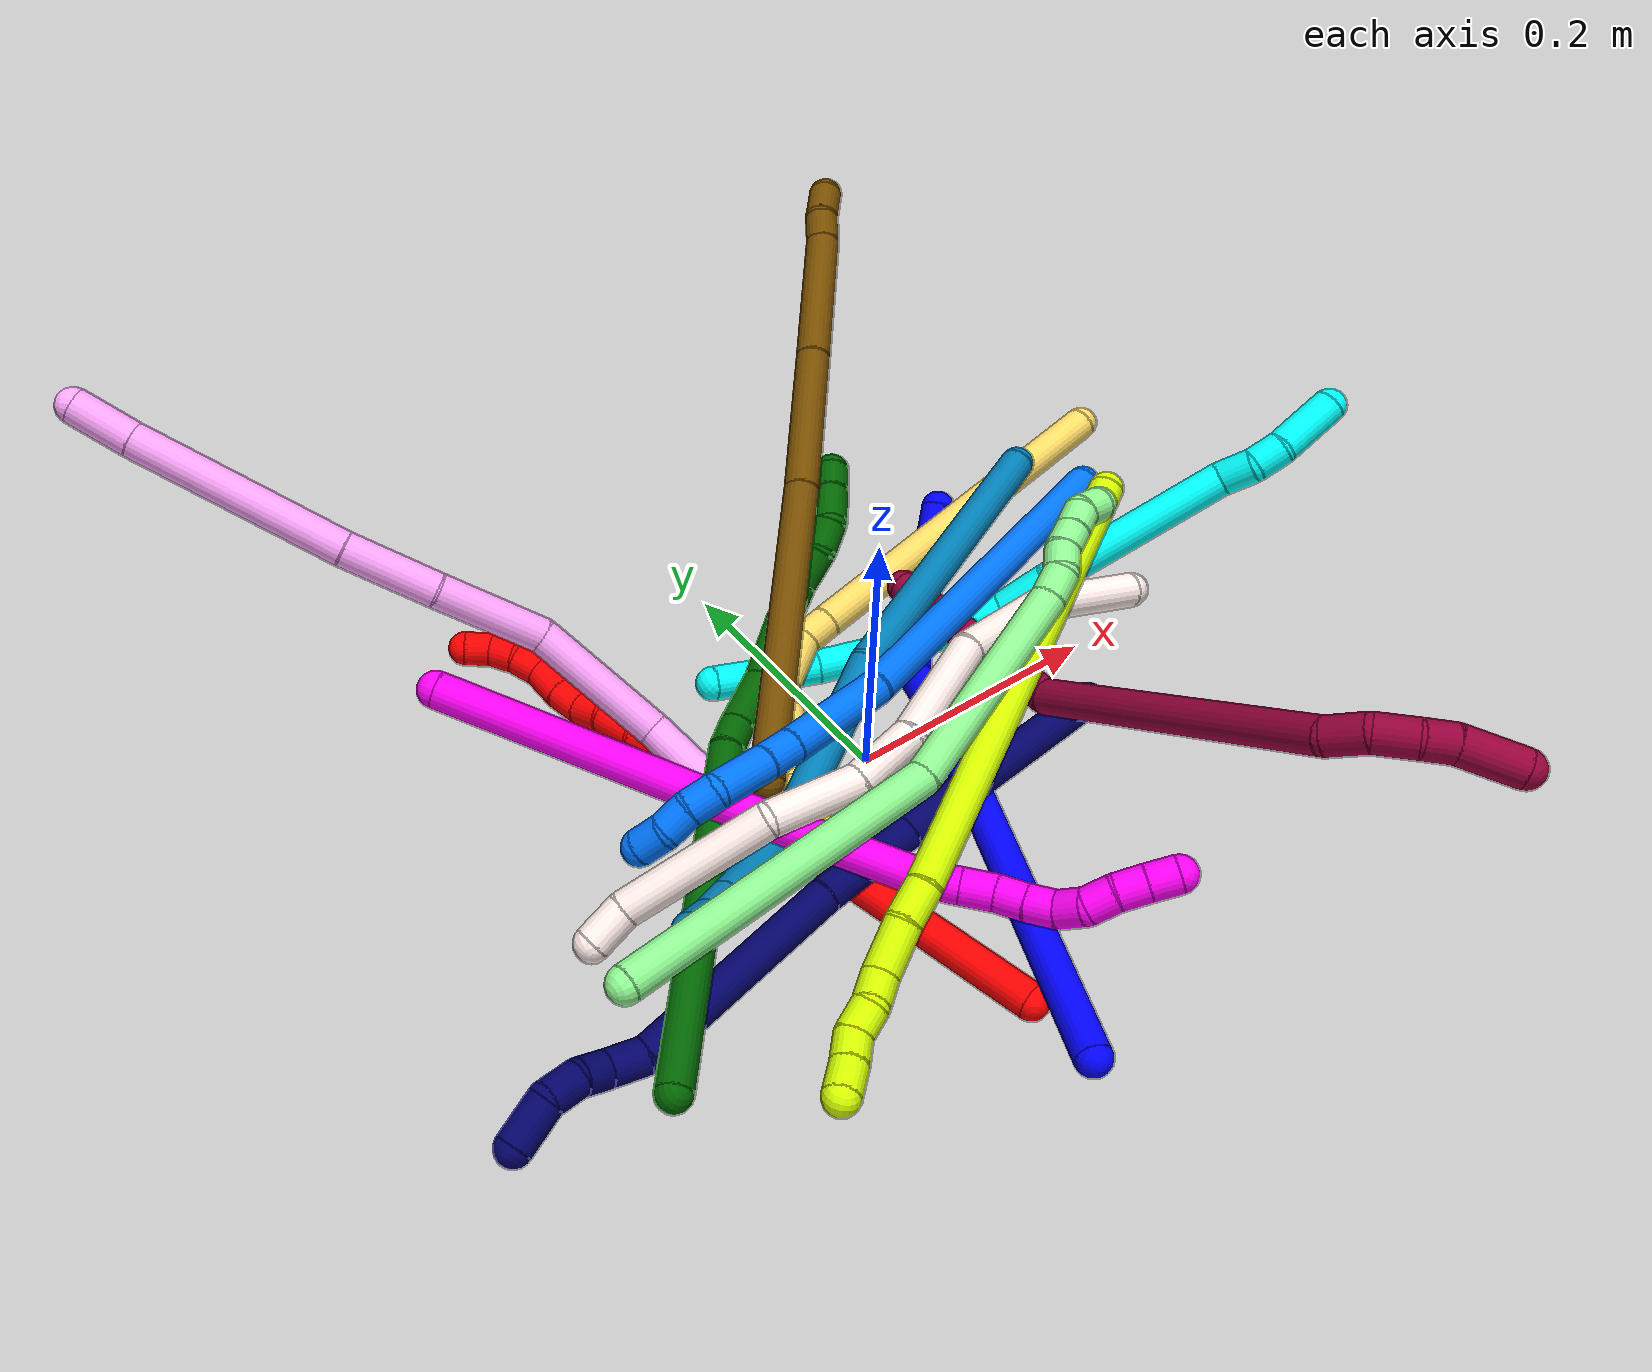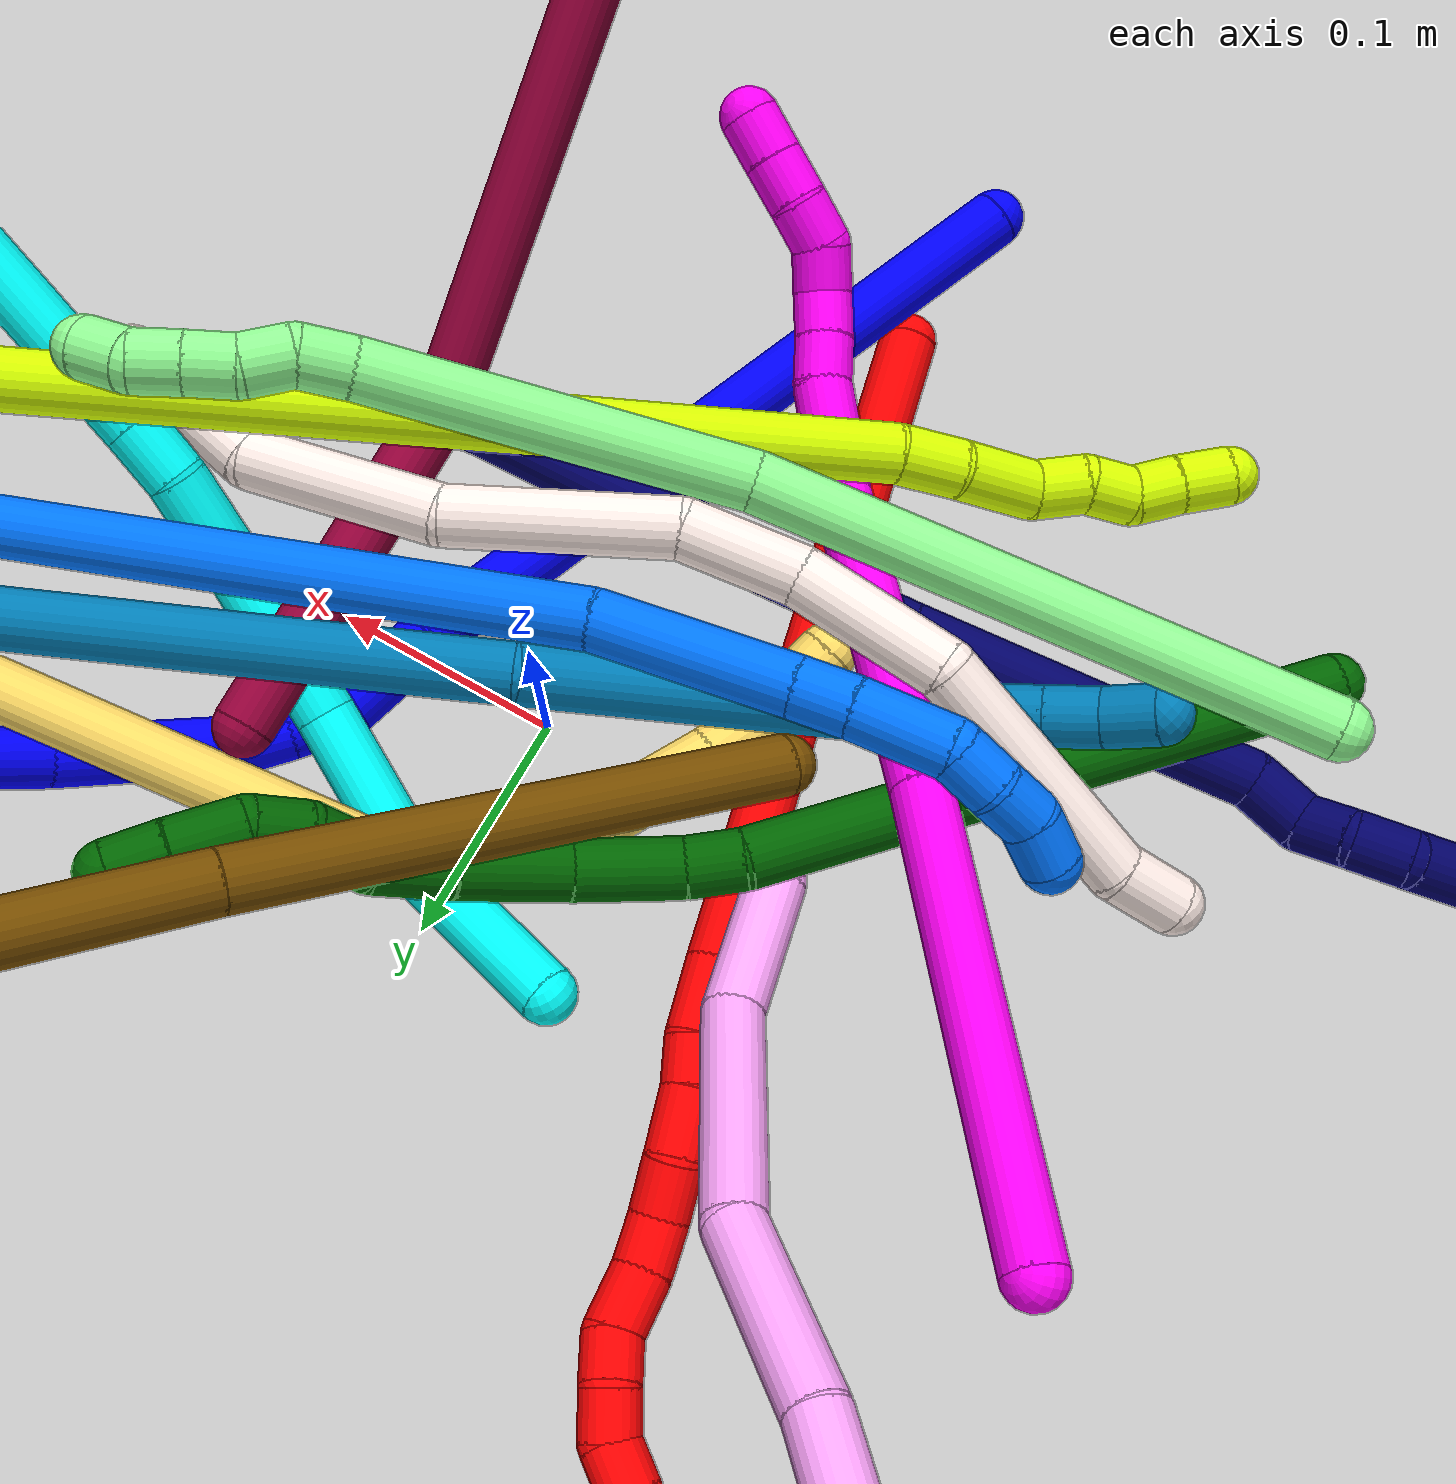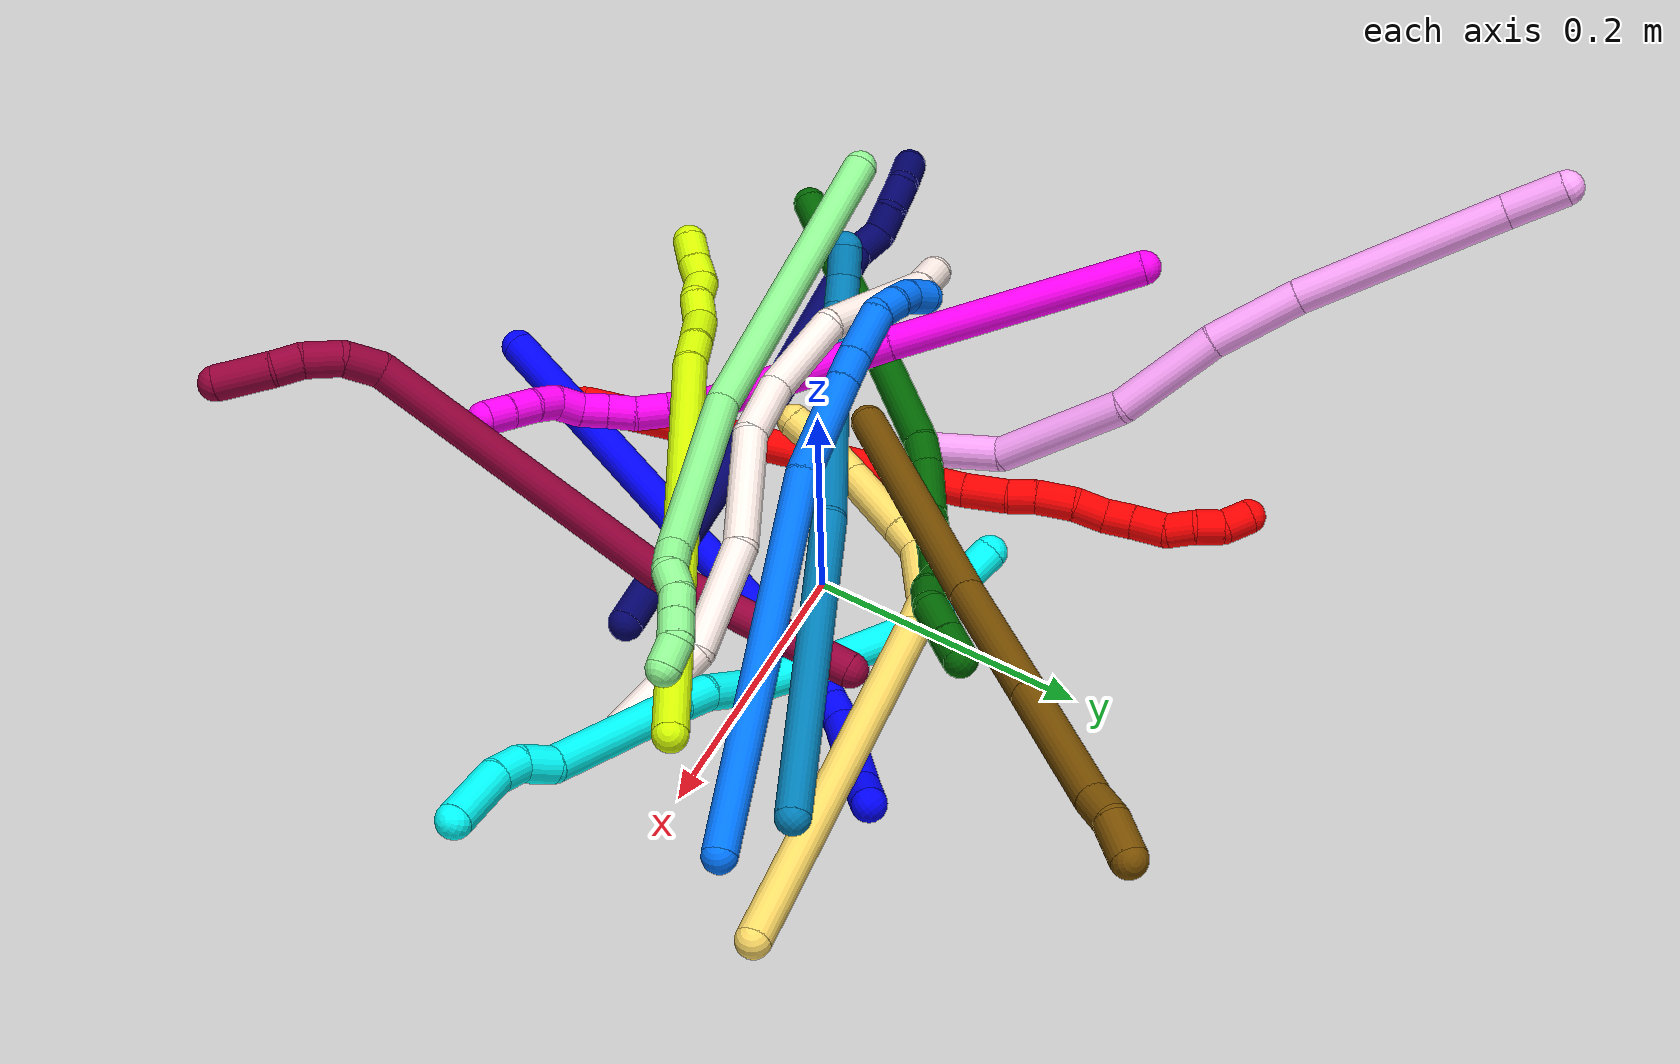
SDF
<sdf version="1.7">
 <world name="default">
  <plugin name="TubeGeneratorPlugin" filename="libtube_generator_plugin.so"/>
  <model name="photoneo_s_sensor">
   <static>1</static>
   <pose>0 0 2 1.57079 1.57079 3.14159</pose>
   <link name="link">
    <inertial><mass>0.1</mass></inertial>
    <sensor name="sensor" type="depth">
     <update_rate>30</update_rate>
     <camera>
      <horizontal_fov>1.22</horizontal_fov>
      <image><width>1920</width><height>1200</height><format>B8G8R8</format></image>
      <clip><near>0.1</near><far>4</far></clip>
      <depth_camera><output>points</output></depth_camera>
     </camera>
     <plugin name="camera_plugin" filename="libgazebo_ros_depth_camera.so">
      <baseline>0.2</baseline>
      <alwaysOn>1</alwaysOn>
      <updateRate>0.0</updateRate>
      <cameraName>camera_ir</cameraName>
      <imageTopicName>/camera/color/image_raw</imageTopicName>
      <cameraInfoTopicName>/camera/color/camera_info</cameraInfoTopicName>
      <depthImageTopicName>/camera/depth/image_raw</depthImageTopicName>
      <depthImageCameraInfoTopicName>/camera/depth/camera_info</depthImageCameraInfoTopicName>
      <pointCloudTopicName>/camera/depth/points</pointCloudTopicName>
      <frameName>fr_optical</frameName>
      <pointCloudCutoff>0.1</pointCloudCutoff>
      <pointCloudCutoffMax>2.0</pointCloudCutoffMax>
      <distortionK1>0</distortionK1>
      <distortionK2>0</distortionK2>
      <distortionK3>0</distortionK3>
      <distortionT1>0</distortionT1>
      <distortionT2>0</distortionT2>
      <CxPrime>0</CxPrime>
      <Cx>0</Cx>
      <Cy>0</Cy>
      <focalLength>0</focalLength>
      <hackBaseline>0</hackBaseline>
     </plugin>
    </sensor>
   </link>
  </model>
  <gravity>0 0 -9.8</gravity>
  <magnetic_field>6e-06 2.3e-05 -4.2e-05</magnetic_field>
  <atmosphere type="adiabatic"/>
  <physics name="default_physics" default="0" type="ode">
   <max_step_size>0.003</max_step_size>
   <real_time_factor>1</real_time_factor>
   <real_time_update_rate>1000</real_time_update_rate>
   <max_contacts>10000</max_contacts>
   <ode>
    <solver>
     <type>quick</type>
     <iters>100</iters>
     <sor>1.3</sor>
     <use_dynamic_moi_rescaling>0</use_dynamic_moi_rescaling>
    </solver>
    <constraints>
     <contact_max_correcting_vel>0</contact_max_correcting_vel>
     <contact_surface_layer>0.001</contact_surface_layer>
     <cfm>0</cfm>
     <erp>0.2</erp>
    </constraints>
   </ode>
  </physics>
  <scene><ambient>0.4 0.4 0.4 1</ambient><background>0.7 0.7 0.7 1</background><shadows>0</shadows></scene>
  <audio><device>default</device></audio>
  <spherical_coordinates>
   <surface_model>EARTH_WGS84</surface_model>
   <latitude_deg>0</latitude_deg>
   <longitude_deg>0</longitude_deg>
   <elevation>0</elevation>
   <heading_deg>0</heading_deg>
  </spherical_coordinates>
  <model name="bin">
   <static>1</static>
   <link name="bottom">
    <collision name="collision-bottom">
     <pose>0 0 -0.01 0 -0 0</pose>
     <geometry><box><size>0.8 0.6 0.02</size></box></geometry>
     <surface>
      <friction><ode><mu>100</mu><mu2>100</mu2></ode></friction>
      <contact><collide_bitmask>65535</collide_bitmask></contact>
     </surface>
    </collision>
   </link>
   <link name="west_wall">
    <collision name="collision-west_wall">
     <pose>-0.41 0 0.1 0 -0 0</pose>
     <geometry><box><size>0.02 0.6 0.2</size></box></geometry>
     <surface>
      <friction><ode><mu>100</mu><mu2>100</mu2></ode></friction>
      <contact><collide_bitmask>65535</collide_bitmask></contact>
     </surface>
    </collision>
   </link>
   <link name="east_wall">
    <collision name="collision-east_wall">
     <pose>0.41 0 0.1 0 -0 0</pose>
     <geometry><box><size>0.02 0.6 0.2</size></box></geometry>
     <surface>
      <friction><ode><mu>100</mu><mu2>100</mu2></ode></friction>
      <contact><collide_bitmask>65535</collide_bitmask></contact>
     </surface>
    </collision>
   </link>
   <link name="south_wall">
    <collision name="collision-south_wall">
     <pose>0 -0.31 0.1 0 -0 0</pose>
     <geometry><box><size>0.8 0.02 0.2</size></box></geometry>
     <surface>
      <friction><ode><mu>100</mu><mu2>100</mu2></ode></friction>
      <contact><collide_bitmask>65535</collide_bitmask></contact>
     </surface>
    </collision>
   </link>
   <link name="north_wall">
    <collision name="collision-north_wall">
     <pose>0 0.31 0.1 0 -0 0</pose>
     <geometry><box><size>0.8 0.02 0.2</size></box></geometry>
     <surface>
      <friction><ode><mu>100</mu><mu2>100</mu2></ode></friction>
      <contact><collide_bitmask>65535</collide_bitmask></contact>
     </surface>
    </collision>
   </link>
  </model>
  <model name="1">
   <static>0</static>
   <link name="1">
    <collision name="collision-cylinder-e_1_1_4">
     <pose>0.022921 0.064145 -0.136653 -2.70272 0.150683 -0.652706</pose>
     <geometry><cylinder><radius>0.0125</radius><length>0.305378</length></cylinder></geometry>
     <surface>
      <friction><ode><mu>1.16</mu><mu2>1.16</mu2><slip1>0</slip1><slip2>0</slip2></ode></friction>
      <contact><ode><kp>1e+06</kp><kd>1</kd><max_vel>0</max_vel><min_depth>0.001</min_depth></ode></contact>
     </surface>
    </collision>
    <visual name="visual-cylinder-e_1_1_4">
     <pose>0.022921 0.064145 -0.136653 -2.70272 0.150683 -0.652706</pose>
     <geometry><cylinder><radius>0.0125</radius><length>0.305378</length></cylinder></geometry>
     <material><ambient>0 0 1 1</ambient></material>
    </visual>
    <collision name="collision-cylinder-e_2_4_5">
     <pose>0.047817 0.135338 -0.296245 -2.8435 0.082147 -0.53429</pose>
     <geometry><cylinder><radius>0.0125</radius><length>0.048158</length></cylinder></geometry>
     <surface>
      <friction><ode><mu>1.16</mu><mu2>1.16</mu2><slip1>0</slip1><slip2>0</slip2></ode></friction>
      <contact><ode><kp>1e+06</kp><kd>1</kd><max_vel>0</max_vel><min_depth>0.001</min_depth></ode></contact>
     </surface>
    </collision>
    <visual name="visual-cylinder-e_2_4_5">
     <pose>0.047817 0.135338 -0.296245 -2.8435 0.082147 -0.53429</pose>
     <geometry><cylinder><radius>0.0125</radius><length>0.048158</length></cylinder></geometry>
     <material><ambient>0 0 1 1</ambient></material>
    </visual>
    <collision name="collision-cylinder-e_3_5_6">
     <pose>0.054937 0.147604 -0.328581 -2.63476 0.446343 -1.43916</pose>
     <geometry><cylinder><radius>0.0125</radius><length>0.023832</length></cylinder></geometry>
     <surface>
      <friction><ode><mu>1.16</mu><mu2>1.16</mu2><slip1>0</slip1><slip2>0</slip2></ode></friction>
      <contact><ode><kp>1e+06</kp><kd>1</kd><max_vel>0</max_vel><min_depth>0.001</min_depth></ode></contact>
     </surface>
    </collision>
    <visual name="visual-cylinder-e_3_5_6">
     <pose>0.054937 0.147604 -0.328581 -2.63476 0.446343 -1.43916</pose>
     <geometry><cylinder><radius>0.0125</radius><length>0.023832</length></cylinder></geometry>
     <material><ambient>0 0 1 1</ambient></material>
    </visual>
    <collision name="collision-cylinder-e_4_6_7">
     <pose>0.064917 0.158667 -0.345682 -2.49249 0.463746 -1.22387</pose>
     <geometry><cylinder><radius>0.0125</radius><length>0.021625</length></cylinder></geometry>
     <surface>
      <friction><ode><mu>1.16</mu><mu2>1.16</mu2><slip1>0</slip1><slip2>0</slip2></ode></friction>
      <contact><ode><kp>1e+06</kp><kd>1</kd><max_vel>0</max_vel><min_depth>0.001</min_depth></ode></contact>
     </surface>
    </collision>
    <visual name="visual-cylinder-e_4_6_7">
     <pose>0.064917 0.158667 -0.345682 -2.49249 0.463746 -1.22387</pose>
     <geometry><cylinder><radius>0.0125</radius><length>0.021625</length></cylinder></geometry>
     <material><ambient>0 0 1 1</ambient></material>
    </visual>
    <collision name="collision-cylinder-e_5_7_8">
     <pose>0.091701 0.188947 -0.372427 -2.23276 0.616407 -1.15509</pose>
     <geometry><cylinder><radius>0.0125</radius><length>0.075927</length></cylinder></geometry>
     <surface>
      <friction><ode><mu>1.16</mu><mu2>1.16</mu2><slip1>0</slip1><slip2>0</slip2></ode></friction>
      <contact><ode><kp>1e+06</kp><kd>1</kd><max_vel>0</max_vel><min_depth>0.001</min_depth></ode></contact>
     </surface>
    </collision>
    <visual name="visual-cylinder-e_5_7_8">
     <pose>0.091701 0.188947 -0.372427 -2.23276 0.616407 -1.15509</pose>
     <geometry><cylinder><radius>0.0125</radius><length>0.075927</length></cylinder></geometry>
     <material><ambient>0 0 1 1</ambient></material>
    </visual>
    <collision name="collision-cylinder-e_6_8_2">
     <pose>0.120514 0.222772 -0.396149 -2.0333 0.579422 -0.897833</pose>
     <geometry><cylinder><radius>0.0125</radius><length>0.02508</length></cylinder></geometry>
     <surface>
      <friction><ode><mu>1.16</mu><mu2>1.16</mu2><slip1>0</slip1><slip2>0</slip2></ode></friction>
      <contact><ode><kp>1e+06</kp><kd>1</kd><max_vel>0</max_vel><min_depth>0.001</min_depth></ode></contact>
     </surface>
    </collision>
    <visual name="visual-cylinder-e_6_8_2">
     <pose>0.120514 0.222772 -0.396149 -2.0333 0.579422 -0.897833</pose>
     <geometry><cylinder><radius>0.0125</radius><length>0.02508</length></cylinder></geometry>
     <material><ambient>0 0 1 1</ambient></material>
    </visual>
    <collision name="collision-sphere-2">
     <pose>0.12738 0.232162 -0.400831 0 -0 0</pose>
     <geometry><sphere><radius>0.0125</radius></sphere></geometry>
     <surface>
      <friction><ode><mu>1.16</mu><mu2>1.16</mu2><slip1>0</slip1><slip2>0</slip2></ode></friction>
      <contact><ode><kp>1e+06</kp><kd>1</kd><max_vel>0</max_vel><min_depth>0.001</min_depth></ode></contact>
     </surface>
    </collision>
    <visual name="visual-sphere-2">
     <pose>0.12738 0.232162 -0.400831 0 -0 0</pose>
     <geometry><sphere><radius>0.0125</radius></sphere></geometry>
     <material><ambient>0 0 1 1</ambient></material>
    </visual>
    <collision name="collision-sphere-4">
     <pose>0.045841 0.12829 -0.273305 0 -0 0</pose>
     <geometry><sphere><radius>0.0125</radius></sphere></geometry>
     <surface>
      <friction><ode><mu>1.16</mu><mu2>1.16</mu2><slip1>0</slip1><slip2>0</slip2></ode></friction>
      <contact><ode><kp>1e+06</kp><kd>1</kd><max_vel>0</max_vel><min_depth>0.001</min_depth></ode></contact>
     </surface>
    </collision>
    <visual name="visual-sphere-4">
     <pose>0.045841 0.12829 -0.273305 0 -0 0</pose>
     <geometry><sphere><radius>0.0125</radius></sphere></geometry>
     <material><ambient>0 0 1 1</ambient></material>
    </visual>
    <collision name="collision-sphere-1">
     <geometry><sphere><radius>0.0125</radius></sphere></geometry>
     <surface>
      <friction><ode><mu>1.16</mu><mu2>1.16</mu2><slip1>0</slip1><slip2>0</slip2></ode></friction>
      <contact><ode><kp>1e+06</kp><kd>1</kd><max_vel>0</max_vel><min_depth>0.001</min_depth></ode></contact>
     </surface>
    </collision>
    <visual name="visual-sphere-1">
     <geometry><sphere><radius>0.0125</radius></sphere></geometry>
     <material><ambient>0 0 1 1</ambient></material>
    </visual>
    <collision name="collision-sphere-8">
     <pose>0.113648 0.213381 -0.391467 0 -0 0</pose>
     <geometry><sphere><radius>0.0125</radius></sphere></geometry>
     <surface>
      <friction><ode><mu>1.16</mu><mu2>1.16</mu2><slip1>0</slip1><slip2>0</slip2></ode></friction>
      <contact><ode><kp>1e+06</kp><kd>1</kd><max_vel>0</max_vel><min_depth>0.001</min_depth></ode></contact>
     </surface>
    </collision>
    <visual name="visual-sphere-8">
     <pose>0.113648 0.213381 -0.391467 0 -0 0</pose>
     <geometry><sphere><radius>0.0125</radius></sphere></geometry>
     <material><ambient>0 0 1 1</ambient></material>
    </visual>
    <collision name="collision-sphere-5">
     <pose>0.049793 0.142386 -0.319184 0 -0 0</pose>
     <geometry><sphere><radius>0.0125</radius></sphere></geometry>
     <surface>
      <friction><ode><mu>1.16</mu><mu2>1.16</mu2><slip1>0</slip1><slip2>0</slip2></ode></friction>
      <contact><ode><kp>1e+06</kp><kd>1</kd><max_vel>0</max_vel><min_depth>0.001</min_depth></ode></contact>
     </surface>
    </collision>
    <visual name="visual-sphere-5">
     <pose>0.049793 0.142386 -0.319184 0 -0 0</pose>
     <geometry><sphere><radius>0.0125</radius></sphere></geometry>
     <material><ambient>0 0 1 1</ambient></material>
    </visual>
    <collision name="collision-sphere-6">
     <pose>0.060081 0.152821 -0.337978 0 -0 0</pose>
     <geometry><sphere><radius>0.0125</radius></sphere></geometry>
     <surface>
      <friction><ode><mu>1.16</mu><mu2>1.16</mu2><slip1>0</slip1><slip2>0</slip2></ode></friction>
      <contact><ode><kp>1e+06</kp><kd>1</kd><max_vel>0</max_vel><min_depth>0.001</min_depth></ode></contact>
     </surface>
    </collision>
    <visual name="visual-sphere-6">
     <pose>0.060081 0.152821 -0.337978 0 -0 0</pose>
     <geometry><sphere><radius>0.0125</radius></sphere></geometry>
     <material><ambient>0 0 1 1</ambient></material>
    </visual>
    <collision name="collision-sphere-7">
     <pose>0.069754 0.164512 -0.353386 0 -0 0</pose>
     <geometry><sphere><radius>0.0125</radius></sphere></geometry>
     <surface>
      <friction><ode><mu>1.16</mu><mu2>1.16</mu2><slip1>0</slip1><slip2>0</slip2></ode></friction>
      <contact><ode><kp>1e+06</kp><kd>1</kd><max_vel>0</max_vel><min_depth>0.001</min_depth></ode></contact>
     </surface>
    </collision>
    <visual name="visual-sphere-7">
     <pose>0.069754 0.164512 -0.353386 0 -0 0</pose>
     <geometry><sphere><radius>0.0125</radius></sphere></geometry>
     <material><ambient>0 0 1 1</ambient></material>
    </visual>
    <inertial>
     <pose>0.044001 0.105977 -0.219032 0 -0 0</pose>
     <mass>0.5</mass>
     <inertia>
      <ixx>0.000436</ixx>
      <ixy>0</ixy>
      <ixz>0</ixz>
      <iyy>-0.003079</iyy>
      <iyz>0</iyz>
      <izz>-0.00145</izz>
     </inertia>
    </inertial>
   </link>
   <pose>-0.056662 -0.288505 0.031973 1.07527 -0.117271 -0.23255</pose>
  </model>
  <model name="2">
   <static>0</static>
   <link name="2">
    <collision name="collision-cylinder-e_1_1_4">
     <pose>-0.02722 0.100876 0.099294 -0.793299 -0.189989 0.079775</pose>
     <geometry><cylinder><radius>0.0125</radius><length>0.288279</length></cylinder></geometry>
     <surface>
      <friction><ode><mu>1.16</mu><mu2>1.16</mu2><slip1>0</slip1><slip2>0</slip2></ode></friction>
      <contact><ode><kp>1e+06</kp><kd>1</kd><max_vel>0</max_vel><min_depth>0.001</min_depth></ode></contact>
     </surface>
    </collision>
    <visual name="visual-cylinder-e_1_1_4">
     <pose>-0.02722 0.100876 0.099294 -0.793299 -0.189989 0.079775</pose>
     <geometry><cylinder><radius>0.0125</radius><length>0.288279</length></cylinder></geometry>
     <material><ambient>1 0 0 1</ambient></material>
    </visual>
    <collision name="collision-cylinder-e_2_4_5">
     <pose>-0.059069 0.212984 0.209192 -0.814165 -0.291095 0.126237</pose>
     <geometry><cylinder><radius>0.0125</radius><length>0.032251</length></cylinder></geometry>
     <surface>
      <friction><ode><mu>1.16</mu><mu2>1.16</mu2><slip1>0</slip1><slip2>0</slip2></ode></friction>
      <contact><ode><kp>1e+06</kp><kd>1</kd><max_vel>0</max_vel><min_depth>0.001</min_depth></ode></contact>
     </surface>
    </collision>
    <visual name="visual-cylinder-e_2_4_5">
     <pose>-0.059069 0.212984 0.209192 -0.814165 -0.291095 0.126237</pose>
     <geometry><cylinder><radius>0.0125</radius><length>0.032251</length></cylinder></geometry>
     <material><ambient>1 0 0 1</ambient></material>
    </visual>
    <collision name="collision-cylinder-e_3_5_6">
     <pose>-0.066253 0.232582 0.225003 -1.01411 -0.253811 0.141517</pose>
     <geometry><cylinder><radius>0.0125</radius><length>0.02036</length></cylinder></geometry>
     <surface>
      <friction><ode><mu>1.16</mu><mu2>1.16</mu2><slip1>0</slip1><slip2>0</slip2></ode></friction>
      <contact><ode><kp>1e+06</kp><kd>1</kd><max_vel>0</max_vel><min_depth>0.001</min_depth></ode></contact>
     </surface>
    </collision>
    <visual name="visual-cylinder-e_3_5_6">
     <pose>-0.066253 0.232582 0.225003 -1.01411 -0.253811 0.141517</pose>
     <geometry><cylinder><radius>0.0125</radius><length>0.02036</length></cylinder></geometry>
     <material><ambient>1 0 0 1</ambient></material>
    </visual>
    <collision name="collision-cylinder-e_4_6_7">
     <pose>-0.071166 0.251312 0.239209 -0.855735 -0.170006 0.077678</pose>
     <geometry><cylinder><radius>0.0125</radius><length>0.027856</length></cylinder></geometry>
     <surface>
      <friction><ode><mu>1.16</mu><mu2>1.16</mu2><slip1>0</slip1><slip2>0</slip2></ode></friction>
      <contact><ode><kp>1e+06</kp><kd>1</kd><max_vel>0</max_vel><min_depth>0.001</min_depth></ode></contact>
     </surface>
    </collision>
    <visual name="visual-cylinder-e_4_6_7">
     <pose>-0.071166 0.251312 0.239209 -0.855735 -0.170006 0.077678</pose>
     <geometry><cylinder><radius>0.0125</radius><length>0.027856</length></cylinder></geometry>
     <material><ambient>1 0 0 1</ambient></material>
    </visual>
    <collision name="collision-cylinder-e_5_7_8">
     <pose>-0.072387 0.270421 0.255831 -0.853923 0.097518 -0.044393</pose>
     <geometry><cylinder><radius>0.0125</radius><length>0.02331</length></cylinder></geometry>
     <surface>
      <friction><ode><mu>1.16</mu><mu2>1.16</mu2><slip1>0</slip1><slip2>0</slip2></ode></friction>
      <contact><ode><kp>1e+06</kp><kd>1</kd><max_vel>0</max_vel><min_depth>0.001</min_depth></ode></contact>
     </surface>
    </collision>
    <visual name="visual-cylinder-e_5_7_8">
     <pose>-0.072387 0.270421 0.255831 -0.853923 0.097518 -0.044393</pose>
     <geometry><cylinder><radius>0.0125</radius><length>0.02331</length></cylinder></geometry>
     <material><ambient>1 0 0 1</ambient></material>
    </visual>
    <collision name="collision-cylinder-e_6_8_9">
     <pose>-0.073628 0.286652 0.271046 -0.778291 -0.219216 0.090191</pose>
     <geometry><cylinder><radius>0.0125</radius><length>0.02185</length></cylinder></geometry>
     <surface>
      <friction><ode><mu>1.16</mu><mu2>1.16</mu2><slip1>0</slip1><slip2>0</slip2></ode></friction>
      <contact><ode><kp>1e+06</kp><kd>1</kd><max_vel>0</max_vel><min_depth>0.001</min_depth></ode></contact>
     </surface>
    </collision>
    <visual name="visual-cylinder-e_6_8_9">
     <pose>-0.073628 0.286652 0.271046 -0.778291 -0.219216 0.090191</pose>
     <geometry><cylinder><radius>0.0125</radius><length>0.02185</length></cylinder></geometry>
     <material><ambient>1 0 0 1</ambient></material>
    </visual>
    <collision name="collision-cylinder-e_7_9_10">
     <pose>-0.080067 0.301327 0.288458 -0.631909 -0.322285 0.106178</pose>
     <geometry><cylinder><radius>0.0125</radius><length>0.025658</length></cylinder></geometry>
     <surface>
      <friction><ode><mu>1.16</mu><mu2>1.16</mu2><slip1>0</slip1><slip2>0</slip2></ode></friction>
      <contact><ode><kp>1e+06</kp><kd>1</kd><max_vel>0</max_vel><min_depth>0.001</min_depth></ode></contact>
     </surface>
    </collision>
    <visual name="visual-cylinder-e_7_9_10">
     <pose>-0.080067 0.301327 0.288458 -0.631909 -0.322285 0.106178</pose>
     <geometry><cylinder><radius>0.0125</radius><length>0.025658</length></cylinder></geometry>
     <material><ambient>1 0 0 1</ambient></material>
    </visual>
    <collision name="collision-cylinder-e_8_10_11">
     <pose>-0.088539 0.316355 0.302724 -1.05482 -0.454905 0.268007</pose>
     <geometry><cylinder><radius>0.0125</radius><length>0.020068</length></cylinder></geometry>
     <surface>
      <friction><ode><mu>1.16</mu><mu2>1.16</mu2><slip1>0</slip1><slip2>0</slip2></ode></friction>
      <contact><ode><kp>1e+06</kp><kd>1</kd><max_vel>0</max_vel><min_depth>0.001</min_depth></ode></contact>
     </surface>
    </collision>
    <visual name="visual-cylinder-e_8_10_11">
     <pose>-0.088539 0.316355 0.302724 -1.05482 -0.454905 0.268007</pose>
     <geometry><cylinder><radius>0.0125</radius><length>0.020068</length></cylinder></geometry>
     <material><ambient>1 0 0 1</ambient></material>
    </visual>
    <collision name="collision-cylinder-e_9_11_12">
     <pose>-0.094679 0.333054 0.311687 -1.09944 -0.172327 0.105751</pose>
     <geometry><cylinder><radius>0.0125</radius><length>0.020186</length></cylinder></geometry>
     <surface>
      <friction><ode><mu>1.16</mu><mu2>1.16</mu2><slip1>0</slip1><slip2>0</slip2></ode></friction>
      <contact><ode><kp>1e+06</kp><kd>1</kd><max_vel>0</max_vel><min_depth>0.001</min_depth></ode></contact>
     </surface>
    </collision>
    <visual name="visual-cylinder-e_9_11_12">
     <pose>-0.094679 0.333054 0.311687 -1.09944 -0.172327 0.105751</pose>
     <geometry><cylinder><radius>0.0125</radius><length>0.020186</length></cylinder></geometry>
     <material><ambient>1 0 0 1</ambient></material>
    </visual>
    <collision name="collision-cylinder-e_10_12_2">
     <pose>-0.098979 0.351661 0.316674 -1.52245 -0.257447 0.245417</pose>
     <geometry><cylinder><radius>0.0125</radius><length>0.020183</length></cylinder></geometry>
     <surface>
      <friction><ode><mu>1.16</mu><mu2>1.16</mu2><slip1>0</slip1><slip2>0</slip2></ode></friction>
      <contact><ode><kp>1e+06</kp><kd>1</kd><max_vel>0</max_vel><min_depth>0.001</min_depth></ode></contact>
     </surface>
    </collision>
    <visual name="visual-cylinder-e_10_12_2">
     <pose>-0.098979 0.351661 0.316674 -1.52245 -0.257447 0.245417</pose>
     <geometry><cylinder><radius>0.0125</radius><length>0.020183</length></cylinder></geometry>
     <material><ambient>1 0 0 1</ambient></material>
    </visual>
    <collision name="collision-sphere-2">
     <pose>-0.101548 0.361408 0.317145 0 -0 0</pose>
     <geometry><sphere><radius>0.0125</radius></sphere></geometry>
     <surface>
      <friction><ode><mu>1.16</mu><mu2>1.16</mu2><slip1>0</slip1><slip2>0</slip2></ode></friction>
      <contact><ode><kp>1e+06</kp><kd>1</kd><max_vel>0</max_vel><min_depth>0.001</min_depth></ode></contact>
     </surface>
    </collision>
    <visual name="visual-sphere-2">
     <pose>-0.101548 0.361408 0.317145 0 -0 0</pose>
     <geometry><sphere><radius>0.0125</radius></sphere></geometry>
     <material><ambient>1 0 0 1</ambient></material>
    </visual>
    <collision name="collision-sphere-12">
     <pose>-0.09641 0.341913 0.316202 0 -0 0</pose>
     <geometry><sphere><radius>0.0125</radius></sphere></geometry>
     <surface>
      <friction><ode><mu>1.16</mu><mu2>1.16</mu2><slip1>0</slip1><slip2>0</slip2></ode></friction>
      <contact><ode><kp>1e+06</kp><kd>1</kd><max_vel>0</max_vel><min_depth>0.001</min_depth></ode></contact>
     </surface>
    </collision>
    <visual name="visual-sphere-12">
     <pose>-0.09641 0.341913 0.316202 0 -0 0</pose>
     <geometry><sphere><radius>0.0125</radius></sphere></geometry>
     <material><ambient>1 0 0 1</ambient></material>
    </visual>
    <collision name="collision-sphere-11">
     <pose>-0.092948 0.324194 0.307171 0 -0 0</pose>
     <geometry><sphere><radius>0.0125</radius></sphere></geometry>
     <surface>
      <friction><ode><mu>1.16</mu><mu2>1.16</mu2><slip1>0</slip1><slip2>0</slip2></ode></friction>
      <contact><ode><kp>1e+06</kp><kd>1</kd><max_vel>0</max_vel><min_depth>0.001</min_depth></ode></contact>
     </surface>
    </collision>
    <visual name="visual-sphere-11">
     <pose>-0.092948 0.324194 0.307171 0 -0 0</pose>
     <geometry><sphere><radius>0.0125</radius></sphere></geometry>
     <material><ambient>1 0 0 1</ambient></material>
    </visual>
    <collision name="collision-sphere-10">
     <pose>-0.084131 0.308515 0.298277 0 -0 0</pose>
     <geometry><sphere><radius>0.0125</radius></sphere></geometry>
     <surface>
      <friction><ode><mu>1.16</mu><mu2>1.16</mu2><slip1>0</slip1><slip2>0</slip2></ode></friction>
      <contact><ode><kp>1e+06</kp><kd>1</kd><max_vel>0</max_vel><min_depth>0.001</min_depth></ode></contact>
     </surface>
    </collision>
    <visual name="visual-sphere-10">
     <pose>-0.084131 0.308515 0.298277 0 -0 0</pose>
     <geometry><sphere><radius>0.0125</radius></sphere></geometry>
     <material><ambient>1 0 0 1</ambient></material>
    </visual>
    <collision name="collision-sphere-9">
     <pose>-0.076004 0.294139 0.27864 0 -0 0</pose>
     <geometry><sphere><radius>0.0125</radius></sphere></geometry>
     <surface>
      <friction><ode><mu>1.16</mu><mu2>1.16</mu2><slip1>0</slip1><slip2>0</slip2></ode></friction>
      <contact><ode><kp>1e+06</kp><kd>1</kd><max_vel>0</max_vel><min_depth>0.001</min_depth></ode></contact>
     </surface>
    </collision>
    <visual name="visual-sphere-9">
     <pose>-0.076004 0.294139 0.27864 0 -0 0</pose>
     <geometry><sphere><radius>0.0125</radius></sphere></geometry>
     <material><ambient>1 0 0 1</ambient></material>
    </visual>
    <collision name="collision-sphere-4">
     <pose>-0.054441 0.201751 0.198588 0 -0 0</pose>
     <geometry><sphere><radius>0.0125</radius></sphere></geometry>
     <surface>
      <friction><ode><mu>1.16</mu><mu2>1.16</mu2><slip1>0</slip1><slip2>0</slip2></ode></friction>
      <contact><ode><kp>1e+06</kp><kd>1</kd><max_vel>0</max_vel><min_depth>0.001</min_depth></ode></contact>
     </surface>
    </collision>
    <visual name="visual-sphere-4">
     <pose>-0.054441 0.201751 0.198588 0 -0 0</pose>
     <geometry><sphere><radius>0.0125</radius></sphere></geometry>
     <material><ambient>1 0 0 1</ambient></material>
    </visual>
    <collision name="collision-sphere-1">
     <geometry><sphere><radius>0.0125</radius></sphere></geometry>
     <surface>
      <friction><ode><mu>1.16</mu><mu2>1.16</mu2><slip1>0</slip1><slip2>0</slip2></ode></friction>
      <contact><ode><kp>1e+06</kp><kd>1</kd><max_vel>0</max_vel><min_depth>0.001</min_depth></ode></contact>
     </surface>
    </collision>
    <visual name="visual-sphere-1">
     <geometry><sphere><radius>0.0125</radius></sphere></geometry>
     <material><ambient>1 0 0 1</ambient></material>
    </visual>
    <collision name="collision-sphere-8">
     <pose>-0.071252 0.279166 0.263452 0 -0 0</pose>
     <geometry><sphere><radius>0.0125</radius></sphere></geometry>
     <surface>
      <friction><ode><mu>1.16</mu><mu2>1.16</mu2><slip1>0</slip1><slip2>0</slip2></ode></friction>
      <contact><ode><kp>1e+06</kp><kd>1</kd><max_vel>0</max_vel><min_depth>0.001</min_depth></ode></contact>
     </surface>
    </collision>
    <visual name="visual-sphere-8">
     <pose>-0.071252 0.279166 0.263452 0 -0 0</pose>
     <geometry><sphere><radius>0.0125</radius></sphere></geometry>
     <material><ambient>1 0 0 1</ambient></material>
    </visual>
    <collision name="collision-sphere-5">
     <pose>-0.063697 0.224216 0.219796 0 -0 0</pose>
     <geometry><sphere><radius>0.0125</radius></sphere></geometry>
     <surface>
      <friction><ode><mu>1.16</mu><mu2>1.16</mu2><slip1>0</slip1><slip2>0</slip2></ode></friction>
      <contact><ode><kp>1e+06</kp><kd>1</kd><max_vel>0</max_vel><min_depth>0.001</min_depth></ode></contact>
     </surface>
    </collision>
    <visual name="visual-sphere-5">
     <pose>-0.063697 0.224216 0.219796 0 -0 0</pose>
     <geometry><sphere><radius>0.0125</radius></sphere></geometry>
     <material><ambient>1 0 0 1</ambient></material>
    </visual>
    <collision name="collision-sphere-6">
     <pose>-0.068809 0.240948 0.230209 0 -0 0</pose>
     <geometry><sphere><radius>0.0125</radius></sphere></geometry>
     <surface>
      <friction><ode><mu>1.16</mu><mu2>1.16</mu2><slip1>0</slip1><slip2>0</slip2></ode></friction>
      <contact><ode><kp>1e+06</kp><kd>1</kd><max_vel>0</max_vel><min_depth>0.001</min_depth></ode></contact>
     </surface>
    </collision>
    <visual name="visual-sphere-6">
     <pose>-0.068809 0.240948 0.230209 0 -0 0</pose>
     <geometry><sphere><radius>0.0125</radius></sphere></geometry>
     <material><ambient>1 0 0 1</ambient></material>
    </visual>
    <collision name="collision-sphere-7">
     <pose>-0.073522 0.261677 0.24821 0 -0 0</pose>
     <geometry><sphere><radius>0.0125</radius></sphere></geometry>
     <surface>
      <friction><ode><mu>1.16</mu><mu2>1.16</mu2><slip1>0</slip1><slip2>0</slip2></ode></friction>
      <contact><ode><kp>1e+06</kp><kd>1</kd><max_vel>0</max_vel><min_depth>0.001</min_depth></ode></contact>
     </surface>
    </collision>
    <visual name="visual-sphere-7">
     <pose>-0.073522 0.261677 0.24821 0 -0 0</pose>
     <geometry><sphere><radius>0.0125</radius></sphere></geometry>
     <material><ambient>1 0 0 1</ambient></material>
    </visual>
    <inertial>
     <pose>-0.048239 0.176305 0.169321 0 -0 0</pose>
     <mass>0.5</mass>
     <inertia>
      <ixx>0.002135</ixx>
      <ixy>0</ixy>
      <ixz>0</ixz>
      <iyy>0.001625</iyy>
      <iyz>0</iyz>
      <izz>-0.001011</izz>
     </inertia>
    </inertial>
   </link>
   <pose>-0.048465 -0.227289 0.011493 -1.82183 1.36175 -0.831418</pose>
  </model>
  <model name="3">
   <static>0</static>
   <link name="3">
    <collision name="collision-cylinder-e_1_1_4">
     <pose>0.031572 -0.008152 0.024645 0.319455 0.882654 0.151915</pose>
     <geometry><cylinder><radius>0.0125</radius><length>0.081747</length></cylinder></geometry>
     <surface>
      <friction><ode><mu>1.16</mu><mu2>1.16</mu2><slip1>0</slip1><slip2>0</slip2></ode></friction>
      <contact><ode><kp>1e+06</kp><kd>1</kd><max_vel>0</max_vel><min_depth>0.001</min_depth></ode></contact>
     </surface>
    </collision>
    <visual name="visual-cylinder-e_1_1_4">
     <pose>0.031572 -0.008152 0.024645 0.319455 0.882654 0.151915</pose>
     <geometry><cylinder><radius>0.0125</radius><length>0.081747</length></cylinder></geometry>
     <material><ambient>0.003922 1 0.996078 1</ambient></material>
    </visual>
    <collision name="collision-cylinder-e_2_4_5">
     <pose>0.077993 -0.026157 0.077841 0.332303 0.456971 0.077955</pose>
     <geometry><cylinder><radius>0.0125</radius><length>0.067313</length></cylinder></geometry>
     <surface>
      <friction><ode><mu>1.16</mu><mu2>1.16</mu2><slip1>0</slip1><slip2>0</slip2></ode></friction>
      <contact><ode><kp>1e+06</kp><kd>1</kd><max_vel>0</max_vel><min_depth>0.001</min_depth></ode></contact>
     </surface>
    </collision>
    <visual name="visual-cylinder-e_2_4_5">
     <pose>0.077993 -0.026157 0.077841 0.332303 0.456971 0.077955</pose>
     <geometry><cylinder><radius>0.0125</radius><length>0.067313</length></cylinder></geometry>
     <material><ambient>0.003922 1 0.996078 1</ambient></material>
    </visual>
    <collision name="collision-cylinder-e_3_5_6">
     <pose>0.104804 -0.04343 0.140464 0.21441 0.330417 0.035882</pose>
     <geometry><cylinder><radius>0.0125</radius><length>0.073729</length></cylinder></geometry>
     <surface>
      <friction><ode><mu>1.16</mu><mu2>1.16</mu2><slip1>0</slip1><slip2>0</slip2></ode></friction>
      <contact><ode><kp>1e+06</kp><kd>1</kd><max_vel>0</max_vel><min_depth>0.001</min_depth></ode></contact>
     </surface>
    </collision>
    <visual name="visual-cylinder-e_3_5_6">
     <pose>0.104804 -0.04343 0.140464 0.21441 0.330417 0.035882</pose>
     <geometry><cylinder><radius>0.0125</radius><length>0.073729</length></cylinder></geometry>
     <material><ambient>0.003922 1 0.996078 1</ambient></material>
    </visual>
    <collision name="collision-cylinder-e_4_6_7">
     <pose>0.118986 -0.051714 0.19339 0.045854 0.117169 0.00269</pose>
     <geometry><cylinder><radius>0.0125</radius><length>0.03801</length></cylinder></geometry>
     <surface>
      <friction><ode><mu>1.16</mu><mu2>1.16</mu2><slip1>0</slip1><slip2>0</slip2></ode></friction>
      <contact><ode><kp>1e+06</kp><kd>1</kd><max_vel>0</max_vel><min_depth>0.001</min_depth></ode></contact>
     </surface>
    </collision>
    <visual name="visual-cylinder-e_4_6_7">
     <pose>0.118986 -0.051714 0.19339 0.045854 0.117169 0.00269</pose>
     <geometry><cylinder><radius>0.0125</radius><length>0.03801</length></cylinder></geometry>
     <material><ambient>0.003922 1 0.996078 1</ambient></material>
    </visual>
    <collision name="collision-cylinder-e_5_7_8">
     <pose>0.125436 -0.053005 0.224115 0.035846 0.34202 0.006191</pose>
     <geometry><cylinder><radius>0.0125</radius><length>0.025216</length></cylinder></geometry>
     <surface>
      <friction><ode><mu>1.16</mu><mu2>1.16</mu2><slip1>0</slip1><slip2>0</slip2></ode></friction>
      <contact><ode><kp>1e+06</kp><kd>1</kd><max_vel>0</max_vel><min_depth>0.001</min_depth></ode></contact>
     </surface>
    </collision>
    <visual name="visual-cylinder-e_5_7_8">
     <pose>0.125436 -0.053005 0.224115 0.035846 0.34202 0.006191</pose>
     <geometry><cylinder><radius>0.0125</radius><length>0.025216</length></cylinder></geometry>
     <material><ambient>0.003922 1 0.996078 1</ambient></material>
    </visual>
    <collision name="collision-cylinder-e_6_8_9">
     <pose>0.150831 -0.054583 0.290786 0.021025 0.368515 0.003919</pose>
     <geometry><cylinder><radius>0.0125</radius><length>0.117515</length></cylinder></geometry>
     <surface>
      <friction><ode><mu>1.16</mu><mu2>1.16</mu2><slip1>0</slip1><slip2>0</slip2></ode></friction>
      <contact><ode><kp>1e+06</kp><kd>1</kd><max_vel>0</max_vel><min_depth>0.001</min_depth></ode></contact>
     </surface>
    </collision>
    <visual name="visual-cylinder-e_6_8_9">
     <pose>0.150831 -0.054583 0.290786 0.021025 0.368515 0.003919</pose>
     <geometry><cylinder><radius>0.0125</radius><length>0.117515</length></cylinder></geometry>
     <material><ambient>0.003922 1 0.996078 1</ambient></material>
    </visual>
    <collision name="collision-cylinder-e_7_9_10">
     <pose>0.172494 -0.059099 0.357721 0.270379 0.039473 0.00537</pose>
     <geometry><cylinder><radius>0.0125</radius><length>0.025204</length></cylinder></geometry>
     <surface>
      <friction><ode><mu>1.16</mu><mu2>1.16</mu2><slip1>0</slip1><slip2>0</slip2></ode></friction>
      <contact><ode><kp>1e+06</kp><kd>1</kd><max_vel>0</max_vel><min_depth>0.001</min_depth></ode></contact>
     </surface>
    </collision>
    <visual name="visual-cylinder-e_7_9_10">
     <pose>0.172494 -0.059099 0.357721 0.270379 0.039473 0.00537</pose>
     <geometry><cylinder><radius>0.0125</radius><length>0.025204</length></cylinder></geometry>
     <material><ambient>0.003922 1 0.996078 1</ambient></material>
    </visual>
    <collision name="collision-cylinder-e_8_10_11">
     <pose>0.177081 -0.062178 0.380353 -0.027027 0.371299 -0.005076</pose>
     <geometry><cylinder><radius>0.0125</radius><length>0.022539</length></cylinder></geometry>
     <surface>
      <friction><ode><mu>1.16</mu><mu2>1.16</mu2><slip1>0</slip1><slip2>0</slip2></ode></friction>
      <contact><ode><kp>1e+06</kp><kd>1</kd><max_vel>0</max_vel><min_depth>0.001</min_depth></ode></contact>
     </surface>
    </collision>
    <visual name="visual-cylinder-e_8_10_11">
     <pose>0.177081 -0.062178 0.380353 -0.027027 0.371299 -0.005076</pose>
     <geometry><cylinder><radius>0.0125</radius><length>0.022539</length></cylinder></geometry>
     <material><ambient>0.003922 1 0.996078 1</ambient></material>
    </visual>
    <collision name="collision-cylinder-e_9_11_2">
     <pose>0.193591 -0.056417 0.411083 -0.264384 0.534991 -0.072851</pose>
     <geometry><cylinder><radius>0.0125</radius><length>0.048729</length></cylinder></geometry>
     <surface>
      <friction><ode><mu>1.16</mu><mu2>1.16</mu2><slip1>0</slip1><slip2>0</slip2></ode></friction>
      <contact><ode><kp>1e+06</kp><kd>1</kd><max_vel>0</max_vel><min_depth>0.001</min_depth></ode></contact>
     </surface>
    </collision>
    <visual name="visual-cylinder-e_9_11_2">
     <pose>0.193591 -0.056417 0.411083 -0.264384 0.534991 -0.072851</pose>
     <geometry><cylinder><radius>0.0125</radius><length>0.048729</length></cylinder></geometry>
     <material><ambient>0.003922 1 0.996078 1</ambient></material>
    </visual>
    <collision name="collision-sphere-2">
     <pose>0.206013 -0.05094 0.431315 0 -0 0</pose>
     <geometry><sphere><radius>0.0125</radius></sphere></geometry>
     <surface>
      <friction><ode><mu>1.16</mu><mu2>1.16</mu2><slip1>0</slip1><slip2>0</slip2></ode></friction>
      <contact><ode><kp>1e+06</kp><kd>1</kd><max_vel>0</max_vel><min_depth>0.001</min_depth></ode></contact>
     </surface>
    </collision>
    <visual name="visual-sphere-2">
     <pose>0.206013 -0.05094 0.431315 0 -0 0</pose>
     <geometry><sphere><radius>0.0125</radius></sphere></geometry>
     <material><ambient>0.003922 1 0.996078 1</ambient></material>
    </visual>
    <collision name="collision-sphere-11">
     <pose>0.181169 -0.061894 0.390851 0 -0 0</pose>
     <geometry><sphere><radius>0.0125</radius></sphere></geometry>
     <surface>
      <friction><ode><mu>1.16</mu><mu2>1.16</mu2><slip1>0</slip1><slip2>0</slip2></ode></friction>
      <contact><ode><kp>1e+06</kp><kd>1</kd><max_vel>0</max_vel><min_depth>0.001</min_depth></ode></contact>
     </surface>
    </collision>
    <visual name="visual-sphere-11">
     <pose>0.181169 -0.061894 0.390851 0 -0 0</pose>
     <geometry><sphere><radius>0.0125</radius></sphere></geometry>
     <material><ambient>0.003922 1 0.996078 1</ambient></material>
    </visual>
    <collision name="collision-sphere-10">
     <pose>0.172992 -0.062462 0.369855 0 -0 0</pose>
     <geometry><sphere><radius>0.0125</radius></sphere></geometry>
     <surface>
      <friction><ode><mu>1.16</mu><mu2>1.16</mu2><slip1>0</slip1><slip2>0</slip2></ode></friction>
      <contact><ode><kp>1e+06</kp><kd>1</kd><max_vel>0</max_vel><min_depth>0.001</min_depth></ode></contact>
     </surface>
    </collision>
    <visual name="visual-sphere-10">
     <pose>0.172992 -0.062462 0.369855 0 -0 0</pose>
     <geometry><sphere><radius>0.0125</radius></sphere></geometry>
     <material><ambient>0.003922 1 0.996078 1</ambient></material>
    </visual>
    <collision name="collision-sphere-9">
     <pose>0.171997 -0.055735 0.345586 0 -0 0</pose>
     <geometry><sphere><radius>0.0125</radius></sphere></geometry>
     <surface>
      <friction><ode><mu>1.16</mu><mu2>1.16</mu2><slip1>0</slip1><slip2>0</slip2></ode></friction>
      <contact><ode><kp>1e+06</kp><kd>1</kd><max_vel>0</max_vel><min_depth>0.001</min_depth></ode></contact>
     </surface>
    </collision>
    <visual name="visual-sphere-9">
     <pose>0.171997 -0.055735 0.345586 0 -0 0</pose>
     <geometry><sphere><radius>0.0125</radius></sphere></geometry>
     <material><ambient>0.003922 1 0.996078 1</ambient></material>
    </visual>
    <collision name="collision-sphere-4">
     <pose>0.063143 -0.016305 0.049291 0 -0 0</pose>
     <geometry><sphere><radius>0.0125</radius></sphere></geometry>
     <surface>
      <friction><ode><mu>1.16</mu><mu2>1.16</mu2><slip1>0</slip1><slip2>0</slip2></ode></friction>
      <contact><ode><kp>1e+06</kp><kd>1</kd><max_vel>0</max_vel><min_depth>0.001</min_depth></ode></contact>
     </surface>
    </collision>
    <visual name="visual-sphere-4">
     <pose>0.063143 -0.016305 0.049291 0 -0 0</pose>
     <geometry><sphere><radius>0.0125</radius></sphere></geometry>
     <material><ambient>0.003922 1 0.996078 1</ambient></material>
    </visual>
    <collision name="collision-sphere-1">
     <geometry><sphere><radius>0.0125</radius></sphere></geometry>
     <surface>
      <friction><ode><mu>1.16</mu><mu2>1.16</mu2><slip1>0</slip1><slip2>0</slip2></ode></friction>
      <contact><ode><kp>1e+06</kp><kd>1</kd><max_vel>0</max_vel><min_depth>0.001</min_depth></ode></contact>
     </surface>
    </collision>
    <visual name="visual-sphere-1">
     <geometry><sphere><radius>0.0125</radius></sphere></geometry>
     <material><ambient>0.003922 1 0.996078 1</ambient></material>
    </visual>
    <collision name="collision-sphere-8">
     <pose>0.129665 -0.053431 0.235985 0 -0 0</pose>
     <geometry><sphere><radius>0.0125</radius></sphere></geometry>
     <surface>
      <friction><ode><mu>1.16</mu><mu2>1.16</mu2><slip1>0</slip1><slip2>0</slip2></ode></friction>
      <contact><ode><kp>1e+06</kp><kd>1</kd><max_vel>0</max_vel><min_depth>0.001</min_depth></ode></contact>
     </surface>
    </collision>
    <visual name="visual-sphere-8">
     <pose>0.129665 -0.053431 0.235985 0 -0 0</pose>
     <geometry><sphere><radius>0.0125</radius></sphere></geometry>
     <material><ambient>0.003922 1 0.996078 1</ambient></material>
    </visual>
    <collision name="collision-sphere-5">
     <pose>0.092844 -0.03601 0.106392 0 -0 0</pose>
     <geometry><sphere><radius>0.0125</radius></sphere></geometry>
     <surface>
      <friction><ode><mu>1.16</mu><mu2>1.16</mu2><slip1>0</slip1><slip2>0</slip2></ode></friction>
      <contact><ode><kp>1e+06</kp><kd>1</kd><max_vel>0</max_vel><min_depth>0.001</min_depth></ode></contact>
     </surface>
    </collision>
    <visual name="visual-sphere-5">
     <pose>0.092844 -0.03601 0.106392 0 -0 0</pose>
     <geometry><sphere><radius>0.0125</radius></sphere></geometry>
     <material><ambient>0.003922 1 0.996078 1</ambient></material>
    </visual>
    <collision name="collision-sphere-6">
     <pose>0.116764 -0.050849 0.174536 0 -0 0</pose>
     <geometry><sphere><radius>0.0125</radius></sphere></geometry>
     <surface>
      <friction><ode><mu>1.16</mu><mu2>1.16</mu2><slip1>0</slip1><slip2>0</slip2></ode></friction>
      <contact><ode><kp>1e+06</kp><kd>1</kd><max_vel>0</max_vel><min_depth>0.001</min_depth></ode></contact>
     </surface>
    </collision>
    <visual name="visual-sphere-6">
     <pose>0.116764 -0.050849 0.174536 0 -0 0</pose>
     <geometry><sphere><radius>0.0125</radius></sphere></geometry>
     <material><ambient>0.003922 1 0.996078 1</ambient></material>
    </visual>
    <collision name="collision-sphere-7">
     <pose>0.121207 -0.052579 0.212245 0 -0 0</pose>
     <geometry><sphere><radius>0.0125</radius></sphere></geometry>
     <surface>
      <friction><ode><mu>1.16</mu><mu2>1.16</mu2><slip1>0</slip1><slip2>0</slip2></ode></friction>
      <contact><ode><kp>1e+06</kp><kd>1</kd><max_vel>0</max_vel><min_depth>0.001</min_depth></ode></contact>
     </surface>
    </collision>
    <visual name="visual-sphere-7">
     <pose>0.121207 -0.052579 0.212245 0 -0 0</pose>
     <geometry><sphere><radius>0.0125</radius></sphere></geometry>
     <material><ambient>0.003922 1 0.996078 1</ambient></material>
    </visual>
    <inertial>
     <pose>0.117481 -0.041972 0.204809 0 -0 0</pose>
     <mass>0.5</mass>
     <inertia><ixx>0.000266</ixx><ixy>0</ixy><ixz>0</ixz><iyy>0.000277</iyy><iyz>0</iyz><izz>-6e-05</izz></inertia>
    </inertial>
   </link>
   <pose>-0.062296 0.100604 0.031944 0.449055 0.687224 0.198277</pose>
  </model>
  <model name="4">
   <static>0</static>
   <link name="4">
    <collision name="collision-cylinder-e_1_1_4">
     <pose>-0.002005 0.020645 0.021271 -0.770472 -0.067534 0.027393</pose>
     <geometry><cylinder><radius>0.0125</radius><length>0.059421</length></cylinder></geometry>
     <surface>
      <friction><ode><mu>1.16</mu><mu2>1.16</mu2><slip1>0</slip1><slip2>0</slip2></ode></friction>
      <contact><ode><kp>1e+06</kp><kd>1</kd><max_vel>0</max_vel><min_depth>0.001</min_depth></ode></contact>
     </surface>
    </collision>
    <visual name="visual-cylinder-e_1_1_4">
     <pose>-0.002005 0.020645 0.021271 -0.770472 -0.067534 0.027393</pose>
     <geometry><cylinder><radius>0.0125</radius><length>0.059421</length></cylinder></geometry>
     <material><ambient>1 0.65098 0.996078 1</ambient></material>
    </visual>
    <collision name="collision-cylinder-e_2_4_5">
     <pose>0.008815 0.065106 0.084631 -0.514916 0.259232 -0.068614</pose>
     <geometry><cylinder><radius>0.0125</radius><length>0.100062</length></cylinder></geometry>
     <surface>
      <friction><ode><mu>1.16</mu><mu2>1.16</mu2><slip1>0</slip1><slip2>0</slip2></ode></friction>
      <contact><ode><kp>1e+06</kp><kd>1</kd><max_vel>0</max_vel><min_depth>0.001</min_depth></ode></contact>
     </surface>
    </collision>
    <visual name="visual-cylinder-e_2_4_5">
     <pose>0.008815 0.065106 0.084631 -0.514916 0.259232 -0.068614</pose>
     <geometry><cylinder><radius>0.0125</radius><length>0.100062</length></cylinder></geometry>
     <material><ambient>1 0.65098 0.996078 1</ambient></material>
    </visual>
    <collision name="collision-cylinder-e_3_5_6">
     <pose>0.031572 0.094783 0.163992 -0.15601 0.257395 -0.02023</pose>
     <geometry><cylinder><radius>0.0125</radius><length>0.078032</length></cylinder></geometry>
     <surface>
      <friction><ode><mu>1.16</mu><mu2>1.16</mu2><slip1>0</slip1><slip2>0</slip2></ode></friction>
      <contact><ode><kp>1e+06</kp><kd>1</kd><max_vel>0</max_vel><min_depth>0.001</min_depth></ode></contact>
     </surface>
    </collision>
    <visual name="visual-cylinder-e_3_5_6">
     <pose>0.031572 0.094783 0.163992 -0.15601 0.257395 -0.02023</pose>
     <geometry><cylinder><radius>0.0125</radius><length>0.078032</length></cylinder></geometry>
     <material><ambient>1 0.65098 0.996078 1</ambient></material>
    </visual>
    <collision name="collision-cylinder-e_4_6_7">
     <pose>0.046343 0.10873 0.233147 -0.24834 0.146069 -0.018263</pose>
     <geometry><cylinder><radius>0.0125</radius><length>0.066489</length></cylinder></geometry>
     <surface>
      <friction><ode><mu>1.16</mu><mu2>1.16</mu2><slip1>0</slip1><slip2>0</slip2></ode></friction>
      <contact><ode><kp>1e+06</kp><kd>1</kd><max_vel>0</max_vel><min_depth>0.001</min_depth></ode></contact>
     </surface>
    </collision>
    <visual name="visual-cylinder-e_4_6_7">
     <pose>0.046343 0.10873 0.233147 -0.24834 0.146069 -0.018263</pose>
     <geometry><cylinder><radius>0.0125</radius><length>0.066489</length></cylinder></geometry>
     <material><ambient>1 0.65098 0.996078 1</ambient></material>
    </visual>
    <collision name="collision-cylinder-e_5_7_8">
     <pose>0.059466 0.142417 0.336589 -0.343578 0.108568 -0.018854</pose>
     <geometry><cylinder><radius>0.0125</radius><length>0.152907</length></cylinder></geometry>
     <surface>
      <friction><ode><mu>1.16</mu><mu2>1.16</mu2><slip1>0</slip1><slip2>0</slip2></ode></friction>
      <contact><ode><kp>1e+06</kp><kd>1</kd><max_vel>0</max_vel><min_depth>0.001</min_depth></ode></contact>
     </surface>
    </collision>
    <visual name="visual-cylinder-e_5_7_8">
     <pose>0.059466 0.142417 0.336589 -0.343578 0.108568 -0.018854</pose>
     <geometry><cylinder><radius>0.0125</radius><length>0.152907</length></cylinder></geometry>
     <material><ambient>1 0.65098 0.996078 1</ambient></material>
    </visual>
    <collision name="collision-cylinder-e_6_8_2">
     <pose>0.07055 0.176134 0.427911 -0.389639 0.130329 -0.025752</pose>
     <geometry><cylinder><radius>0.0125</radius><length>0.043089</length></cylinder></geometry>
     <surface>
      <friction><ode><mu>1.16</mu><mu2>1.16</mu2><slip1>0</slip1><slip2>0</slip2></ode></friction>
      <contact><ode><kp>1e+06</kp><kd>1</kd><max_vel>0</max_vel><min_depth>0.001</min_depth></ode></contact>
     </surface>
    </collision>
    <visual name="visual-cylinder-e_6_8_2">
     <pose>0.07055 0.176134 0.427911 -0.389639 0.130329 -0.025752</pose>
     <geometry><cylinder><radius>0.0125</radius><length>0.043089</length></cylinder></geometry>
     <material><ambient>1 0.65098 0.996078 1</ambient></material>
    </visual>
    <collision name="collision-sphere-2">
     <pose>0.07335 0.184248 0.447672 0 -0 0</pose>
     <geometry><sphere><radius>0.0125</radius></sphere></geometry>
     <surface>
      <friction><ode><mu>1.16</mu><mu2>1.16</mu2><slip1>0</slip1><slip2>0</slip2></ode></friction>
      <contact><ode><kp>1e+06</kp><kd>1</kd><max_vel>0</max_vel><min_depth>0.001</min_depth></ode></contact>
     </surface>
    </collision>
    <visual name="visual-sphere-2">
     <pose>0.07335 0.184248 0.447672 0 -0 0</pose>
     <geometry><sphere><radius>0.0125</radius></sphere></geometry>
     <material><ambient>1 0.65098 0.996078 1</ambient></material>
    </visual>
    <collision name="collision-sphere-4">
     <pose>-0.00401 0.041291 0.042542 0 -0 0</pose>
     <geometry><sphere><radius>0.0125</radius></sphere></geometry>
     <surface>
      <friction><ode><mu>1.16</mu><mu2>1.16</mu2><slip1>0</slip1><slip2>0</slip2></ode></friction>
      <contact><ode><kp>1e+06</kp><kd>1</kd><max_vel>0</max_vel><min_depth>0.001</min_depth></ode></contact>
     </surface>
    </collision>
    <visual name="visual-sphere-4">
     <pose>-0.00401 0.041291 0.042542 0 -0 0</pose>
     <geometry><sphere><radius>0.0125</radius></sphere></geometry>
     <material><ambient>1 0.65098 0.996078 1</ambient></material>
    </visual>
    <collision name="collision-sphere-1">
     <geometry><sphere><radius>0.0125</radius></sphere></geometry>
     <surface>
      <friction><ode><mu>1.16</mu><mu2>1.16</mu2><slip1>0</slip1><slip2>0</slip2></ode></friction>
      <contact><ode><kp>1e+06</kp><kd>1</kd><max_vel>0</max_vel><min_depth>0.001</min_depth></ode></contact>
     </surface>
    </collision>
    <visual name="visual-sphere-1">
     <geometry><sphere><radius>0.0125</radius></sphere></geometry>
     <material><ambient>1 0.65098 0.996078 1</ambient></material>
    </visual>
    <collision name="collision-sphere-8">
     <pose>0.06775 0.168019 0.40815 0 -0 0</pose>
     <geometry><sphere><radius>0.0125</radius></sphere></geometry>
     <surface>
      <friction><ode><mu>1.16</mu><mu2>1.16</mu2><slip1>0</slip1><slip2>0</slip2></ode></friction>
      <contact><ode><kp>1e+06</kp><kd>1</kd><max_vel>0</max_vel><min_depth>0.001</min_depth></ode></contact>
     </surface>
    </collision>
    <visual name="visual-sphere-8">
     <pose>0.06775 0.168019 0.40815 0 -0 0</pose>
     <geometry><sphere><radius>0.0125</radius></sphere></geometry>
     <material><ambient>1 0.65098 0.996078 1</ambient></material>
    </visual>
    <collision name="collision-sphere-5">
     <pose>0.02164 0.088921 0.12672 0 -0 0</pose>
     <geometry><sphere><radius>0.0125</radius></sphere></geometry>
     <surface>
      <friction><ode><mu>1.16</mu><mu2>1.16</mu2><slip1>0</slip1><slip2>0</slip2></ode></friction>
      <contact><ode><kp>1e+06</kp><kd>1</kd><max_vel>0</max_vel><min_depth>0.001</min_depth></ode></contact>
     </surface>
    </collision>
    <visual name="visual-sphere-5">
     <pose>0.02164 0.088921 0.12672 0 -0 0</pose>
     <geometry><sphere><radius>0.0125</radius></sphere></geometry>
     <material><ambient>1 0.65098 0.996078 1</ambient></material>
    </visual>
    <collision name="collision-sphere-6">
     <pose>0.041504 0.100646 0.201265 0 -0 0</pose>
     <geometry><sphere><radius>0.0125</radius></sphere></geometry>
     <surface>
      <friction><ode><mu>1.16</mu><mu2>1.16</mu2><slip1>0</slip1><slip2>0</slip2></ode></friction>
      <contact><ode><kp>1e+06</kp><kd>1</kd><max_vel>0</max_vel><min_depth>0.001</min_depth></ode></contact>
     </surface>
    </collision>
    <visual name="visual-sphere-6">
     <pose>0.041504 0.100646 0.201265 0 -0 0</pose>
     <geometry><sphere><radius>0.0125</radius></sphere></geometry>
     <material><ambient>1 0.65098 0.996078 1</ambient></material>
    </visual>
    <collision name="collision-sphere-7">
     <pose>0.051182 0.116815 0.265028 0 -0 0</pose>
     <geometry><sphere><radius>0.0125</radius></sphere></geometry>
     <surface>
      <friction><ode><mu>1.16</mu><mu2>1.16</mu2><slip1>0</slip1><slip2>0</slip2></ode></friction>
      <contact><ode><kp>1e+06</kp><kd>1</kd><max_vel>0</max_vel><min_depth>0.001</min_depth></ode></contact>
     </surface>
    </collision>
    <visual name="visual-sphere-7">
     <pose>0.051182 0.116815 0.265028 0 -0 0</pose>
     <geometry><sphere><radius>0.0125</radius></sphere></geometry>
     <material><ambient>1 0.65098 0.996078 1</ambient></material>
    </visual>
    <inertial>
     <pose>0.036881 0.103466 0.215871 0 -0 0</pose>
     <mass>0.5</mass>
     <inertia>
      <ixx>0.000476</ixx>
      <ixy>0</ixy>
      <ixz>0</ixz>
      <iyy>0.000455</iyy>
      <iyz>0</iyz>
      <izz>-0.000208</izz>
     </inertia>
    </inertial>
   </link>
   <pose>-0.118511 0.01774 0.033125 0.788536 -1.22488 -1.37618</pose>
  </model>
  <model name="5">
   <static>0</static>
   <link name="5">
    <collision name="collision-cylinder-e_1_1_4">
     <pose>-0.140823 -0.003916 -0.005607 2.53198 -1.52227 -2.50363</pose>
     <geometry><cylinder><radius>0.0125</radius><length>0.281977</length></cylinder></geometry>
     <surface>
      <friction><ode><mu>1.16</mu><mu2>1.16</mu2><slip1>0</slip1><slip2>0</slip2></ode></friction>
      <contact><ode><kp>1e+06</kp><kd>1</kd><max_vel>0</max_vel><min_depth>0.001</min_depth></ode></contact>
     </surface>
    </collision>
    <visual name="visual-cylinder-e_1_1_4">
     <pose>-0.140823 -0.003916 -0.005607 2.53198 -1.52227 -2.50363</pose>
     <geometry><cylinder><radius>0.0125</radius><length>0.281977</length></cylinder></geometry>
     <material><ambient>1 0.858824 0.4 1</ambient></material>
    </visual>
    <collision name="collision-cylinder-e_2_4_5">
     <pose>-0.29371 -0.008555 -0.011435 1.86711 -1.50822 -1.80672</pose>
     <geometry><cylinder><radius>0.0125</radius><length>0.024176</length></cylinder></geometry>
     <surface>
      <friction><ode><mu>1.16</mu><mu2>1.16</mu2><slip1>0</slip1><slip2>0</slip2></ode></friction>
      <contact><ode><kp>1e+06</kp><kd>1</kd><max_vel>0</max_vel><min_depth>0.001</min_depth></ode></contact>
     </surface>
    </collision>
    <visual name="visual-cylinder-e_2_4_5">
     <pose>-0.29371 -0.008555 -0.011435 1.86711 -1.50822 -1.80672</pose>
     <geometry><cylinder><radius>0.0125</radius><length>0.024176</length></cylinder></geometry>
     <material><ambient>1 0.858824 0.4 1</ambient></material>
    </visual>
    <collision name="collision-cylinder-e_3_5_6">
     <pose>-0.326244 -0.020688 -0.010736 1.49036 -1.0609 -0.992039</pose>
     <geometry><cylinder><radius>0.0125</radius><length>0.046907</length></cylinder></geometry>
     <surface>
      <friction><ode><mu>1.16</mu><mu2>1.16</mu2><slip1>0</slip1><slip2>0</slip2></ode></friction>
      <contact><ode><kp>1e+06</kp><kd>1</kd><max_vel>0</max_vel><min_depth>0.001</min_depth></ode></contact>
     </surface>
    </collision>
    <visual name="visual-cylinder-e_3_5_6">
     <pose>-0.326244 -0.020688 -0.010736 1.49036 -1.0609 -0.992039</pose>
     <geometry><cylinder><radius>0.0125</radius><length>0.046907</length></cylinder></geometry>
     <material><ambient>1 0.858824 0.4 1</ambient></material>
    </visual>
    <collision name="collision-cylinder-e_4_6_7">
     <pose>-0.353086 -0.041312 -0.009551 1.54204 -0.604855 -0.588693</pose>
     <geometry><cylinder><radius>0.0125</radius><length>0.022412</length></cylinder></geometry>
     <surface>
      <friction><ode><mu>1.16</mu><mu2>1.16</mu2><slip1>0</slip1><slip2>0</slip2></ode></friction>
      <contact><ode><kp>1e+06</kp><kd>1</kd><max_vel>0</max_vel><min_depth>0.001</min_depth></ode></contact>
     </surface>
    </collision>
    <visual name="visual-cylinder-e_4_6_7">
     <pose>-0.353086 -0.041312 -0.009551 1.54204 -0.604855 -0.588693</pose>
     <geometry><cylinder><radius>0.0125</radius><length>0.022412</length></cylinder></geometry>
     <material><ambient>1 0.858824 0.4 1</ambient></material>
    </visual>
    <collision name="collision-cylinder-e_5_7_8">
     <pose>-0.376125 -0.075588 -0.009892 1.59497 -0.586716 -0.600234</pose>
     <geometry><cylinder><radius>0.0125</radius><length>0.060207</length></cylinder></geometry>
     <surface>
      <friction><ode><mu>1.16</mu><mu2>1.16</mu2><slip1>0</slip1><slip2>0</slip2></ode></friction>
      <contact><ode><kp>1e+06</kp><kd>1</kd><max_vel>0</max_vel><min_depth>0.001</min_depth></ode></contact>
     </surface>
    </collision>
    <visual name="visual-cylinder-e_5_7_8">
     <pose>-0.376125 -0.075588 -0.009892 1.59497 -0.586716 -0.600234</pose>
     <geometry><cylinder><radius>0.0125</radius><length>0.060207</length></cylinder></geometry>
     <material><ambient>1 0.858824 0.4 1</ambient></material>
    </visual>
    <collision name="collision-cylinder-e_6_8_9">
     <pose>-0.399141 -0.111321 -0.009688 1.49501 -0.535488 -0.498026</pose>
     <geometry><cylinder><radius>0.0125</radius><length>0.024889</length></cylinder></geometry>
     <surface>
      <friction><ode><mu>1.16</mu><mu2>1.16</mu2><slip1>0</slip1><slip2>0</slip2></ode></friction>
      <contact><ode><kp>1e+06</kp><kd>1</kd><max_vel>0</max_vel><min_depth>0.001</min_depth></ode></contact>
     </surface>
    </collision>
    <visual name="visual-cylinder-e_6_8_9">
     <pose>-0.399141 -0.111321 -0.009688 1.49501 -0.535488 -0.498026</pose>
     <geometry><cylinder><radius>0.0125</radius><length>0.024889</length></cylinder></geometry>
     <material><ambient>1 0.858824 0.4 1</ambient></material>
    </visual>
    <collision name="collision-cylinder-e_7_9_2">
     <pose>-0.412083 -0.140095 -0.004685 1.34318 -0.340965 -0.271981</pose>
     <geometry><cylinder><radius>0.0125</radius><length>0.039433</length></cylinder></geometry>
     <surface>
      <friction><ode><mu>1.16</mu><mu2>1.16</mu2><slip1>0</slip1><slip2>0</slip2></ode></friction>
      <contact><ode><kp>1e+06</kp><kd>1</kd><max_vel>0</max_vel><min_depth>0.001</min_depth></ode></contact>
     </surface>
    </collision>
    <visual name="visual-cylinder-e_7_9_2">
     <pose>-0.412083 -0.140095 -0.004685 1.34318 -0.340965 -0.271981</pose>
     <geometry><cylinder><radius>0.0125</radius><length>0.039433</length></cylinder></geometry>
     <material><ambient>1 0.858824 0.4 1</ambient></material>
    </visual>
    <collision name="collision-sphere-2">
     <pose>-0.418677 -0.158197 -0.000492 0 -0 0</pose>
     <geometry><sphere><radius>0.0125</radius></sphere></geometry>
     <surface>
      <friction><ode><mu>1.16</mu><mu2>1.16</mu2><slip1>0</slip1><slip2>0</slip2></ode></friction>
      <contact><ode><kp>1e+06</kp><kd>1</kd><max_vel>0</max_vel><min_depth>0.001</min_depth></ode></contact>
     </surface>
    </collision>
    <visual name="visual-sphere-2">
     <pose>-0.418677 -0.158197 -0.000492 0 -0 0</pose>
     <geometry><sphere><radius>0.0125</radius></sphere></geometry>
     <material><ambient>1 0.858824 0.4 1</ambient></material>
    </visual>
    <collision name="collision-sphere-9">
     <pose>-0.40549 -0.121993 -0.008878 0 -0 0</pose>
     <geometry><sphere><radius>0.0125</radius></sphere></geometry>
     <surface>
      <friction><ode><mu>1.16</mu><mu2>1.16</mu2><slip1>0</slip1><slip2>0</slip2></ode></friction>
      <contact><ode><kp>1e+06</kp><kd>1</kd><max_vel>0</max_vel><min_depth>0.001</min_depth></ode></contact>
     </surface>
    </collision>
    <visual name="visual-sphere-9">
     <pose>-0.40549 -0.121993 -0.008878 0 -0 0</pose>
     <geometry><sphere><radius>0.0125</radius></sphere></geometry>
     <material><ambient>1 0.858824 0.4 1</ambient></material>
    </visual>
    <collision name="collision-sphere-4">
     <pose>-0.281645 -0.007832 -0.011215 0 -0 0</pose>
     <geometry><sphere><radius>0.0125</radius></sphere></geometry>
     <surface>
      <friction><ode><mu>1.16</mu><mu2>1.16</mu2><slip1>0</slip1><slip2>0</slip2></ode></friction>
      <contact><ode><kp>1e+06</kp><kd>1</kd><max_vel>0</max_vel><min_depth>0.001</min_depth></ode></contact>
     </surface>
    </collision>
    <visual name="visual-sphere-4">
     <pose>-0.281645 -0.007832 -0.011215 0 -0 0</pose>
     <geometry><sphere><radius>0.0125</radius></sphere></geometry>
     <material><ambient>1 0.858824 0.4 1</ambient></material>
    </visual>
    <collision name="collision-sphere-1">
     <geometry><sphere><radius>0.0125</radius></sphere></geometry>
     <surface>
      <friction><ode><mu>1.16</mu><mu2>1.16</mu2><slip1>0</slip1><slip2>0</slip2></ode></friction>
      <contact><ode><kp>1e+06</kp><kd>1</kd><max_vel>0</max_vel><min_depth>0.001</min_depth></ode></contact>
     </surface>
    </collision>
    <visual name="visual-sphere-1">
     <geometry><sphere><radius>0.0125</radius></sphere></geometry>
     <material><ambient>1 0.858824 0.4 1</ambient></material>
    </visual>
    <collision name="collision-sphere-8">
     <pose>-0.392791 -0.100649 -0.010498 0 -0 0</pose>
     <geometry><sphere><radius>0.0125</radius></sphere></geometry>
     <surface>
      <friction><ode><mu>1.16</mu><mu2>1.16</mu2><slip1>0</slip1><slip2>0</slip2></ode></friction>
      <contact><ode><kp>1e+06</kp><kd>1</kd><max_vel>0</max_vel><min_depth>0.001</min_depth></ode></contact>
     </surface>
    </collision>
    <visual name="visual-sphere-8">
     <pose>-0.392791 -0.100649 -0.010498 0 -0 0</pose>
     <geometry><sphere><radius>0.0125</radius></sphere></geometry>
     <material><ambient>1 0.858824 0.4 1</ambient></material>
    </visual>
    <collision name="collision-sphere-5">
     <pose>-0.305774 -0.009278 -0.011656 0 -0 0</pose>
     <geometry><sphere><radius>0.0125</radius></sphere></geometry>
     <surface>
      <friction><ode><mu>1.16</mu><mu2>1.16</mu2><slip1>0</slip1><slip2>0</slip2></ode></friction>
      <contact><ode><kp>1e+06</kp><kd>1</kd><max_vel>0</max_vel><min_depth>0.001</min_depth></ode></contact>
     </surface>
    </collision>
    <visual name="visual-sphere-5">
     <pose>-0.305774 -0.009278 -0.011656 0 -0 0</pose>
     <geometry><sphere><radius>0.0125</radius></sphere></geometry>
     <material><ambient>1 0.858824 0.4 1</ambient></material>
    </visual>
    <collision name="collision-sphere-6">
     <pose>-0.346714 -0.032098 -0.009817 0 -0 0</pose>
     <geometry><sphere><radius>0.0125</radius></sphere></geometry>
     <surface>
      <friction><ode><mu>1.16</mu><mu2>1.16</mu2><slip1>0</slip1><slip2>0</slip2></ode></friction>
      <contact><ode><kp>1e+06</kp><kd>1</kd><max_vel>0</max_vel><min_depth>0.001</min_depth></ode></contact>
     </surface>
    </collision>
    <visual name="visual-sphere-6">
     <pose>-0.346714 -0.032098 -0.009817 0 -0 0</pose>
     <geometry><sphere><radius>0.0125</radius></sphere></geometry>
     <material><ambient>1 0.858824 0.4 1</ambient></material>
    </visual>
    <collision name="collision-sphere-7">
     <pose>-0.359458 -0.050526 -0.009286 0 -0 0</pose>
     <geometry><sphere><radius>0.0125</radius></sphere></geometry>
     <surface>
      <friction><ode><mu>1.16</mu><mu2>1.16</mu2><slip1>0</slip1><slip2>0</slip2></ode></friction>
      <contact><ode><kp>1e+06</kp><kd>1</kd><max_vel>0</max_vel><min_depth>0.001</min_depth></ode></contact>
     </surface>
    </collision>
    <visual name="visual-sphere-7">
     <pose>-0.359458 -0.050526 -0.009286 0 -0 0</pose>
     <geometry><sphere><radius>0.0125</radius></sphere></geometry>
     <material><ambient>1 0.858824 0.4 1</ambient></material>
    </visual>
    <inertial>
     <pose>-0.23771 -0.032106 -0.007193 0 -0 0</pose>
     <mass>0.5</mass>
     <inertia>
      <ixx>-0.000152</ixx>
      <ixy>0</ixy>
      <ixz>0</ixz>
      <iyy>0.001813</iyy>
      <iyz>0</iyz>
      <izz>0.001988</izz>
     </inertia>
    </inertial>
   </link>
   <pose>0.307553 0.12468 0.086512 0.059041 -0.087787 0.101187</pose>
  </model>
  <model name="6">
   <static>0</static>
   <link name="6">
    <collision name="collision-cylinder-e_1_1_4">
     <pose>0.065911 0.107809 -0.009285 -1.65671 0.547092 -0.593507</pose>
     <geometry><cylinder><radius>0.0125</radius><length>0.253402</length></cylinder></geometry>
     <surface>
      <friction><ode><mu>1.16</mu><mu2>1.16</mu2><slip1>0</slip1><slip2>0</slip2></ode></friction>
      <contact><ode><kp>1e+06</kp><kd>1</kd><max_vel>0</max_vel><min_depth>0.001</min_depth></ode></contact>
     </surface>
    </collision>
    <visual name="visual-cylinder-e_1_1_4">
     <pose>0.065911 0.107809 -0.009285 -1.65671 0.547092 -0.593507</pose>
     <geometry><cylinder><radius>0.0125</radius><length>0.253402</length></cylinder></geometry>
     <material><ambient>0 0.392157 0.003922 1</ambient></material>
    </visual>
    <collision name="collision-cylinder-e_2_4_5">
     <pose>0.13975 0.223957 -0.01952 -1.68426 0.756965 -0.838283</pose>
     <geometry><cylinder><radius>0.0125</radius><length>0.023093</length></cylinder></geometry>
     <surface>
      <friction><ode><mu>1.16</mu><mu2>1.16</mu2><slip1>0</slip1><slip2>0</slip2></ode></friction>
      <contact><ode><kp>1e+06</kp><kd>1</kd><max_vel>0</max_vel><min_depth>0.001</min_depth></ode></contact>
     </surface>
    </collision>
    <visual name="visual-cylinder-e_2_4_5">
     <pose>0.13975 0.223957 -0.01952 -1.68426 0.756965 -0.838283</pose>
     <geometry><cylinder><radius>0.0125</radius><length>0.023093</length></cylinder></geometry>
     <material><ambient>0 0.392157 0.003922 1</ambient></material>
    </visual>
    <collision name="collision-cylinder-e_3_5_6">
     <pose>0.163622 0.247739 -0.019375 -1.49998 0.800094 -0.750503</pose>
     <geometry><cylinder><radius>0.0125</radius><length>0.044445</length></cylinder></geometry>
     <surface>
      <friction><ode><mu>1.16</mu><mu2>1.16</mu2><slip1>0</slip1><slip2>0</slip2></ode></friction>
      <contact><ode><kp>1e+06</kp><kd>1</kd><max_vel>0</max_vel><min_depth>0.001</min_depth></ode></contact>
     </surface>
    </collision>
    <visual name="visual-cylinder-e_3_5_6">
     <pose>0.163622 0.247739 -0.019375 -1.49998 0.800094 -0.750503</pose>
     <geometry><cylinder><radius>0.0125</radius><length>0.044445</length></cylinder></geometry>
     <material><ambient>0 0.392157 0.003922 1</ambient></material>
    </visual>
    <collision name="collision-cylinder-e_4_6_7">
     <pose>0.191883 0.281657 -0.011349 -1.21191 0.55802 -0.39192</pose>
     <geometry><cylinder><radius>0.0125</radius><length>0.046524</length></cylinder></geometry>
     <surface>
      <friction><ode><mu>1.16</mu><mu2>1.16</mu2><slip1>0</slip1><slip2>0</slip2></ode></friction>
      <contact><ode><kp>1e+06</kp><kd>1</kd><max_vel>0</max_vel><min_depth>0.001</min_depth></ode></contact>
     </surface>
    </collision>
    <visual name="visual-cylinder-e_4_6_7">
     <pose>0.191883 0.281657 -0.011349 -1.21191 0.55802 -0.39192</pose>
     <geometry><cylinder><radius>0.0125</radius><length>0.046524</length></cylinder></geometry>
     <material><ambient>0 0.392157 0.003922 1</ambient></material>
    </visual>
    <collision name="collision-cylinder-e_5_7_8">
     <pose>0.213056 0.311847 0.000531 -1.17108 0.608305 -0.410433</pose>
     <geometry><cylinder><radius>0.0125</radius><length>0.030993</length></cylinder></geometry>
     <surface>
      <friction><ode><mu>1.16</mu><mu2>1.16</mu2><slip1>0</slip1><slip2>0</slip2></ode></friction>
      <contact><ode><kp>1e+06</kp><kd>1</kd><max_vel>0</max_vel><min_depth>0.001</min_depth></ode></contact>
     </surface>
    </collision>
    <visual name="visual-cylinder-e_5_7_8">
     <pose>0.213056 0.311847 0.000531 -1.17108 0.608305 -0.410433</pose>
     <geometry><cylinder><radius>0.0125</radius><length>0.030993</length></cylinder></geometry>
     <material><ambient>0 0.392157 0.003922 1</ambient></material>
    </visual>
    <collision name="collision-cylinder-e_6_8_9">
     <pose>0.22852 0.331915 0.015052 -0.717532 0.479621 -0.182873</pose>
     <geometry><cylinder><radius>0.0125</radius><length>0.028642</length></cylinder></geometry>
     <surface>
      <friction><ode><mu>1.16</mu><mu2>1.16</mu2><slip1>0</slip1><slip2>0</slip2></ode></friction>
      <contact><ode><kp>1e+06</kp><kd>1</kd><max_vel>0</max_vel><min_depth>0.001</min_depth></ode></contact>
     </surface>
    </collision>
    <visual name="visual-cylinder-e_6_8_9">
     <pose>0.22852 0.331915 0.015052 -0.717532 0.479621 -0.182873</pose>
     <geometry><cylinder><radius>0.0125</radius><length>0.028642</length></cylinder></geometry>
     <material><ambient>0 0.392157 0.003922 1</ambient></material>
    </visual>
    <collision name="collision-cylinder-e_7_9_10">
     <pose>0.240555 0.348689 0.028919 -1.09907 0.521161 -0.323763</pose>
     <geometry><cylinder><radius>0.0125</radius><length>0.021797</length></cylinder></geometry>
     <surface>
      <friction><ode><mu>1.16</mu><mu2>1.16</mu2><slip1>0</slip1><slip2>0</slip2></ode></friction>
      <contact><ode><kp>1e+06</kp><kd>1</kd><max_vel>0</max_vel><min_depth>0.001</min_depth></ode></contact>
     </surface>
    </collision>
    <visual name="visual-cylinder-e_7_9_10">
     <pose>0.240555 0.348689 0.028919 -1.09907 0.521161 -0.323763</pose>
     <geometry><cylinder><radius>0.0125</radius><length>0.021797</length></cylinder></geometry>
     <material><ambient>0 0.392157 0.003922 1</ambient></material>
    </visual>
    <collision name="collision-cylinder-e_8_10_11">
     <pose>0.252465 0.369982 0.032879 -1.59684 0.46645 -0.4783</pose>
     <geometry><cylinder><radius>0.0125</radius><length>0.028837</length></cylinder></geometry>
     <surface>
      <friction><ode><mu>1.16</mu><mu2>1.16</mu2><slip1>0</slip1><slip2>0</slip2></ode></friction>
      <contact><ode><kp>1e+06</kp><kd>1</kd><max_vel>0</max_vel><min_depth>0.001</min_depth></ode></contact>
     </surface>
    </collision>
    <visual name="visual-cylinder-e_8_10_11">
     <pose>0.252465 0.369982 0.032879 -1.59684 0.46645 -0.4783</pose>
     <geometry><cylinder><radius>0.0125</radius><length>0.028837</length></cylinder></geometry>
     <material><ambient>0 0.392157 0.003922 1</ambient></material>
    </visual>
    <collision name="collision-cylinder-e_9_11_2">
     <pose>0.26396 0.392756 0.031638 -1.66207 0.466857 -0.509706</pose>
     <geometry><cylinder><radius>0.0125</radius><length>0.022267</length></cylinder></geometry>
     <surface>
      <friction><ode><mu>1.16</mu><mu2>1.16</mu2><slip1>0</slip1><slip2>0</slip2></ode></friction>
      <contact><ode><kp>1e+06</kp><kd>1</kd><max_vel>0</max_vel><min_depth>0.001</min_depth></ode></contact>
     </surface>
    </collision>
    <visual name="visual-cylinder-e_9_11_2">
     <pose>0.26396 0.392756 0.031638 -1.66207 0.466857 -0.509706</pose>
     <geometry><cylinder><radius>0.0125</radius><length>0.022267</length></cylinder></geometry>
     <material><ambient>0 0.392157 0.003922 1</ambient></material>
    </visual>
    <collision name="collision-sphere-2">
     <pose>0.268972 0.402657 0.030731 0 -0 0</pose>
     <geometry><sphere><radius>0.0125</radius></sphere></geometry>
     <surface>
      <friction><ode><mu>1.16</mu><mu2>1.16</mu2><slip1>0</slip1><slip2>0</slip2></ode></friction>
      <contact><ode><kp>1e+06</kp><kd>1</kd><max_vel>0</max_vel><min_depth>0.001</min_depth></ode></contact>
     </surface>
    </collision>
    <visual name="visual-sphere-2">
     <pose>0.268972 0.402657 0.030731 0 -0 0</pose>
     <geometry><sphere><radius>0.0125</radius></sphere></geometry>
     <material><ambient>0 0.392157 0.003922 1</ambient></material>
    </visual>
    <collision name="collision-sphere-11">
     <pose>0.258949 0.382856 0.032544 0 -0 0</pose>
     <geometry><sphere><radius>0.0125</radius></sphere></geometry>
     <surface>
      <friction><ode><mu>1.16</mu><mu2>1.16</mu2><slip1>0</slip1><slip2>0</slip2></ode></friction>
      <contact><ode><kp>1e+06</kp><kd>1</kd><max_vel>0</max_vel><min_depth>0.001</min_depth></ode></contact>
     </surface>
    </collision>
    <visual name="visual-sphere-11">
     <pose>0.258949 0.382856 0.032544 0 -0 0</pose>
     <geometry><sphere><radius>0.0125</radius></sphere></geometry>
     <material><ambient>0 0.392157 0.003922 1</ambient></material>
    </visual>
    <collision name="collision-sphere-10">
     <pose>0.245981 0.357108 0.033214 0 -0 0</pose>
     <geometry><sphere><radius>0.0125</radius></sphere></geometry>
     <surface>
      <friction><ode><mu>1.16</mu><mu2>1.16</mu2><slip1>0</slip1><slip2>0</slip2></ode></friction>
      <contact><ode><kp>1e+06</kp><kd>1</kd><max_vel>0</max_vel><min_depth>0.001</min_depth></ode></contact>
     </surface>
    </collision>
    <visual name="visual-sphere-10">
     <pose>0.245981 0.357108 0.033214 0 -0 0</pose>
     <geometry><sphere><radius>0.0125</radius></sphere></geometry>
     <material><ambient>0 0.392157 0.003922 1</ambient></material>
    </visual>
    <collision name="collision-sphere-9">
     <pose>0.235128 0.340269 0.024625 0 -0 0</pose>
     <geometry><sphere><radius>0.0125</radius></sphere></geometry>
     <surface>
      <friction><ode><mu>1.16</mu><mu2>1.16</mu2><slip1>0</slip1><slip2>0</slip2></ode></friction>
      <contact><ode><kp>1e+06</kp><kd>1</kd><max_vel>0</max_vel><min_depth>0.001</min_depth></ode></contact>
     </surface>
    </collision>
    <visual name="visual-sphere-9">
     <pose>0.235128 0.340269 0.024625 0 -0 0</pose>
     <geometry><sphere><radius>0.0125</radius></sphere></geometry>
     <material><ambient>0 0.392157 0.003922 1</ambient></material>
    </visual>
    <collision name="collision-sphere-4">
     <pose>0.131821 0.215617 -0.01857 0 -0 0</pose>
     <geometry><sphere><radius>0.0125</radius></sphere></geometry>
     <surface>
      <friction><ode><mu>1.16</mu><mu2>1.16</mu2><slip1>0</slip1><slip2>0</slip2></ode></friction>
      <contact><ode><kp>1e+06</kp><kd>1</kd><max_vel>0</max_vel><min_depth>0.001</min_depth></ode></contact>
     </surface>
    </collision>
    <visual name="visual-sphere-4">
     <pose>0.131821 0.215617 -0.01857 0 -0 0</pose>
     <geometry><sphere><radius>0.0125</radius></sphere></geometry>
     <material><ambient>0 0.392157 0.003922 1</ambient></material>
    </visual>
    <collision name="collision-sphere-1">
     <geometry><sphere><radius>0.0125</radius></sphere></geometry>
     <surface>
      <friction><ode><mu>1.16</mu><mu2>1.16</mu2><slip1>0</slip1><slip2>0</slip2></ode></friction>
      <contact><ode><kp>1e+06</kp><kd>1</kd><max_vel>0</max_vel><min_depth>0.001</min_depth></ode></contact>
     </surface>
    </collision>
    <visual name="visual-sphere-1">
     <geometry><sphere><radius>0.0125</radius></sphere></geometry>
     <material><ambient>0 0.392157 0.003922 1</ambient></material>
    </visual>
    <collision name="collision-sphere-8">
     <pose>0.221912 0.323561 0.00548 0 -0 0</pose>
     <geometry><sphere><radius>0.0125</radius></sphere></geometry>
     <surface>
      <friction><ode><mu>1.16</mu><mu2>1.16</mu2><slip1>0</slip1><slip2>0</slip2></ode></friction>
      <contact><ode><kp>1e+06</kp><kd>1</kd><max_vel>0</max_vel><min_depth>0.001</min_depth></ode></contact>
     </surface>
    </collision>
    <visual name="visual-sphere-8">
     <pose>0.221912 0.323561 0.00548 0 -0 0</pose>
     <geometry><sphere><radius>0.0125</radius></sphere></geometry>
     <material><ambient>0 0.392157 0.003922 1</ambient></material>
    </visual>
    <collision name="collision-sphere-5">
     <pose>0.147679 0.232296 -0.020471 0 -0 0</pose>
     <geometry><sphere><radius>0.0125</radius></sphere></geometry>
     <surface>
      <friction><ode><mu>1.16</mu><mu2>1.16</mu2><slip1>0</slip1><slip2>0</slip2></ode></friction>
      <contact><ode><kp>1e+06</kp><kd>1</kd><max_vel>0</max_vel><min_depth>0.001</min_depth></ode></contact>
     </surface>
    </collision>
    <visual name="visual-sphere-5">
     <pose>0.147679 0.232296 -0.020471 0 -0 0</pose>
     <geometry><sphere><radius>0.0125</radius></sphere></geometry>
     <material><ambient>0 0.392157 0.003922 1</ambient></material>
    </visual>
    <collision name="collision-sphere-6">
     <pose>0.179565 0.263181 -0.01828 0 -0 0</pose>
     <geometry><sphere><radius>0.0125</radius></sphere></geometry>
     <surface>
      <friction><ode><mu>1.16</mu><mu2>1.16</mu2><slip1>0</slip1><slip2>0</slip2></ode></friction>
      <contact><ode><kp>1e+06</kp><kd>1</kd><max_vel>0</max_vel><min_depth>0.001</min_depth></ode></contact>
     </surface>
    </collision>
    <visual name="visual-sphere-6">
     <pose>0.179565 0.263181 -0.01828 0 -0 0</pose>
     <geometry><sphere><radius>0.0125</radius></sphere></geometry>
     <material><ambient>0 0.392157 0.003922 1</ambient></material>
    </visual>
    <collision name="collision-sphere-7">
     <pose>0.2042 0.300133 -0.004418 0 -0 0</pose>
     <geometry><sphere><radius>0.0125</radius></sphere></geometry>
     <surface>
      <friction><ode><mu>1.16</mu><mu2>1.16</mu2><slip1>0</slip1><slip2>0</slip2></ode></friction>
      <contact><ode><kp>1e+06</kp><kd>1</kd><max_vel>0</max_vel><min_depth>0.001</min_depth></ode></contact>
     </surface>
    </collision>
    <visual name="visual-sphere-7">
     <pose>0.2042 0.300133 -0.004418 0 -0 0</pose>
     <geometry><sphere><radius>0.0125</radius></sphere></geometry>
     <material><ambient>0 0.392157 0.003922 1</ambient></material>
    </visual>
    <inertial>
     <pose>0.135357 0.205584 -0.002924 0 -0 0</pose>
     <mass>0.5</mass>
     <inertia>
      <ixx>0.000347</ixx>
      <ixy>0</ixy>
      <ixz>0</ixz>
      <iyy>-0.000318</iyy>
      <iyz>0</iyz>
      <izz>-0.001916</izz>
     </inertia>
    </inertial>
   </link>
   <pose>-0.275079 -0.16623 0.036444 0.43975 0.363596 -0.098549</pose>
  </model>
  <model name="7">
   <static>0</static>
   <link name="7">
    <collision name="collision-cylinder-e_1_1_4">
     <pose>-0.030685 -0.020936 0.075707 0.269802 -0.372416 -0.051128</pose>
     <geometry><cylinder><radius>0.0125</radius><length>0.168658</length></cylinder></geometry>
     <surface>
      <friction><ode><mu>1.16</mu><mu2>1.16</mu2><slip1>0</slip1><slip2>0</slip2></ode></friction>
      <contact><ode><kp>1e+06</kp><kd>1</kd><max_vel>0</max_vel><min_depth>0.001</min_depth></ode></contact>
     </surface>
    </collision>
    <visual name="visual-cylinder-e_1_1_4">
     <pose>-0.030685 -0.020936 0.075707 0.269802 -0.372416 -0.051128</pose>
     <geometry><cylinder><radius>0.0125</radius><length>0.168658</length></cylinder></geometry>
     <material><ambient>0.003922 0 0.403922 1</ambient></material>
    </visual>
    <collision name="collision-cylinder-e_2_4_5">
     <pose>-0.074516 -0.049947 0.184407 0.240019 -0.369305 -0.04504</pose>
     <geometry><cylinder><radius>0.0125</radius><length>0.072845</length></cylinder></geometry>
     <surface>
      <friction><ode><mu>1.16</mu><mu2>1.16</mu2><slip1>0</slip1><slip2>0</slip2></ode></friction>
      <contact><ode><kp>1e+06</kp><kd>1</kd><max_vel>0</max_vel><min_depth>0.001</min_depth></ode></contact>
     </surface>
    </collision>
    <visual name="visual-cylinder-e_2_4_5">
     <pose>-0.074516 -0.049947 0.184407 0.240019 -0.369305 -0.04504</pose>
     <geometry><cylinder><radius>0.0125</radius><length>0.072845</length></cylinder></geometry>
     <material><ambient>0.003922 0 0.403922 1</ambient></material>
    </visual>
    <collision name="collision-cylinder-e_3_5_6">
     <pose>-0.111081 -0.07255 0.289338 0.199267 -0.308871 -0.031121</pose>
     <geometry><cylinder><radius>0.0125</radius><length>0.154071</length></cylinder></geometry>
     <surface>
      <friction><ode><mu>1.16</mu><mu2>1.16</mu2><slip1>0</slip1><slip2>0</slip2></ode></friction>
      <contact><ode><kp>1e+06</kp><kd>1</kd><max_vel>0</max_vel><min_depth>0.001</min_depth></ode></contact>
     </surface>
    </collision>
    <visual name="visual-cylinder-e_3_5_6">
     <pose>-0.111081 -0.07255 0.289338 0.199267 -0.308871 -0.031121</pose>
     <geometry><cylinder><radius>0.0125</radius><length>0.154071</length></cylinder></geometry>
     <material><ambient>0.003922 0 0.403922 1</ambient></material>
    </visual>
    <collision name="collision-cylinder-e_4_6_7">
     <pose>-0.140126 -0.093769 0.371093 0.598316 -0.442301 -0.138458</pose>
     <geometry><cylinder><radius>0.0125</radius><length>0.026293</length></cylinder></geometry>
     <surface>
      <friction><ode><mu>1.16</mu><mu2>1.16</mu2><slip1>0</slip1><slip2>0</slip2></ode></friction>
      <contact><ode><kp>1e+06</kp><kd>1</kd><max_vel>0</max_vel><min_depth>0.001</min_depth></ode></contact>
     </surface>
    </collision>
    <visual name="visual-cylinder-e_4_6_7">
     <pose>-0.140126 -0.093769 0.371093 0.598316 -0.442301 -0.138458</pose>
     <geometry><cylinder><radius>0.0125</radius><length>0.026293</length></cylinder></geometry>
     <material><ambient>0.003922 0 0.403922 1</ambient></material>
    </visual>
    <collision name="collision-cylinder-e_5_7_8">
     <pose>-0.154136 -0.102127 0.387467 0.248758 -0.891859 -0.119392</pose>
     <geometry><cylinder><radius>0.0125</radius><length>0.021545</length></cylinder></geometry>
     <surface>
      <friction><ode><mu>1.16</mu><mu2>1.16</mu2><slip1>0</slip1><slip2>0</slip2></ode></friction>
      <contact><ode><kp>1e+06</kp><kd>1</kd><max_vel>0</max_vel><min_depth>0.001</min_depth></ode></contact>
     </surface>
    </collision>
    <visual name="visual-cylinder-e_5_7_8">
     <pose>-0.154136 -0.102127 0.387467 0.248758 -0.891859 -0.119392</pose>
     <geometry><cylinder><radius>0.0125</radius><length>0.021545</length></cylinder></geometry>
     <material><ambient>0.003922 0 0.403922 1</ambient></material>
    </visual>
    <collision name="collision-cylinder-e_6_8_9">
     <pose>-0.168715 -0.105553 0.404153 0.172013 -0.542318 -0.04793</pose>
     <geometry><cylinder><radius>0.0125</radius><length>0.024006</length></cylinder></geometry>
     <surface>
      <friction><ode><mu>1.16</mu><mu2>1.16</mu2><slip1>0</slip1><slip2>0</slip2></ode></friction>
      <contact><ode><kp>1e+06</kp><kd>1</kd><max_vel>0</max_vel><min_depth>0.001</min_depth></ode></contact>
     </surface>
    </collision>
    <visual name="visual-cylinder-e_6_8_9">
     <pose>-0.168715 -0.105553 0.404153 0.172013 -0.542318 -0.04793</pose>
     <geometry><cylinder><radius>0.0125</radius><length>0.024006</length></cylinder></geometry>
     <material><ambient>0.003922 0 0.403922 1</ambient></material>
    </visual>
    <collision name="collision-cylinder-e_7_9_2">
     <pose>-0.175724 -0.108416 0.430515 0.067867 -0.049972 -0.001697</pose>
     <geometry><cylinder><radius>0.0125</radius><length>0.032581</length></cylinder></geometry>
     <surface>
      <friction><ode><mu>1.16</mu><mu2>1.16</mu2><slip1>0</slip1><slip2>0</slip2></ode></friction>
      <contact><ode><kp>1e+06</kp><kd>1</kd><max_vel>0</max_vel><min_depth>0.001</min_depth></ode></contact>
     </surface>
    </collision>
    <visual name="visual-cylinder-e_7_9_2">
     <pose>-0.175724 -0.108416 0.430515 0.067867 -0.049972 -0.001697</pose>
     <geometry><cylinder><radius>0.0125</radius><length>0.032581</length></cylinder></geometry>
     <material><ambient>0.003922 0 0.403922 1</ambient></material>
    </visual>
    <collision name="collision-sphere-2">
     <pose>-0.176538 -0.109519 0.446747 0 -0 0</pose>
     <geometry><sphere><radius>0.0125</radius></sphere></geometry>
     <surface>
      <friction><ode><mu>1.16</mu><mu2>1.16</mu2><slip1>0</slip1><slip2>0</slip2></ode></friction>
      <contact><ode><kp>1e+06</kp><kd>1</kd><max_vel>0</max_vel><min_depth>0.001</min_depth></ode></contact>
     </surface>
    </collision>
    <visual name="visual-sphere-2">
     <pose>-0.176538 -0.109519 0.446747 0 -0 0</pose>
     <geometry><sphere><radius>0.0125</radius></sphere></geometry>
     <material><ambient>0.003922 0 0.403922 1</ambient></material>
    </visual>
    <collision name="collision-sphere-9">
     <pose>-0.17491 -0.107312 0.414282 0 -0 0</pose>
     <geometry><sphere><radius>0.0125</radius></sphere></geometry>
     <surface>
      <friction><ode><mu>1.16</mu><mu2>1.16</mu2><slip1>0</slip1><slip2>0</slip2></ode></friction>
      <contact><ode><kp>1e+06</kp><kd>1</kd><max_vel>0</max_vel><min_depth>0.001</min_depth></ode></contact>
     </surface>
    </collision>
    <visual name="visual-sphere-9">
     <pose>-0.17491 -0.107312 0.414282 0 -0 0</pose>
     <geometry><sphere><radius>0.0125</radius></sphere></geometry>
     <material><ambient>0.003922 0 0.403922 1</ambient></material>
    </visual>
    <collision name="collision-sphere-4">
     <pose>-0.061369 -0.041873 0.151414 0 -0 0</pose>
     <geometry><sphere><radius>0.0125</radius></sphere></geometry>
     <surface>
      <friction><ode><mu>1.16</mu><mu2>1.16</mu2><slip1>0</slip1><slip2>0</slip2></ode></friction>
      <contact><ode><kp>1e+06</kp><kd>1</kd><max_vel>0</max_vel><min_depth>0.001</min_depth></ode></contact>
     </surface>
    </collision>
    <visual name="visual-sphere-4">
     <pose>-0.061369 -0.041873 0.151414 0 -0 0</pose>
     <geometry><sphere><radius>0.0125</radius></sphere></geometry>
     <material><ambient>0.003922 0 0.403922 1</ambient></material>
    </visual>
    <collision name="collision-sphere-1">
     <geometry><sphere><radius>0.0125</radius></sphere></geometry>
     <surface>
      <friction><ode><mu>1.16</mu><mu2>1.16</mu2><slip1>0</slip1><slip2>0</slip2></ode></friction>
      <contact><ode><kp>1e+06</kp><kd>1</kd><max_vel>0</max_vel><min_depth>0.001</min_depth></ode></contact>
     </surface>
    </collision>
    <visual name="visual-sphere-1">
     <geometry><sphere><radius>0.0125</radius></sphere></geometry>
     <material><ambient>0.003922 0 0.403922 1</ambient></material>
    </visual>
    <collision name="collision-sphere-8">
     <pose>-0.16252 -0.103793 0.394023 0 -0 0</pose>
     <geometry><sphere><radius>0.0125</radius></sphere></geometry>
     <surface>
      <friction><ode><mu>1.16</mu><mu2>1.16</mu2><slip1>0</slip1><slip2>0</slip2></ode></friction>
      <contact><ode><kp>1e+06</kp><kd>1</kd><max_vel>0</max_vel><min_depth>0.001</min_depth></ode></contact>
     </surface>
    </collision>
    <visual name="visual-sphere-8">
     <pose>-0.16252 -0.103793 0.394023 0 -0 0</pose>
     <geometry><sphere><radius>0.0125</radius></sphere></geometry>
     <material><ambient>0.003922 0 0.403922 1</ambient></material>
    </visual>
    <collision name="collision-sphere-5">
     <pose>-0.087664 -0.058022 0.2174 0 -0 0</pose>
     <geometry><sphere><radius>0.0125</radius></sphere></geometry>
     <surface>
      <friction><ode><mu>1.16</mu><mu2>1.16</mu2><slip1>0</slip1><slip2>0</slip2></ode></friction>
      <contact><ode><kp>1e+06</kp><kd>1</kd><max_vel>0</max_vel><min_depth>0.001</min_depth></ode></contact>
     </surface>
    </collision>
    <visual name="visual-sphere-5">
     <pose>-0.087664 -0.058022 0.2174 0 -0 0</pose>
     <geometry><sphere><radius>0.0125</radius></sphere></geometry>
     <material><ambient>0.003922 0 0.403922 1</ambient></material>
    </visual>
    <collision name="collision-sphere-6">
     <pose>-0.134499 -0.087077 0.361275 0 -0 0</pose>
     <geometry><sphere><radius>0.0125</radius></sphere></geometry>
     <surface>
      <friction><ode><mu>1.16</mu><mu2>1.16</mu2><slip1>0</slip1><slip2>0</slip2></ode></friction>
      <contact><ode><kp>1e+06</kp><kd>1</kd><max_vel>0</max_vel><min_depth>0.001</min_depth></ode></contact>
     </surface>
    </collision>
    <visual name="visual-sphere-6">
     <pose>-0.134499 -0.087077 0.361275 0 -0 0</pose>
     <geometry><sphere><radius>0.0125</radius></sphere></geometry>
     <material><ambient>0.003922 0 0.403922 1</ambient></material>
    </visual>
    <collision name="collision-sphere-7">
     <pose>-0.145753 -0.100462 0.38091 0 -0 0</pose>
     <geometry><sphere><radius>0.0125</radius></sphere></geometry>
     <surface>
      <friction><ode><mu>1.16</mu><mu2>1.16</mu2><slip1>0</slip1><slip2>0</slip2></ode></friction>
      <contact><ode><kp>1e+06</kp><kd>1</kd><max_vel>0</max_vel><min_depth>0.001</min_depth></ode></contact>
     </surface>
    </collision>
    <visual name="visual-sphere-7">
     <pose>-0.145753 -0.100462 0.38091 0 -0 0</pose>
     <geometry><sphere><radius>0.0125</radius></sphere></geometry>
     <material><ambient>0.003922 0 0.403922 1</ambient></material>
    </visual>
    <inertial>
     <pose>-0.088997 -0.058159 0.225229 0 -0 0</pose>
     <mass>0.5</mass>
     <inertia>
      <ixx>0.000672</ixx>
      <ixy>0</ixy>
      <ixz>0</ixz>
      <iyy>0.000703</iyy>
      <iyz>0</iyz>
      <izz>0.000463</izz>
     </inertia>
    </inertial>
   </link>
   <pose>0.125251 -0.083553 0.056974 2.68696 1.10214 -0.108651</pose>
  </model>
  <model name="8">
   <static>0</static>
   <link name="8">
    <collision name="collision-cylinder-e_1_1_4">
     <pose>2e-06 0.000792 0.075425 -0.010501 3e-05 -0</pose>
     <geometry><cylinder><radius>0.0125</radius><length>0.150858</length></cylinder></geometry>
     <surface>
      <friction><ode><mu>1.16</mu><mu2>1.16</mu2><slip1>0</slip1><slip2>0</slip2></ode></friction>
      <contact><ode><kp>1e+06</kp><kd>1</kd><max_vel>0</max_vel><min_depth>0.001</min_depth></ode></contact>
     </surface>
    </collision>
    <visual name="visual-cylinder-e_1_1_4">
     <pose>2e-06 0.000792 0.075425 -0.010501 3e-05 -0</pose>
     <geometry><cylinder><radius>0.0125</radius><length>0.150858</length></cylinder></geometry>
     <material><ambient>0.584314 0 0.227451 1</ambient></material>
    </visual>
    <collision name="collision-cylinder-e_2_4_5">
     <pose>0.002665 -0.052438 0.25536 0.477079 0.022608 0.005498</pose>
     <geometry><cylinder><radius>0.0125</radius><length>0.235353</length></cylinder></geometry>
     <surface>
      <friction><ode><mu>1.16</mu><mu2>1.16</mu2><slip1>0</slip1><slip2>0</slip2></ode></friction>
      <contact><ode><kp>1e+06</kp><kd>1</kd><max_vel>0</max_vel><min_depth>0.001</min_depth></ode></contact>
     </surface>
    </collision>
    <visual name="visual-cylinder-e_2_4_5">
     <pose>0.002665 -0.052438 0.25536 0.477079 0.022608 0.005498</pose>
     <geometry><cylinder><radius>0.0125</radius><length>0.235353</length></cylinder></geometry>
     <material><ambient>0.584314 0 0.227451 1</ambient></material>
    </visual>
    <collision name="collision-cylinder-e_3_5_6">
     <pose>0.000533 -0.113203 0.3706 0.561096 -0.361511 -0.105221</pose>
     <geometry><cylinder><radius>0.0125</radius><length>0.027098</length></cylinder></geometry>
     <surface>
      <friction><ode><mu>1.16</mu><mu2>1.16</mu2><slip1>0</slip1><slip2>0</slip2></ode></friction>
      <contact><ode><kp>1e+06</kp><kd>1</kd><max_vel>0</max_vel><min_depth>0.001</min_depth></ode></contact>
     </surface>
    </collision>
    <visual name="visual-cylinder-e_3_5_6">
     <pose>0.000533 -0.113203 0.3706 0.561096 -0.361511 -0.105221</pose>
     <geometry><cylinder><radius>0.0125</radius><length>0.027098</length></cylinder></geometry>
     <material><ambient>0.584314 0 0.227451 1</ambient></material>
    </visual>
    <collision name="collision-cylinder-e_4_6_7">
     <pose>-0.011893 -0.12216 0.391882 0.206793 -0.6161 -0.066009</pose>
     <geometry><cylinder><radius>0.0125</radius><length>0.026421</length></cylinder></geometry>
     <surface>
      <friction><ode><mu>1.16</mu><mu2>1.16</mu2><slip1>0</slip1><slip2>0</slip2></ode></friction>
      <contact><ode><kp>1e+06</kp><kd>1</kd><max_vel>0</max_vel><min_depth>0.001</min_depth></ode></contact>
     </surface>
    </collision>
    <visual name="visual-cylinder-e_4_6_7">
     <pose>-0.011893 -0.12216 0.391882 0.206793 -0.6161 -0.066009</pose>
     <geometry><cylinder><radius>0.0125</radius><length>0.026421</length></cylinder></geometry>
     <material><ambient>0.584314 0 0.227451 1</ambient></material>
    </visual>
    <collision name="collision-cylinder-e_5_7_8">
     <pose>-0.02689 -0.124599 0.409198 0.033299 -0.827506 -0.014623</pose>
     <geometry><cylinder><radius>0.0125</radius><length>0.020002</length></cylinder></geometry>
     <surface>
      <friction><ode><mu>1.16</mu><mu2>1.16</mu2><slip1>0</slip1><slip2>0</slip2></ode></friction>
      <contact><ode><kp>1e+06</kp><kd>1</kd><max_vel>0</max_vel><min_depth>0.001</min_depth></ode></contact>
     </surface>
    </collision>
    <visual name="visual-cylinder-e_5_7_8">
     <pose>-0.02689 -0.124599 0.409198 0.033299 -0.827506 -0.014623</pose>
     <geometry><cylinder><radius>0.0125</radius><length>0.020002</length></cylinder></geometry>
     <material><ambient>0.584314 0 0.227451 1</ambient></material>
    </visual>
    <collision name="collision-cylinder-e_6_8_2">
     <pose>-0.046852 -0.121907 0.431394 -0.186849 -0.676068 0.06585</pose>
     <geometry><cylinder><radius>0.0125</radius><length>0.040268</length></cylinder></geometry>
     <surface>
      <friction><ode><mu>1.16</mu><mu2>1.16</mu2><slip1>0</slip1><slip2>0</slip2></ode></friction>
      <contact><ode><kp>1e+06</kp><kd>1</kd><max_vel>0</max_vel><min_depth>0.001</min_depth></ode></contact>
     </surface>
    </collision>
    <visual name="visual-cylinder-e_6_8_2">
     <pose>-0.046852 -0.121907 0.431394 -0.186849 -0.676068 0.06585</pose>
     <geometry><cylinder><radius>0.0125</radius><length>0.040268</length></cylinder></geometry>
     <material><ambient>0.584314 0 0.227451 1</ambient></material>
    </visual>
    <collision name="collision-sphere-2">
     <pose>-0.05945 -0.118989 0.446826 0 -0 0</pose>
     <geometry><sphere><radius>0.0125</radius></sphere></geometry>
     <surface>
      <friction><ode><mu>1.16</mu><mu2>1.16</mu2><slip1>0</slip1><slip2>0</slip2></ode></friction>
      <contact><ode><kp>1e+06</kp><kd>1</kd><max_vel>0</max_vel><min_depth>0.001</min_depth></ode></contact>
     </surface>
    </collision>
    <visual name="visual-sphere-2">
     <pose>-0.05945 -0.118989 0.446826 0 -0 0</pose>
     <geometry><sphere><radius>0.0125</radius></sphere></geometry>
     <material><ambient>0.584314 0 0.227451 1</ambient></material>
    </visual>
    <collision name="collision-sphere-4">
     <pose>5e-06 0.001584 0.15085 0 -0 0</pose>
     <geometry><sphere><radius>0.0125</radius></sphere></geometry>
     <surface>
      <friction><ode><mu>1.16</mu><mu2>1.16</mu2><slip1>0</slip1><slip2>0</slip2></ode></friction>
      <contact><ode><kp>1e+06</kp><kd>1</kd><max_vel>0</max_vel><min_depth>0.001</min_depth></ode></contact>
     </surface>
    </collision>
    <visual name="visual-sphere-4">
     <pose>5e-06 0.001584 0.15085 0 -0 0</pose>
     <geometry><sphere><radius>0.0125</radius></sphere></geometry>
     <material><ambient>0.584314 0 0.227451 1</ambient></material>
    </visual>
    <collision name="collision-sphere-1">
     <geometry><sphere><radius>0.0125</radius></sphere></geometry>
     <surface>
      <friction><ode><mu>1.16</mu><mu2>1.16</mu2><slip1>0</slip1><slip2>0</slip2></ode></friction>
      <contact><ode><kp>1e+06</kp><kd>1</kd><max_vel>0</max_vel><min_depth>0.001</min_depth></ode></contact>
     </surface>
    </collision>
    <visual name="visual-sphere-1">
     <geometry><sphere><radius>0.0125</radius></sphere></geometry>
     <material><ambient>0.584314 0 0.227451 1</ambient></material>
    </visual>
    <collision name="collision-sphere-8">
     <pose>-0.034253 -0.124824 0.415961 0 -0 0</pose>
     <geometry><sphere><radius>0.0125</radius></sphere></geometry>
     <surface>
      <friction><ode><mu>1.16</mu><mu2>1.16</mu2><slip1>0</slip1><slip2>0</slip2></ode></friction>
      <contact><ode><kp>1e+06</kp><kd>1</kd><max_vel>0</max_vel><min_depth>0.001</min_depth></ode></contact>
     </surface>
    </collision>
    <visual name="visual-sphere-8">
     <pose>-0.034253 -0.124824 0.415961 0 -0 0</pose>
     <geometry><sphere><radius>0.0125</radius></sphere></geometry>
     <material><ambient>0.584314 0 0.227451 1</ambient></material>
    </visual>
    <collision name="collision-sphere-5">
     <pose>0.005325 -0.106459 0.35987 0 -0 0</pose>
     <geometry><sphere><radius>0.0125</radius></sphere></geometry>
     <surface>
      <friction><ode><mu>1.16</mu><mu2>1.16</mu2><slip1>0</slip1><slip2>0</slip2></ode></friction>
      <contact><ode><kp>1e+06</kp><kd>1</kd><max_vel>0</max_vel><min_depth>0.001</min_depth></ode></contact>
     </surface>
    </collision>
    <visual name="visual-sphere-5">
     <pose>0.005325 -0.106459 0.35987 0 -0 0</pose>
     <geometry><sphere><radius>0.0125</radius></sphere></geometry>
     <material><ambient>0.584314 0 0.227451 1</ambient></material>
    </visual>
    <collision name="collision-sphere-6">
     <pose>-0.004259 -0.119946 0.38133 0 -0 0</pose>
     <geometry><sphere><radius>0.0125</radius></sphere></geometry>
     <surface>
      <friction><ode><mu>1.16</mu><mu2>1.16</mu2><slip1>0</slip1><slip2>0</slip2></ode></friction>
      <contact><ode><kp>1e+06</kp><kd>1</kd><max_vel>0</max_vel><min_depth>0.001</min_depth></ode></contact>
     </surface>
    </collision>
    <visual name="visual-sphere-6">
     <pose>-0.004259 -0.119946 0.38133 0 -0 0</pose>
     <geometry><sphere><radius>0.0125</radius></sphere></geometry>
     <material><ambient>0.584314 0 0.227451 1</ambient></material>
    </visual>
    <collision name="collision-sphere-7">
     <pose>-0.019527 -0.124374 0.402434 0 -0 0</pose>
     <geometry><sphere><radius>0.0125</radius></sphere></geometry>
     <surface>
      <friction><ode><mu>1.16</mu><mu2>1.16</mu2><slip1>0</slip1><slip2>0</slip2></ode></friction>
      <contact><ode><kp>1e+06</kp><kd>1</kd><max_vel>0</max_vel><min_depth>0.001</min_depth></ode></contact>
     </surface>
    </collision>
    <visual name="visual-sphere-7">
     <pose>-0.019527 -0.124374 0.402434 0 -0 0</pose>
     <geometry><sphere><radius>0.0125</radius></sphere></geometry>
     <material><ambient>0.584314 0 0.227451 1</ambient></material>
    </visual>
    <inertial>
     <pose>-0.004194 -0.051836 0.234861 0 -0 0</pose>
     <mass>0.5</mass>
     <inertia><ixx>0.0014</ixx><ixy>0</ixy><ixz>0</ixz><iyy>0.001275</iyy><iyz>0</iyz><izz>0.000519</izz></inertia>
    </inertial>
   </link>
   <pose>0.088953 0.073103 0.06573 -1.4887 -0.187208 3.13335</pose>
  </model>
  <model name="9">
   <static>0</static>
   <link name="9">
    <collision name="collision-cylinder-e_1_1_4">
     <pose>-0.084709 -0.040467 -0.075541 2.6498 -0.779599 -2.04479</pose>
     <geometry><cylinder><radius>0.0125</radius><length>0.240995</length></cylinder></geometry>
     <surface>
      <friction><ode><mu>1.16</mu><mu2>1.16</mu2><slip1>0</slip1><slip2>0</slip2></ode></friction>
      <contact><ode><kp>1e+06</kp><kd>1</kd><max_vel>0</max_vel><min_depth>0.001</min_depth></ode></contact>
     </surface>
    </collision>
    <visual name="visual-cylinder-e_1_1_4">
     <pose>-0.084709 -0.040467 -0.075541 2.6498 -0.779599 -2.04479</pose>
     <geometry><cylinder><radius>0.0125</radius><length>0.240995</length></cylinder></geometry>
     <material><ambient>0 0.490196 0.709804 1</ambient></material>
    </visual>
    <collision name="collision-cylinder-e_2_4_5">
     <pose>-0.228084 -0.087936 -0.192692 2.97488 -0.947269 -2.81841</pose>
     <geometry><cylinder><radius>0.0125</radius><length>0.144527</length></cylinder></geometry>
     <surface>
      <friction><ode><mu>1.16</mu><mu2>1.16</mu2><slip1>0</slip1><slip2>0</slip2></ode></friction>
      <contact><ode><kp>1e+06</kp><kd>1</kd><max_vel>0</max_vel><min_depth>0.001</min_depth></ode></contact>
     </surface>
    </collision>
    <visual name="visual-cylinder-e_2_4_5">
     <pose>-0.228084 -0.087936 -0.192692 2.97488 -0.947269 -2.81841</pose>
     <geometry><cylinder><radius>0.0125</radius><length>0.144527</length></cylinder></geometry>
     <material><ambient>0 0.490196 0.709804 1</ambient></material>
    </visual>
    <collision name="collision-cylinder-e_3_5_6">
     <pose>-0.304288 -0.112063 -0.257942 2.51465 -0.541023 -1.41533</pose>
     <geometry><cylinder><radius>0.0125</radius><length>0.068109</length></cylinder></geometry>
     <surface>
      <friction><ode><mu>1.16</mu><mu2>1.16</mu2><slip1>0</slip1><slip2>0</slip2></ode></friction>
      <contact><ode><kp>1e+06</kp><kd>1</kd><max_vel>0</max_vel><min_depth>0.001</min_depth></ode></contact>
     </surface>
    </collision>
    <visual name="visual-cylinder-e_3_5_6">
     <pose>-0.304288 -0.112063 -0.257942 2.51465 -0.541023 -1.41533</pose>
     <geometry><cylinder><radius>0.0125</radius><length>0.068109</length></cylinder></geometry>
     <material><ambient>0 0.490196 0.709804 1</ambient></material>
    </visual>
    <collision name="collision-cylinder-e_4_6_7">
     <pose>-0.32772 -0.134991 -0.289609 2.51566 -0.536716 -1.40874</pose>
     <geometry><cylinder><radius>0.0125</radius><length>0.023052</length></cylinder></geometry>
     <surface>
      <friction><ode><mu>1.16</mu><mu2>1.16</mu2><slip1>0</slip1><slip2>0</slip2></ode></friction>
      <contact><ode><kp>1e+06</kp><kd>1</kd><max_vel>0</max_vel><min_depth>0.001</min_depth></ode></contact>
     </surface>
    </collision>
    <visual name="visual-cylinder-e_4_6_7">
     <pose>-0.32772 -0.134991 -0.289609 2.51566 -0.536716 -1.40874</pose>
     <geometry><cylinder><radius>0.0125</radius><length>0.023052</length></cylinder></geometry>
     <material><ambient>0 0.490196 0.709804 1</ambient></material>
    </visual>
    <collision name="collision-cylinder-e_5_7_2">
     <pose>-0.337385 -0.147854 -0.306113 2.44709 -0.329463 -0.861172</pose>
     <geometry><cylinder><radius>0.0125</radius><length>0.023316</length></cylinder></geometry>
     <surface>
      <friction><ode><mu>1.16</mu><mu2>1.16</mu2><slip1>0</slip1><slip2>0</slip2></ode></friction>
      <contact><ode><kp>1e+06</kp><kd>1</kd><max_vel>0</max_vel><min_depth>0.001</min_depth></ode></contact>
     </surface>
    </collision>
    <visual name="visual-cylinder-e_5_7_2">
     <pose>-0.337385 -0.147854 -0.306113 2.44709 -0.329463 -0.861172</pose>
     <geometry><cylinder><radius>0.0125</radius><length>0.023316</length></cylinder></geometry>
     <material><ambient>0 0.490196 0.709804 1</ambient></material>
    </visual>
    <collision name="collision-sphere-2">
     <pose>-0.341157 -0.154914 -0.314589 0 -0 0</pose>
     <geometry><sphere><radius>0.0125</radius></sphere></geometry>
     <surface>
      <friction><ode><mu>1.16</mu><mu2>1.16</mu2><slip1>0</slip1><slip2>0</slip2></ode></friction>
      <contact><ode><kp>1e+06</kp><kd>1</kd><max_vel>0</max_vel><min_depth>0.001</min_depth></ode></contact>
     </surface>
    </collision>
    <visual name="visual-sphere-2">
     <pose>-0.341157 -0.154914 -0.314589 0 -0 0</pose>
     <geometry><sphere><radius>0.0125</radius></sphere></geometry>
     <material><ambient>0 0.490196 0.709804 1</ambient></material>
    </visual>
    <collision name="collision-sphere-7">
     <pose>-0.333613 -0.140794 -0.297637 0 -0 0</pose>
     <geometry><sphere><radius>0.0125</radius></sphere></geometry>
     <surface>
      <friction><ode><mu>1.16</mu><mu2>1.16</mu2><slip1>0</slip1><slip2>0</slip2></ode></friction>
      <contact><ode><kp>1e+06</kp><kd>1</kd><max_vel>0</max_vel><min_depth>0.001</min_depth></ode></contact>
     </surface>
    </collision>
    <visual name="visual-sphere-7">
     <pose>-0.333613 -0.140794 -0.297637 0 -0 0</pose>
     <geometry><sphere><radius>0.0125</radius></sphere></geometry>
     <material><ambient>0 0.490196 0.709804 1</ambient></material>
    </visual>
    <collision name="collision-sphere-6">
     <pose>-0.321826 -0.129188 -0.281582 0 -0 0</pose>
     <geometry><sphere><radius>0.0125</radius></sphere></geometry>
     <surface>
      <friction><ode><mu>1.16</mu><mu2>1.16</mu2><slip1>0</slip1><slip2>0</slip2></ode></friction>
      <contact><ode><kp>1e+06</kp><kd>1</kd><max_vel>0</max_vel><min_depth>0.001</min_depth></ode></contact>
     </surface>
    </collision>
    <visual name="visual-sphere-6">
     <pose>-0.321826 -0.129188 -0.281582 0 -0 0</pose>
     <geometry><sphere><radius>0.0125</radius></sphere></geometry>
     <material><ambient>0 0.490196 0.709804 1</ambient></material>
    </visual>
    <collision name="collision-sphere-5">
     <pose>-0.286749 -0.094938 -0.234302 0 -0 0</pose>
     <geometry><sphere><radius>0.0125</radius></sphere></geometry>
     <surface>
      <friction><ode><mu>1.16</mu><mu2>1.16</mu2><slip1>0</slip1><slip2>0</slip2></ode></friction>
      <contact><ode><kp>1e+06</kp><kd>1</kd><max_vel>0</max_vel><min_depth>0.001</min_depth></ode></contact>
     </surface>
    </collision>
    <visual name="visual-sphere-5">
     <pose>-0.286749 -0.094938 -0.234302 0 -0 0</pose>
     <geometry><sphere><radius>0.0125</radius></sphere></geometry>
     <material><ambient>0 0.490196 0.709804 1</ambient></material>
    </visual>
    <collision name="collision-sphere-1">
     <geometry><sphere><radius>0.0125</radius></sphere></geometry>
     <surface>
      <friction><ode><mu>1.16</mu><mu2>1.16</mu2><slip1>0</slip1><slip2>0</slip2></ode></friction>
      <contact><ode><kp>1e+06</kp><kd>1</kd><max_vel>0</max_vel><min_depth>0.001</min_depth></ode></contact>
     </surface>
    </collision>
    <visual name="visual-sphere-1">
     <geometry><sphere><radius>0.0125</radius></sphere></geometry>
     <material><ambient>0 0.490196 0.709804 1</ambient></material>
    </visual>
    <collision name="collision-sphere-4">
     <pose>-0.169418 -0.080934 -0.151083 0 -0 0</pose>
     <geometry><sphere><radius>0.0125</radius></sphere></geometry>
     <surface>
      <friction><ode><mu>1.16</mu><mu2>1.16</mu2><slip1>0</slip1><slip2>0</slip2></ode></friction>
      <contact><ode><kp>1e+06</kp><kd>1</kd><max_vel>0</max_vel><min_depth>0.001</min_depth></ode></contact>
     </surface>
    </collision>
    <visual name="visual-sphere-4">
     <pose>-0.169418 -0.080934 -0.151083 0 -0 0</pose>
     <geometry><sphere><radius>0.0125</radius></sphere></geometry>
     <material><ambient>0 0.490196 0.709804 1</ambient></material>
    </visual>
    <inertial>
     <pose>-0.179049 -0.073306 -0.154872 0 -0 0</pose>
     <mass>0.5</mass>
     <inertia>
      <ixx>-0.001365</ixx>
      <ixy>0</ixy>
      <ixz>0</ixz>
      <iyy>0.000245</iyy>
      <iyz>0</iyz>
      <izz>0.001464</izz>
     </inertia>
    </inertial>
   </link>
   <pose>0.222701 0.105471 0.097962 -2.01742 -0.71894 -0.017535</pose>
  </model>
  <model name="10">
   <static>0</static>
   <link name="10">
    <collision name="collision-cylinder-e_1_1_4">
     <pose>0.091506 -0.021646 -0.001994 1.66266 1.33756 1.4279</pose>
     <geometry><cylinder><radius>0.0125</radius><length>0.188105</length></cylinder></geometry>
     <surface>
      <friction><ode><mu>1.16</mu><mu2>1.16</mu2><slip1>0</slip1><slip2>0</slip2></ode></friction>
      <contact><ode><kp>1e+06</kp><kd>1</kd><max_vel>0</max_vel><min_depth>0.001</min_depth></ode></contact>
     </surface>
    </collision>
    <visual name="visual-cylinder-e_1_1_4">
     <pose>0.091506 -0.021646 -0.001994 1.66266 1.33756 1.4279</pose>
     <geometry><cylinder><radius>0.0125</radius><length>0.188105</length></cylinder></geometry>
     <material><ambient>1 0 0.964706 1</ambient></material>
    </visual>
    <collision name="collision-cylinder-e_2_4_5">
     <pose>0.252749 -0.057656 -0.004463 1.60381 1.36756 1.4</pose>
     <geometry><cylinder><radius>0.0125</radius><length>0.142405</length></cylinder></geometry>
     <surface>
      <friction><ode><mu>1.16</mu><mu2>1.16</mu2><slip1>0</slip1><slip2>0</slip2></ode></friction>
      <contact><ode><kp>1e+06</kp><kd>1</kd><max_vel>0</max_vel><min_depth>0.001</min_depth></ode></contact>
     </surface>
    </collision>
    <visual name="visual-cylinder-e_2_4_5">
     <pose>0.252749 -0.057656 -0.004463 1.60381 1.36756 1.4</pose>
     <geometry><cylinder><radius>0.0125</radius><length>0.142405</length></cylinder></geometry>
     <material><ambient>1 0 0.964706 1</ambient></material>
    </visual>
    <collision name="collision-cylinder-e_3_5_6">
     <pose>0.334213 -0.077459 -0.002852 1.20481 1.10976 0.805849</pose>
     <geometry><cylinder><radius>0.0125</radius><length>0.026188</length></cylinder></geometry>
     <surface>
      <friction><ode><mu>1.16</mu><mu2>1.16</mu2><slip1>0</slip1><slip2>0</slip2></ode></friction>
      <contact><ode><kp>1e+06</kp><kd>1</kd><max_vel>0</max_vel><min_depth>0.001</min_depth></ode></contact>
     </surface>
    </collision>
    <visual name="visual-cylinder-e_3_5_6">
     <pose>0.334213 -0.077459 -0.002852 1.20481 1.10976 0.805849</pose>
     <geometry><cylinder><radius>0.0125</radius><length>0.026188</length></cylinder></geometry>
     <material><ambient>1 0 0.964706 1</ambient></material>
    </visual>
    <collision name="collision-cylinder-e_4_6_7">
     <pose>0.35623 -0.087732 0.001363 1.15565 1.09654 0.757965</pose>
     <geometry><cylinder><radius>0.0125</radius><length>0.023134</length></cylinder></geometry>
     <surface>
      <friction><ode><mu>1.16</mu><mu2>1.16</mu2><slip1>0</slip1><slip2>0</slip2></ode></friction>
      <contact><ode><kp>1e+06</kp><kd>1</kd><max_vel>0</max_vel><min_depth>0.001</min_depth></ode></contact>
     </surface>
    </collision>
    <visual name="visual-cylinder-e_4_6_7">
     <pose>0.35623 -0.087732 0.001363 1.15565 1.09654 0.757965</pose>
     <geometry><cylinder><radius>0.0125</radius><length>0.023134</length></cylinder></geometry>
     <material><ambient>1 0 0.964706 1</ambient></material>
    </visual>
    <collision name="collision-cylinder-e_5_7_8">
     <pose>0.374578 -0.098512 0.004435 1.41375 0.929184 0.808924</pose>
     <geometry><cylinder><radius>0.0125</radius><length>0.020118</length></cylinder></geometry>
     <surface>
      <friction><ode><mu>1.16</mu><mu2>1.16</mu2><slip1>0</slip1><slip2>0</slip2></ode></friction>
      <contact><ode><kp>1e+06</kp><kd>1</kd><max_vel>0</max_vel><min_depth>0.001</min_depth></ode></contact>
     </surface>
    </collision>
    <visual name="visual-cylinder-e_5_7_8">
     <pose>0.374578 -0.098512 0.004435 1.41375 0.929184 0.808924</pose>
     <geometry><cylinder><radius>0.0125</radius><length>0.020118</length></cylinder></geometry>
     <material><ambient>1 0 0.964706 1</ambient></material>
    </visual>
    <collision name="collision-cylinder-e_6_8_9">
     <pose>0.390747 -0.110086 0.007056 1.2808 0.94401 0.726996</pose>
     <geometry><cylinder><radius>0.0125</radius><length>0.020027</length></cylinder></geometry>
     <surface>
      <friction><ode><mu>1.16</mu><mu2>1.16</mu2><slip1>0</slip1><slip2>0</slip2></ode></friction>
      <contact><ode><kp>1e+06</kp><kd>1</kd><max_vel>0</max_vel><min_depth>0.001</min_depth></ode></contact>
     </surface>
    </collision>
    <visual name="visual-cylinder-e_6_8_9">
     <pose>0.390747 -0.110086 0.007056 1.2808 0.94401 0.726996</pose>
     <geometry><cylinder><radius>0.0125</radius><length>0.020027</length></cylinder></geometry>
     <material><ambient>1 0 0.964706 1</ambient></material>
    </visual>
    <collision name="collision-cylinder-e_7_9_10">
     <pose>0.404143 -0.122919 0.013231 1.01295 0.556764 0.314476</pose>
     <geometry><cylinder><radius>0.0125</radius><length>0.020005</length></cylinder></geometry>
     <surface>
      <friction><ode><mu>1.16</mu><mu2>1.16</mu2><slip1>0</slip1><slip2>0</slip2></ode></friction>
      <contact><ode><kp>1e+06</kp><kd>1</kd><max_vel>0</max_vel><min_depth>0.001</min_depth></ode></contact>
     </surface>
    </collision>
    <visual name="visual-cylinder-e_7_9_10">
     <pose>0.404143 -0.122919 0.013231 1.01295 0.556764 0.314476</pose>
     <geometry><cylinder><radius>0.0125</radius><length>0.020005</length></cylinder></geometry>
     <material><ambient>1 0 0.964706 1</ambient></material>
    </visual>
    <collision name="collision-cylinder-e_8_10_11">
     <pose>0.41535 -0.133583 0.025006 0.443698 0.633585 0.147625</pose>
     <geometry><cylinder><radius>0.0125</radius><length>0.020003</length></cylinder></geometry>
     <surface>
      <friction><ode><mu>1.16</mu><mu2>1.16</mu2><slip1>0</slip1><slip2>0</slip2></ode></friction>
      <contact><ode><kp>1e+06</kp><kd>1</kd><max_vel>0</max_vel><min_depth>0.001</min_depth></ode></contact>
     </surface>
    </collision>
    <visual name="visual-cylinder-e_8_10_11">
     <pose>0.41535 -0.133583 0.025006 0.443698 0.633585 0.147625</pose>
     <geometry><cylinder><radius>0.0125</radius><length>0.020003</length></cylinder></geometry>
     <material><ambient>1 0 0.964706 1</ambient></material>
    </visual>
    <collision name="collision-cylinder-e_9_11_12">
     <pose>0.428556 -0.139865 0.038536 0.424052 0.815525 0.185441</pose>
     <geometry><cylinder><radius>0.0125</radius><length>0.020009</length></cylinder></geometry>
     <surface>
      <friction><ode><mu>1.16</mu><mu2>1.16</mu2><slip1>0</slip1><slip2>0</slip2></ode></friction>
      <contact><ode><kp>1e+06</kp><kd>1</kd><max_vel>0</max_vel><min_depth>0.001</min_depth></ode></contact>
     </surface>
    </collision>
    <visual name="visual-cylinder-e_9_11_12">
     <pose>0.428556 -0.139865 0.038536 0.424052 0.815525 0.185441</pose>
     <geometry><cylinder><radius>0.0125</radius><length>0.020009</length></cylinder></geometry>
     <material><ambient>1 0 0.964706 1</ambient></material>
    </visual>
    <collision name="collision-cylinder-e_10_12_2">
     <pose>0.44333 -0.145491 0.050795 0.436638 0.846207 0.199142</pose>
     <geometry><cylinder><radius>0.0125</radius><length>0.020006</length></cylinder></geometry>
     <surface>
      <friction><ode><mu>1.16</mu><mu2>1.16</mu2><slip1>0</slip1><slip2>0</slip2></ode></friction>
      <contact><ode><kp>1e+06</kp><kd>1</kd><max_vel>0</max_vel><min_depth>0.001</min_depth></ode></contact>
     </surface>
    </collision>
    <visual name="visual-cylinder-e_10_12_2">
     <pose>0.44333 -0.145491 0.050795 0.436638 0.846207 0.199142</pose>
     <geometry><cylinder><radius>0.0125</radius><length>0.020006</length></cylinder></geometry>
     <material><ambient>1 0 0.964706 1</ambient></material>
    </visual>
    <collision name="collision-sphere-2">
     <pose>0.45082 -0.148295 0.056803 0 -0 0</pose>
     <geometry><sphere><radius>0.0125</radius></sphere></geometry>
     <surface>
      <friction><ode><mu>1.16</mu><mu2>1.16</mu2><slip1>0</slip1><slip2>0</slip2></ode></friction>
      <contact><ode><kp>1e+06</kp><kd>1</kd><max_vel>0</max_vel><min_depth>0.001</min_depth></ode></contact>
     </surface>
    </collision>
    <visual name="visual-sphere-2">
     <pose>0.45082 -0.148295 0.056803 0 -0 0</pose>
     <geometry><sphere><radius>0.0125</radius></sphere></geometry>
     <material><ambient>1 0 0.964706 1</ambient></material>
    </visual>
    <collision name="collision-sphere-12">
     <pose>0.43584 -0.142687 0.044787 0 -0 0</pose>
     <geometry><sphere><radius>0.0125</radius></sphere></geometry>
     <surface>
      <friction><ode><mu>1.16</mu><mu2>1.16</mu2><slip1>0</slip1><slip2>0</slip2></ode></friction>
      <contact><ode><kp>1e+06</kp><kd>1</kd><max_vel>0</max_vel><min_depth>0.001</min_depth></ode></contact>
     </surface>
    </collision>
    <visual name="visual-sphere-12">
     <pose>0.43584 -0.142687 0.044787 0 -0 0</pose>
     <geometry><sphere><radius>0.0125</radius></sphere></geometry>
     <material><ambient>1 0 0.964706 1</ambient></material>
    </visual>
    <collision name="collision-sphere-11">
     <pose>0.421271 -0.137044 0.032286 0 -0 0</pose>
     <geometry><sphere><radius>0.0125</radius></sphere></geometry>
     <surface>
      <friction><ode><mu>1.16</mu><mu2>1.16</mu2><slip1>0</slip1><slip2>0</slip2></ode></friction>
      <contact><ode><kp>1e+06</kp><kd>1</kd><max_vel>0</max_vel><min_depth>0.001</min_depth></ode></contact>
     </surface>
    </collision>
    <visual name="visual-sphere-11">
     <pose>0.421271 -0.137044 0.032286 0 -0 0</pose>
     <geometry><sphere><radius>0.0125</radius></sphere></geometry>
     <material><ambient>1 0 0.964706 1</ambient></material>
    </visual>
    <collision name="collision-sphere-10">
     <pose>0.409429 -0.130123 0.017726 0 -0 0</pose>
     <geometry><sphere><radius>0.0125</radius></sphere></geometry>
     <surface>
      <friction><ode><mu>1.16</mu><mu2>1.16</mu2><slip1>0</slip1><slip2>0</slip2></ode></friction>
      <contact><ode><kp>1e+06</kp><kd>1</kd><max_vel>0</max_vel><min_depth>0.001</min_depth></ode></contact>
     </surface>
    </collision>
    <visual name="visual-sphere-10">
     <pose>0.409429 -0.130123 0.017726 0 -0 0</pose>
     <geometry><sphere><radius>0.0125</radius></sphere></geometry>
     <material><ambient>1 0 0.964706 1</ambient></material>
    </visual>
    <collision name="collision-sphere-9">
     <pose>0.398857 -0.115714 0.008735 0 -0 0</pose>
     <geometry><sphere><radius>0.0125</radius></sphere></geometry>
     <surface>
      <friction><ode><mu>1.16</mu><mu2>1.16</mu2><slip1>0</slip1><slip2>0</slip2></ode></friction>
      <contact><ode><kp>1e+06</kp><kd>1</kd><max_vel>0</max_vel><min_depth>0.001</min_depth></ode></contact>
     </surface>
    </collision>
    <visual name="visual-sphere-9">
     <pose>0.398857 -0.115714 0.008735 0 -0 0</pose>
     <geometry><sphere><radius>0.0125</radius></sphere></geometry>
     <material><ambient>1 0 0.964706 1</ambient></material>
    </visual>
    <collision name="collision-sphere-4">
     <pose>0.183012 -0.043292 -0.003988 0 -0 0</pose>
     <geometry><sphere><radius>0.0125</radius></sphere></geometry>
     <surface>
      <friction><ode><mu>1.16</mu><mu2>1.16</mu2><slip1>0</slip1><slip2>0</slip2></ode></friction>
      <contact><ode><kp>1e+06</kp><kd>1</kd><max_vel>0</max_vel><min_depth>0.001</min_depth></ode></contact>
     </surface>
    </collision>
    <visual name="visual-sphere-4">
     <pose>0.183012 -0.043292 -0.003988 0 -0 0</pose>
     <geometry><sphere><radius>0.0125</radius></sphere></geometry>
     <material><ambient>1 0 0.964706 1</ambient></material>
    </visual>
    <collision name="collision-sphere-1">
     <geometry><sphere><radius>0.0125</radius></sphere></geometry>
     <surface>
      <friction><ode><mu>1.16</mu><mu2>1.16</mu2><slip1>0</slip1><slip2>0</slip2></ode></friction>
      <contact><ode><kp>1e+06</kp><kd>1</kd><max_vel>0</max_vel><min_depth>0.001</min_depth></ode></contact>
     </surface>
    </collision>
    <visual name="visual-sphere-1">
     <geometry><sphere><radius>0.0125</radius></sphere></geometry>
     <material><ambient>1 0 0.964706 1</ambient></material>
    </visual>
    <collision name="collision-sphere-8">
     <pose>0.382637 -0.104458 0.005376 0 -0 0</pose>
     <geometry><sphere><radius>0.0125</radius></sphere></geometry>
     <surface>
      <friction><ode><mu>1.16</mu><mu2>1.16</mu2><slip1>0</slip1><slip2>0</slip2></ode></friction>
      <contact><ode><kp>1e+06</kp><kd>1</kd><max_vel>0</max_vel><min_depth>0.001</min_depth></ode></contact>
     </surface>
    </collision>
    <visual name="visual-sphere-8">
     <pose>0.382637 -0.104458 0.005376 0 -0 0</pose>
     <geometry><sphere><radius>0.0125</radius></sphere></geometry>
     <material><ambient>1 0 0.964706 1</ambient></material>
    </visual>
    <collision name="collision-sphere-5">
     <pose>0.322486 -0.07202 -0.004937 0 -0 0</pose>
     <geometry><sphere><radius>0.0125</radius></sphere></geometry>
     <surface>
      <friction><ode><mu>1.16</mu><mu2>1.16</mu2><slip1>0</slip1><slip2>0</slip2></ode></friction>
      <contact><ode><kp>1e+06</kp><kd>1</kd><max_vel>0</max_vel><min_depth>0.001</min_depth></ode></contact>
     </surface>
    </collision>
    <visual name="visual-sphere-5">
     <pose>0.322486 -0.07202 -0.004937 0 -0 0</pose>
     <geometry><sphere><radius>0.0125</radius></sphere></geometry>
     <material><ambient>1 0 0.964706 1</ambient></material>
    </visual>
    <collision name="collision-sphere-6">
     <pose>0.345939 -0.082898 -0.000768 0 -0 0</pose>
     <geometry><sphere><radius>0.0125</radius></sphere></geometry>
     <surface>
      <friction><ode><mu>1.16</mu><mu2>1.16</mu2><slip1>0</slip1><slip2>0</slip2></ode></friction>
      <contact><ode><kp>1e+06</kp><kd>1</kd><max_vel>0</max_vel><min_depth>0.001</min_depth></ode></contact>
     </surface>
    </collision>
    <visual name="visual-sphere-6">
     <pose>0.345939 -0.082898 -0.000768 0 -0 0</pose>
     <geometry><sphere><radius>0.0125</radius></sphere></geometry>
     <material><ambient>1 0 0.964706 1</ambient></material>
    </visual>
    <collision name="collision-sphere-7">
     <pose>0.36652 -0.092566 0.003493 0 -0 0</pose>
     <geometry><sphere><radius>0.0125</radius></sphere></geometry>
     <surface>
      <friction><ode><mu>1.16</mu><mu2>1.16</mu2><slip1>0</slip1><slip2>0</slip2></ode></friction>
      <contact><ode><kp>1e+06</kp><kd>1</kd><max_vel>0</max_vel><min_depth>0.001</min_depth></ode></contact>
     </surface>
    </collision>
    <visual name="visual-sphere-7">
     <pose>0.36652 -0.092566 0.003493 0 -0 0</pose>
     <geometry><sphere><radius>0.0125</radius></sphere></geometry>
     <material><ambient>1 0 0.964706 1</ambient></material>
    </visual>
    <inertial>
     <pose>0.238795 -0.062735 0.003458 0 -0 0</pose>
     <mass>0.5</mass>
     <inertia>
      <ixx>0.00025</ixx>
      <ixy>0</ixy>
      <ixz>0</ixz>
      <iyy>0.000948</iyy>
      <iyz>0</iyz>
      <izz>-0.000609</izz>
     </inertia>
    </inertial>
   </link>
   <pose>-0.267013 0.113016 0.13594 -0.72085 0.39982 -0.702642</pose>
  </model>
  <model name="11">
   <static>0</static>
   <link name="11">
    <collision name="collision-cylinder-e_1_1_4">
     <pose>-0.036142 -0.005607 0.005945 0.75611 -1.34842 -0.614653</pose>
     <geometry><cylinder><radius>0.0125</radius><length>0.074109</length></cylinder></geometry>
     <surface>
      <friction><ode><mu>1.16</mu><mu2>1.16</mu2><slip1>0</slip1><slip2>0</slip2></ode></friction>
      <contact><ode><kp>1e+06</kp><kd>1</kd><max_vel>0</max_vel><min_depth>0.001</min_depth></ode></contact>
     </surface>
    </collision>
    <visual name="visual-cylinder-e_1_1_4">
     <pose>-0.036142 -0.005607 0.005945 0.75611 -1.34842 -0.614653</pose>
     <geometry><cylinder><radius>0.0125</radius><length>0.074109</length></cylinder></geometry>
     <material><ambient>1 0.933333 0.909804 1</ambient></material>
    </visual>
    <collision name="collision-cylinder-e_2_4_5">
     <pose>-0.107084 -0.016781 0.034012 0.246541 -0.990563 -0.133659</pose>
     <geometry><cylinder><radius>0.0125</radius><length>0.08322</length></cylinder></geometry>
     <surface>
      <friction><ode><mu>1.16</mu><mu2>1.16</mu2><slip1>0</slip1><slip2>0</slip2></ode></friction>
      <contact><ode><kp>1e+06</kp><kd>1</kd><max_vel>0</max_vel><min_depth>0.001</min_depth></ode></contact>
     </surface>
    </collision>
    <visual name="visual-cylinder-e_2_4_5">
     <pose>-0.107084 -0.016781 0.034012 0.246541 -0.990563 -0.133659</pose>
     <geometry><cylinder><radius>0.0125</radius><length>0.08322</length></cylinder></geometry>
     <material><ambient>1 0.933333 0.909804 1</ambient></material>
    </visual>
    <collision name="collision-cylinder-e_3_5_6">
     <pose>-0.170862 -0.03201 0.090969 0.270543 -0.675722 -0.095562</pose>
     <geometry><cylinder><radius>0.0125</radius><length>0.092663</length></cylinder></geometry>
     <surface>
      <friction><ode><mu>1.16</mu><mu2>1.16</mu2><slip1>0</slip1><slip2>0</slip2></ode></friction>
      <contact><ode><kp>1e+06</kp><kd>1</kd><max_vel>0</max_vel><min_depth>0.001</min_depth></ode></contact>
     </surface>
    </collision>
    <visual name="visual-cylinder-e_3_5_6">
     <pose>-0.170862 -0.03201 0.090969 0.270543 -0.675722 -0.095562</pose>
     <geometry><cylinder><radius>0.0125</radius><length>0.092663</length></cylinder></geometry>
     <material><ambient>1 0.933333 0.909804 1</ambient></material>
    </visual>
    <collision name="collision-cylinder-e_4_6_7">
     <pose>-0.218555 -0.051236 0.138392 0.649819 -0.869348 -0.310276</pose>
     <geometry><cylinder><radius>0.0125</radius><length>0.048995</length></cylinder></geometry>
     <surface>
      <friction><ode><mu>1.16</mu><mu2>1.16</mu2><slip1>0</slip1><slip2>0</slip2></ode></friction>
      <contact><ode><kp>1e+06</kp><kd>1</kd><max_vel>0</max_vel><min_depth>0.001</min_depth></ode></contact>
     </surface>
    </collision>
    <visual name="visual-cylinder-e_4_6_7">
     <pose>-0.218555 -0.051236 0.138392 0.649819 -0.869348 -0.310276</pose>
     <geometry><cylinder><radius>0.0125</radius><length>0.048995</length></cylinder></geometry>
     <material><ambient>1 0.933333 0.909804 1</ambient></material>
    </visual>
    <collision name="collision-cylinder-e_5_7_8">
     <pose>-0.267607 -0.069773 0.160978 0.731335 -1.15394 -0.488454</pose>
     <geometry><cylinder><radius>0.0125</radius><length>0.06636</length></cylinder></geometry>
     <surface>
      <friction><ode><mu>1.16</mu><mu2>1.16</mu2><slip1>0</slip1><slip2>0</slip2></ode></friction>
      <contact><ode><kp>1e+06</kp><kd>1</kd><max_vel>0</max_vel><min_depth>0.001</min_depth></ode></contact>
     </surface>
    </collision>
    <visual name="visual-cylinder-e_5_7_8">
     <pose>-0.267607 -0.069773 0.160978 0.731335 -1.15394 -0.488454</pose>
     <geometry><cylinder><radius>0.0125</radius><length>0.06636</length></cylinder></geometry>
     <material><ambient>1 0.933333 0.909804 1</ambient></material>
    </visual>
    <collision name="collision-cylinder-e_6_8_9">
     <pose>-0.336541 -0.114447 0.176761 1.41016 -0.817858 -0.706635</pose>
     <geometry><cylinder><radius>0.0125</radius><length>0.105785</length></cylinder></geometry>
     <surface>
      <friction><ode><mu>1.16</mu><mu2>1.16</mu2><slip1>0</slip1><slip2>0</slip2></ode></friction>
      <contact><ode><kp>1e+06</kp><kd>1</kd><max_vel>0</max_vel><min_depth>0.001</min_depth></ode></contact>
     </surface>
    </collision>
    <visual name="visual-cylinder-e_6_8_9">
     <pose>-0.336541 -0.114447 0.176761 1.41016 -0.817858 -0.706635</pose>
     <geometry><cylinder><radius>0.0125</radius><length>0.105785</length></cylinder></geometry>
     <material><ambient>1 0.933333 0.909804 1</ambient></material>
    </visual>
    <collision name="collision-cylinder-e_7_9_2">
     <pose>-0.384236 -0.159684 0.188428 1.01808 -0.682171 -0.391142</pose>
     <geometry><cylinder><radius>0.0125</radius><length>0.028868</length></cylinder></geometry>
     <surface>
      <friction><ode><mu>1.16</mu><mu2>1.16</mu2><slip1>0</slip1><slip2>0</slip2></ode></friction>
      <contact><ode><kp>1e+06</kp><kd>1</kd><max_vel>0</max_vel><min_depth>0.001</min_depth></ode></contact>
     </surface>
    </collision>
    <visual name="visual-cylinder-e_7_9_2">
     <pose>-0.384236 -0.159684 0.188428 1.01808 -0.682171 -0.391142</pose>
     <geometry><cylinder><radius>0.0125</radius><length>0.028868</length></cylinder></geometry>
     <material><ambient>1 0.933333 0.909804 1</ambient></material>
    </visual>
    <collision name="collision-sphere-2">
     <pose>-0.393336 -0.169219 0.19431 0 -0 0</pose>
     <geometry><sphere><radius>0.0125</radius></sphere></geometry>
     <surface>
      <friction><ode><mu>1.16</mu><mu2>1.16</mu2><slip1>0</slip1><slip2>0</slip2></ode></friction>
      <contact><ode><kp>1e+06</kp><kd>1</kd><max_vel>0</max_vel><min_depth>0.001</min_depth></ode></contact>
     </surface>
    </collision>
    <visual name="visual-sphere-2">
     <pose>-0.393336 -0.169219 0.19431 0 -0 0</pose>
     <geometry><sphere><radius>0.0125</radius></sphere></geometry>
     <material><ambient>1 0.933333 0.909804 1</ambient></material>
    </visual>
    <collision name="collision-sphere-9">
     <pose>-0.375135 -0.150148 0.182546 0 -0 0</pose>
     <geometry><sphere><radius>0.0125</radius></sphere></geometry>
     <surface>
      <friction><ode><mu>1.16</mu><mu2>1.16</mu2><slip1>0</slip1><slip2>0</slip2></ode></friction>
      <contact><ode><kp>1e+06</kp><kd>1</kd><max_vel>0</max_vel><min_depth>0.001</min_depth></ode></contact>
     </surface>
    </collision>
    <visual name="visual-sphere-9">
     <pose>-0.375135 -0.150148 0.182546 0 -0 0</pose>
     <geometry><sphere><radius>0.0125</radius></sphere></geometry>
     <material><ambient>1 0.933333 0.909804 1</ambient></material>
    </visual>
    <collision name="collision-sphere-4">
     <pose>-0.072284 -0.011214 0.011891 0 -0 0</pose>
     <geometry><sphere><radius>0.0125</radius></sphere></geometry>
     <surface>
      <friction><ode><mu>1.16</mu><mu2>1.16</mu2><slip1>0</slip1><slip2>0</slip2></ode></friction>
      <contact><ode><kp>1e+06</kp><kd>1</kd><max_vel>0</max_vel><min_depth>0.001</min_depth></ode></contact>
     </surface>
    </collision>
    <visual name="visual-sphere-4">
     <pose>-0.072284 -0.011214 0.011891 0 -0 0</pose>
     <geometry><sphere><radius>0.0125</radius></sphere></geometry>
     <material><ambient>1 0.933333 0.909804 1</ambient></material>
    </visual>
    <collision name="collision-sphere-1">
     <geometry><sphere><radius>0.0125</radius></sphere></geometry>
     <surface>
      <friction><ode><mu>1.16</mu><mu2>1.16</mu2><slip1>0</slip1><slip2>0</slip2></ode></friction>
      <contact><ode><kp>1e+06</kp><kd>1</kd><max_vel>0</max_vel><min_depth>0.001</min_depth></ode></contact>
     </surface>
    </collision>
    <visual name="visual-sphere-1">
     <geometry><sphere><radius>0.0125</radius></sphere></geometry>
     <material><ambient>1 0.933333 0.909804 1</ambient></material>
    </visual>
    <collision name="collision-sphere-8">
     <pose>-0.297946 -0.078745 0.170977 0 -0 0</pose>
     <geometry><sphere><radius>0.0125</radius></sphere></geometry>
     <surface>
      <friction><ode><mu>1.16</mu><mu2>1.16</mu2><slip1>0</slip1><slip2>0</slip2></ode></friction>
      <contact><ode><kp>1e+06</kp><kd>1</kd><max_vel>0</max_vel><min_depth>0.001</min_depth></ode></contact>
     </surface>
    </collision>
    <visual name="visual-sphere-8">
     <pose>-0.297946 -0.078745 0.170977 0 -0 0</pose>
     <geometry><sphere><radius>0.0125</radius></sphere></geometry>
     <material><ambient>1 0.933333 0.909804 1</ambient></material>
    </visual>
    <collision name="collision-sphere-5">
     <pose>-0.141883 -0.022348 0.056134 0 -0 0</pose>
     <geometry><sphere><radius>0.0125</radius></sphere></geometry>
     <surface>
      <friction><ode><mu>1.16</mu><mu2>1.16</mu2><slip1>0</slip1><slip2>0</slip2></ode></friction>
      <contact><ode><kp>1e+06</kp><kd>1</kd><max_vel>0</max_vel><min_depth>0.001</min_depth></ode></contact>
     </surface>
    </collision>
    <visual name="visual-sphere-5">
     <pose>-0.141883 -0.022348 0.056134 0 -0 0</pose>
     <geometry><sphere><radius>0.0125</radius></sphere></geometry>
     <material><ambient>1 0.933333 0.909804 1</ambient></material>
    </visual>
    <collision name="collision-sphere-6">
     <pose>-0.199841 -0.041671 0.125805 0 -0 0</pose>
     <geometry><sphere><radius>0.0125</radius></sphere></geometry>
     <surface>
      <friction><ode><mu>1.16</mu><mu2>1.16</mu2><slip1>0</slip1><slip2>0</slip2></ode></friction>
      <contact><ode><kp>1e+06</kp><kd>1</kd><max_vel>0</max_vel><min_depth>0.001</min_depth></ode></contact>
     </surface>
    </collision>
    <visual name="visual-sphere-6">
     <pose>-0.199841 -0.041671 0.125805 0 -0 0</pose>
     <geometry><sphere><radius>0.0125</radius></sphere></geometry>
     <material><ambient>1 0.933333 0.909804 1</ambient></material>
    </visual>
    <collision name="collision-sphere-7">
     <pose>-0.237269 -0.060801 0.150979 0 -0 0</pose>
     <geometry><sphere><radius>0.0125</radius></sphere></geometry>
     <surface>
      <friction><ode><mu>1.16</mu><mu2>1.16</mu2><slip1>0</slip1><slip2>0</slip2></ode></friction>
      <contact><ode><kp>1e+06</kp><kd>1</kd><max_vel>0</max_vel><min_depth>0.001</min_depth></ode></contact>
     </surface>
    </collision>
    <visual name="visual-sphere-7">
     <pose>-0.237269 -0.060801 0.150979 0 -0 0</pose>
     <geometry><sphere><radius>0.0125</radius></sphere></geometry>
     <material><ambient>1 0.933333 0.909804 1</ambient></material>
    </visual>
    <inertial>
     <pose>-0.205164 -0.05727 0.106604 0 -0 0</pose>
     <mass>0.5</mass>
     <inertia>
      <ixx>6.3e-05</ixx>
      <ixy>0</ixy>
      <ixz>0</ixz>
      <iyy>0.000173</iyy>
      <iyz>0</iyz>
      <izz>0.000359</izz>
     </inertia>
    </inertial>
   </link>
   <pose>0.210079 -0.034009 0.078651 1.52669 0.299076 -0.40945</pose>
  </model>
  <model name="12">
   <static>0</static>
   <link name="12">
    <collision name="collision-cylinder-e_1_1_4">
     <pose>0.039968 0.046078 0.093718 -0.456956 0.365516 -0.085903</pose>
     <geometry><cylinder><radius>0.0125</radius><length>0.223639</length></cylinder></geometry>
     <surface>
      <friction><ode><mu>1.16</mu><mu2>1.16</mu2><slip1>0</slip1><slip2>0</slip2></ode></friction>
      <contact><ode><kp>1e+06</kp><kd>1</kd><max_vel>0</max_vel><min_depth>0.001</min_depth></ode></contact>
     </surface>
    </collision>
    <visual name="visual-cylinder-e_1_1_4">
     <pose>0.039968 0.046078 0.093718 -0.456956 0.365516 -0.085903</pose>
     <geometry><cylinder><radius>0.0125</radius><length>0.223639</length></cylinder></geometry>
     <material><ambient>0.466667 0.301961 0 1</ambient></material>
    </visual>
    <collision name="collision-cylinder-e_2_4_5">
     <pose>0.099252 0.116754 0.235085 -0.476561 0.345749 -0.084777</pose>
     <geometry><cylinder><radius>0.0125</radius><length>0.113994</length></cylinder></geometry>
     <surface>
      <friction><ode><mu>1.16</mu><mu2>1.16</mu2><slip1>0</slip1><slip2>0</slip2></ode></friction>
      <contact><ode><kp>1e+06</kp><kd>1</kd><max_vel>0</max_vel><min_depth>0.001</min_depth></ode></contact>
     </surface>
    </collision>
    <visual name="visual-cylinder-e_2_4_5">
     <pose>0.099252 0.116754 0.235085 -0.476561 0.345749 -0.084777</pose>
     <geometry><cylinder><radius>0.0125</radius><length>0.113994</length></cylinder></geometry>
     <material><ambient>0.466667 0.301961 0 1</ambient></material>
    </visual>
    <collision name="collision-cylinder-e_3_5_6">
     <pose>0.13729 0.166073 0.327292 -0.506504 0.352106 -0.092017</pose>
     <geometry><cylinder><radius>0.0125</radius><length>0.108573</length></cylinder></geometry>
     <surface>
      <friction><ode><mu>1.16</mu><mu2>1.16</mu2><slip1>0</slip1><slip2>0</slip2></ode></friction>
      <contact><ode><kp>1e+06</kp><kd>1</kd><max_vel>0</max_vel><min_depth>0.001</min_depth></ode></contact>
     </surface>
    </collision>
    <visual name="visual-cylinder-e_3_5_6">
     <pose>0.13729 0.166073 0.327292 -0.506504 0.352106 -0.092017</pose>
     <geometry><cylinder><radius>0.0125</radius><length>0.108573</length></cylinder></geometry>
     <material><ambient>0.466667 0.301961 0 1</ambient></material>
    </visual>
    <collision name="collision-cylinder-e_4_6_7">
     <pose>0.15878 0.196229 0.381708 -0.503991 0.241093 -0.062356</pose>
     <geometry><cylinder><radius>0.0125</radius><length>0.023185</length></cylinder></geometry>
     <surface>
      <friction><ode><mu>1.16</mu><mu2>1.16</mu2><slip1>0</slip1><slip2>0</slip2></ode></friction>
      <contact><ode><kp>1e+06</kp><kd>1</kd><max_vel>0</max_vel><min_depth>0.001</min_depth></ode></contact>
     </surface>
    </collision>
    <visual name="visual-cylinder-e_4_6_7">
     <pose>0.15878 0.196229 0.381708 -0.503991 0.241093 -0.062356</pose>
     <geometry><cylinder><radius>0.0125</radius><length>0.023185</length></cylinder></geometry>
     <material><ambient>0.466667 0.301961 0 1</ambient></material>
    </visual>
    <collision name="collision-cylinder-e_5_7_2">
     <pose>0.168499 0.210694 0.401783 -0.723754 0.471471 -0.181356</pose>
     <geometry><cylinder><radius>0.0125</radius><length>0.030608</length></cylinder></geometry>
     <surface>
      <friction><ode><mu>1.16</mu><mu2>1.16</mu2><slip1>0</slip1><slip2>0</slip2></ode></friction>
      <contact><ode><kp>1e+06</kp><kd>1</kd><max_vel>0</max_vel><min_depth>0.001</min_depth></ode></contact>
     </surface>
    </collision>
    <visual name="visual-cylinder-e_5_7_2">
     <pose>0.168499 0.210694 0.401783 -0.723754 0.471471 -0.181356</pose>
     <geometry><cylinder><radius>0.0125</radius><length>0.030608</length></cylinder></geometry>
     <material><ambient>0.466667 0.301961 0 1</ambient></material>
    </visual>
    <collision name="collision-sphere-2">
     <pose>0.175451 0.219723 0.411999 0 -0 0</pose>
     <geometry><sphere><radius>0.0125</radius></sphere></geometry>
     <surface>
      <friction><ode><mu>1.16</mu><mu2>1.16</mu2><slip1>0</slip1><slip2>0</slip2></ode></friction>
      <contact><ode><kp>1e+06</kp><kd>1</kd><max_vel>0</max_vel><min_depth>0.001</min_depth></ode></contact>
     </surface>
    </collision>
    <visual name="visual-sphere-2">
     <pose>0.175451 0.219723 0.411999 0 -0 0</pose>
     <geometry><sphere><radius>0.0125</radius></sphere></geometry>
     <material><ambient>0.466667 0.301961 0 1</ambient></material>
    </visual>
    <collision name="collision-sphere-7">
     <pose>0.161548 0.201666 0.391566 0 -0 0</pose>
     <geometry><sphere><radius>0.0125</radius></sphere></geometry>
     <surface>
      <friction><ode><mu>1.16</mu><mu2>1.16</mu2><slip1>0</slip1><slip2>0</slip2></ode></friction>
      <contact><ode><kp>1e+06</kp><kd>1</kd><max_vel>0</max_vel><min_depth>0.001</min_depth></ode></contact>
     </surface>
    </collision>
    <visual name="visual-sphere-7">
     <pose>0.161548 0.201666 0.391566 0 -0 0</pose>
     <geometry><sphere><radius>0.0125</radius></sphere></geometry>
     <material><ambient>0.466667 0.301961 0 1</ambient></material>
    </visual>
    <collision name="collision-sphere-6">
     <pose>0.156013 0.190793 0.371851 0 -0 0</pose>
     <geometry><sphere><radius>0.0125</radius></sphere></geometry>
     <surface>
      <friction><ode><mu>1.16</mu><mu2>1.16</mu2><slip1>0</slip1><slip2>0</slip2></ode></friction>
      <contact><ode><kp>1e+06</kp><kd>1</kd><max_vel>0</max_vel><min_depth>0.001</min_depth></ode></contact>
     </surface>
    </collision>
    <visual name="visual-sphere-6">
     <pose>0.156013 0.190793 0.371851 0 -0 0</pose>
     <geometry><sphere><radius>0.0125</radius></sphere></geometry>
     <material><ambient>0.466667 0.301961 0 1</ambient></material>
    </visual>
    <collision name="collision-sphere-5">
     <pose>0.118568 0.141353 0.282734 0 -0 0</pose>
     <geometry><sphere><radius>0.0125</radius></sphere></geometry>
     <surface>
      <friction><ode><mu>1.16</mu><mu2>1.16</mu2><slip1>0</slip1><slip2>0</slip2></ode></friction>
      <contact><ode><kp>1e+06</kp><kd>1</kd><max_vel>0</max_vel><min_depth>0.001</min_depth></ode></contact>
     </surface>
    </collision>
    <visual name="visual-sphere-5">
     <pose>0.118568 0.141353 0.282734 0 -0 0</pose>
     <geometry><sphere><radius>0.0125</radius></sphere></geometry>
     <material><ambient>0.466667 0.301961 0 1</ambient></material>
    </visual>
    <collision name="collision-sphere-1">
     <geometry><sphere><radius>0.0125</radius></sphere></geometry>
     <surface>
      <friction><ode><mu>1.16</mu><mu2>1.16</mu2><slip1>0</slip1><slip2>0</slip2></ode></friction>
      <contact><ode><kp>1e+06</kp><kd>1</kd><max_vel>0</max_vel><min_depth>0.001</min_depth></ode></contact>
     </surface>
    </collision>
    <visual name="visual-sphere-1">
     <geometry><sphere><radius>0.0125</radius></sphere></geometry>
     <material><ambient>0.466667 0.301961 0 1</ambient></material>
    </visual>
    <collision name="collision-sphere-4">
     <pose>0.079936 0.092155 0.187436 0 -0 0</pose>
     <geometry><sphere><radius>0.0125</radius></sphere></geometry>
     <surface>
      <friction><ode><mu>1.16</mu><mu2>1.16</mu2><slip1>0</slip1><slip2>0</slip2></ode></friction>
      <contact><ode><kp>1e+06</kp><kd>1</kd><max_vel>0</max_vel><min_depth>0.001</min_depth></ode></contact>
     </surface>
    </collision>
    <visual name="visual-sphere-4">
     <pose>0.079936 0.092155 0.187436 0 -0 0</pose>
     <geometry><sphere><radius>0.0125</radius></sphere></geometry>
     <material><ambient>0.466667 0.301961 0 1</ambient></material>
    </visual>
    <inertial>
     <pose>0.087995 0.105287 0.208881 0 -0 0</pose>
     <mass>0.5</mass>
     <inertia>
      <ixx>0.001022</ixx>
      <ixy>0</ixy>
      <ixz>0</ixz>
      <iyy>0.000993</iyy>
      <iyz>0</iyz>
      <izz>-0.000884</izz>
     </inertia>
    </inertial>
   </link>
   <pose>-0.101267 -0.018909 0.062245 -0.61179 0.253968 -0.230481</pose>
  </model>
  <model name="13">
   <static>0</static>
   <link name="13">
    <collision name="collision-cylinder-e_1_1_4">
     <pose>0.004685 -0.007091 -0.119666 3.0824 0.03906 1.16648</pose>
     <geometry><cylinder><radius>0.0125</radius><length>0.239935</length></cylinder></geometry>
     <surface>
      <friction><ode><mu>1.16</mu><mu2>1.16</mu2><slip1>0</slip1><slip2>0</slip2></ode></friction>
      <contact><ode><kp>1e+06</kp><kd>1</kd><max_vel>0</max_vel><min_depth>0.001</min_depth></ode></contact>
     </surface>
    </collision>
    <visual name="visual-cylinder-e_1_1_4">
     <pose>0.004685 -0.007091 -0.119666 3.0824 0.03906 1.16648</pose>
     <geometry><cylinder><radius>0.0125</radius><length>0.239935</length></cylinder></geometry>
     <material><ambient>0.564706 0.984314 0.572549 1</ambient></material>
    </visual>
    <collision name="collision-cylinder-e_2_4_5">
     <pose>0.038248 -0.018292 -0.312529 3.08551 0.375249 2.84824</pose>
     <geometry><cylinder><radius>0.0125</radius><length>0.157589</length></cylinder></geometry>
     <surface>
      <friction><ode><mu>1.16</mu><mu2>1.16</mu2><slip1>0</slip1><slip2>0</slip2></ode></friction>
      <contact><ode><kp>1e+06</kp><kd>1</kd><max_vel>0</max_vel><min_depth>0.001</min_depth></ode></contact>
     </surface>
    </collision>
    <visual name="visual-cylinder-e_2_4_5">
     <pose>0.038248 -0.018292 -0.312529 3.08551 0.375249 2.84824</pose>
     <geometry><cylinder><radius>0.0125</radius><length>0.157589</length></cylinder></geometry>
     <material><ambient>0.564706 0.984314 0.572549 1</ambient></material>
    </visual>
    <collision name="collision-cylinder-e_3_5_6">
     <pose>0.072538 -0.02286 -0.395277 3.09366 0.514953 2.96003</pose>
     <geometry><cylinder><radius>0.0125</radius><length>0.021975</length></cylinder></geometry>
     <surface>
      <friction><ode><mu>1.16</mu><mu2>1.16</mu2><slip1>0</slip1><slip2>0</slip2></ode></friction>
      <contact><ode><kp>1e+06</kp><kd>1</kd><max_vel>0</max_vel><min_depth>0.001</min_depth></ode></contact>
     </surface>
    </collision>
    <visual name="visual-cylinder-e_3_5_6">
     <pose>0.072538 -0.02286 -0.395277 3.09366 0.514953 2.96003</pose>
     <geometry><cylinder><radius>0.0125</radius><length>0.021975</length></cylinder></geometry>
     <material><ambient>0.564706 0.984314 0.572549 1</ambient></material>
    </visual>
    <collision name="collision-cylinder-e_4_6_7">
     <pose>0.083583 -0.019656 -0.41256 -2.69922 0.582392 -1.85427</pose>
     <geometry><cylinder><radius>0.0125</radius><length>0.020488</length></cylinder></geometry>
     <surface>
      <friction><ode><mu>1.16</mu><mu2>1.16</mu2><slip1>0</slip1><slip2>0</slip2></ode></friction>
      <contact><ode><kp>1e+06</kp><kd>1</kd><max_vel>0</max_vel><min_depth>0.001</min_depth></ode></contact>
     </surface>
    </collision>
    <visual name="visual-cylinder-e_4_6_7">
     <pose>0.083583 -0.019656 -0.41256 -2.69922 0.582392 -1.85427</pose>
     <geometry><cylinder><radius>0.0125</radius><length>0.020488</length></cylinder></geometry>
     <material><ambient>0.564706 0.984314 0.572549 1</ambient></material>
    </visual>
    <collision name="collision-cylinder-e_5_7_8">
     <pose>0.092923 -0.014243 -0.429418 -2.95214 0.379389 -2.22256</pose>
     <geometry><cylinder><radius>0.0125</radius><length>0.020009</length></cylinder></geometry>
     <surface>
      <friction><ode><mu>1.16</mu><mu2>1.16</mu2><slip1>0</slip1><slip2>0</slip2></ode></friction>
      <contact><ode><kp>1e+06</kp><kd>1</kd><max_vel>0</max_vel><min_depth>0.001</min_depth></ode></contact>
     </surface>
    </collision>
    <visual name="visual-cylinder-e_5_7_8">
     <pose>0.092923 -0.014243 -0.429418 -2.95214 0.379389 -2.22256</pose>
     <geometry><cylinder><radius>0.0125</radius><length>0.020009</length></cylinder></geometry>
     <material><ambient>0.564706 0.984314 0.572549 1</ambient></material>
    </visual>
    <collision name="collision-cylinder-e_6_8_9">
     <pose>0.100454 -0.010517 -0.447571 -2.92608 0.392646 -2.14529</pose>
     <geometry><cylinder><radius>0.0125</radius><length>0.020001</length></cylinder></geometry>
     <surface>
      <friction><ode><mu>1.16</mu><mu2>1.16</mu2><slip1>0</slip1><slip2>0</slip2></ode></friction>
      <contact><ode><kp>1e+06</kp><kd>1</kd><max_vel>0</max_vel><min_depth>0.001</min_depth></ode></contact>
     </surface>
    </collision>
    <visual name="visual-cylinder-e_6_8_9">
     <pose>0.100454 -0.010517 -0.447571 -2.92608 0.392646 -2.14529</pose>
     <geometry><cylinder><radius>0.0125</radius><length>0.020001</length></cylinder></geometry>
     <material><ambient>0.564706 0.984314 0.572549 1</ambient></material>
    </visual>
    <collision name="collision-cylinder-e_7_9_2">
     <pose>0.103252 -0.007431 -0.466483 -3.02979 -0.103044 1.48916</pose>
     <geometry><cylinder><radius>0.0125</radius><length>0.020004</length></cylinder></geometry>
     <surface>
      <friction><ode><mu>1.16</mu><mu2>1.16</mu2><slip1>0</slip1><slip2>0</slip2></ode></friction>
      <contact><ode><kp>1e+06</kp><kd>1</kd><max_vel>0</max_vel><min_depth>0.001</min_depth></ode></contact>
     </surface>
    </collision>
    <visual name="visual-cylinder-e_7_9_2">
     <pose>0.103252 -0.007431 -0.466483 -3.02979 -0.103044 1.48916</pose>
     <geometry><cylinder><radius>0.0125</radius><length>0.020004</length></cylinder></geometry>
     <material><ambient>0.564706 0.984314 0.572549 1</ambient></material>
    </visual>
    <collision name="collision-sphere-2">
     <pose>0.102223 -0.006321 -0.47637 0 -0 0</pose>
     <geometry><sphere><radius>0.0125</radius></sphere></geometry>
     <surface>
      <friction><ode><mu>1.16</mu><mu2>1.16</mu2><slip1>0</slip1><slip2>0</slip2></ode></friction>
      <contact><ode><kp>1e+06</kp><kd>1</kd><max_vel>0</max_vel><min_depth>0.001</min_depth></ode></contact>
     </surface>
    </collision>
    <visual name="visual-sphere-2">
     <pose>0.102223 -0.006321 -0.47637 0 -0 0</pose>
     <geometry><sphere><radius>0.0125</radius></sphere></geometry>
     <material><ambient>0.564706 0.984314 0.572549 1</ambient></material>
    </visual>
    <collision name="collision-sphere-9">
     <pose>0.104281 -0.008541 -0.456596 0 -0 0</pose>
     <geometry><sphere><radius>0.0125</radius></sphere></geometry>
     <surface>
      <friction><ode><mu>1.16</mu><mu2>1.16</mu2><slip1>0</slip1><slip2>0</slip2></ode></friction>
      <contact><ode><kp>1e+06</kp><kd>1</kd><max_vel>0</max_vel><min_depth>0.001</min_depth></ode></contact>
     </surface>
    </collision>
    <visual name="visual-sphere-9">
     <pose>0.104281 -0.008541 -0.456596 0 -0 0</pose>
     <geometry><sphere><radius>0.0125</radius></sphere></geometry>
     <material><ambient>0.564706 0.984314 0.572549 1</ambient></material>
    </visual>
    <collision name="collision-sphere-4">
     <pose>0.009369 -0.014183 -0.239333 0 -0 0</pose>
     <geometry><sphere><radius>0.0125</radius></sphere></geometry>
     <surface>
      <friction><ode><mu>1.16</mu><mu2>1.16</mu2><slip1>0</slip1><slip2>0</slip2></ode></friction>
      <contact><ode><kp>1e+06</kp><kd>1</kd><max_vel>0</max_vel><min_depth>0.001</min_depth></ode></contact>
     </surface>
    </collision>
    <visual name="visual-sphere-4">
     <pose>0.009369 -0.014183 -0.239333 0 -0 0</pose>
     <geometry><sphere><radius>0.0125</radius></sphere></geometry>
     <material><ambient>0.564706 0.984314 0.572549 1</ambient></material>
    </visual>
    <collision name="collision-sphere-1">
     <geometry><sphere><radius>0.0125</radius></sphere></geometry>
     <surface>
      <friction><ode><mu>1.16</mu><mu2>1.16</mu2><slip1>0</slip1><slip2>0</slip2></ode></friction>
      <contact><ode><kp>1e+06</kp><kd>1</kd><max_vel>0</max_vel><min_depth>0.001</min_depth></ode></contact>
     </surface>
    </collision>
    <visual name="visual-sphere-1">
     <geometry><sphere><radius>0.0125</radius></sphere></geometry>
     <material><ambient>0.564706 0.984314 0.572549 1</ambient></material>
    </visual>
    <collision name="collision-sphere-8">
     <pose>0.096628 -0.012493 -0.438545 0 -0 0</pose>
     <geometry><sphere><radius>0.0125</radius></sphere></geometry>
     <surface>
      <friction><ode><mu>1.16</mu><mu2>1.16</mu2><slip1>0</slip1><slip2>0</slip2></ode></friction>
      <contact><ode><kp>1e+06</kp><kd>1</kd><max_vel>0</max_vel><min_depth>0.001</min_depth></ode></contact>
     </surface>
    </collision>
    <visual name="visual-sphere-8">
     <pose>0.096628 -0.012493 -0.438545 0 -0 0</pose>
     <geometry><sphere><radius>0.0125</radius></sphere></geometry>
     <material><ambient>0.564706 0.984314 0.572549 1</ambient></material>
    </visual>
    <collision name="collision-sphere-5">
     <pose>0.067126 -0.022401 -0.385725 0 -0 0</pose>
     <geometry><sphere><radius>0.0125</radius></sphere></geometry>
     <surface>
      <friction><ode><mu>1.16</mu><mu2>1.16</mu2><slip1>0</slip1><slip2>0</slip2></ode></friction>
      <contact><ode><kp>1e+06</kp><kd>1</kd><max_vel>0</max_vel><min_depth>0.001</min_depth></ode></contact>
     </surface>
    </collision>
    <visual name="visual-sphere-5">
     <pose>0.067126 -0.022401 -0.385725 0 -0 0</pose>
     <geometry><sphere><radius>0.0125</radius></sphere></geometry>
     <material><ambient>0.564706 0.984314 0.572549 1</ambient></material>
    </visual>
    <collision name="collision-sphere-6">
     <pose>0.077949 -0.023318 -0.404828 0 -0 0</pose>
     <geometry><sphere><radius>0.0125</radius></sphere></geometry>
     <surface>
      <friction><ode><mu>1.16</mu><mu2>1.16</mu2><slip1>0</slip1><slip2>0</slip2></ode></friction>
      <contact><ode><kp>1e+06</kp><kd>1</kd><max_vel>0</max_vel><min_depth>0.001</min_depth></ode></contact>
     </surface>
    </collision>
    <visual name="visual-sphere-6">
     <pose>0.077949 -0.023318 -0.404828 0 -0 0</pose>
     <geometry><sphere><radius>0.0125</radius></sphere></geometry>
     <material><ambient>0.564706 0.984314 0.572549 1</ambient></material>
    </visual>
    <collision name="collision-sphere-7">
     <pose>0.089217 -0.015993 -0.420291 0 -0 0</pose>
     <geometry><sphere><radius>0.0125</radius></sphere></geometry>
     <surface>
      <friction><ode><mu>1.16</mu><mu2>1.16</mu2><slip1>0</slip1><slip2>0</slip2></ode></friction>
      <contact><ode><kp>1e+06</kp><kd>1</kd><max_vel>0</max_vel><min_depth>0.001</min_depth></ode></contact>
     </surface>
    </collision>
    <visual name="visual-sphere-7">
     <pose>0.089217 -0.015993 -0.420291 0 -0 0</pose>
     <geometry><sphere><radius>0.0125</radius></sphere></geometry>
     <material><ambient>0.564706 0.984314 0.572549 1</ambient></material>
    </visual>
    <inertial>
     <pose>0.032784 -0.012266 -0.243954 0 -0 0</pose>
     <mass>0.5</mass>
     <inertia>
      <ixx>0.001319</ixx>
      <ixy>0</ixy>
      <ixz>0</ixz>
      <iyy>0.001024</iyy>
      <iyz>0</iyz>
      <izz>-0.000122</izz>
     </inertia>
    </inertial>
   </link>
   <pose>-0.278571 -0.124462 0.098656 -1.48264 -0.82154 1.61574</pose>
  </model>
  <model name="14">
   <static>0</static>
   <link name="14">
    <collision name="collision-cylinder-e_1_1_4">
     <pose>-0.143212 0.002237 0.033572 -0.06653 -1.34004 0.052718</pose>
     <geometry><cylinder><radius>0.0125</radius><length>0.294223</length></cylinder></geometry>
     <surface>
      <friction><ode><mu>1.16</mu><mu2>1.16</mu2><slip1>0</slip1><slip2>0</slip2></ode></friction>
      <contact><ode><kp>1e+06</kp><kd>1</kd><max_vel>0</max_vel><min_depth>0.001</min_depth></ode></contact>
     </surface>
    </collision>
    <visual name="visual-cylinder-e_1_1_4">
     <pose>-0.143212 0.002237 0.033572 -0.06653 -1.34004 0.052718</pose>
     <geometry><cylinder><radius>0.0125</radius><length>0.294223</length></cylinder></geometry>
     <material><ambient>0 0.462745 1 1</ambient></material>
    </visual>
    <collision name="collision-cylinder-e_2_4_5">
     <pose>-0.325656 0.011798 0.07509 -0.744698 -1.30201 0.578379</pose>
     <geometry><cylinder><radius>0.0125</radius><length>0.081387</length></cylinder></geometry>
     <surface>
      <friction><ode><mu>1.16</mu><mu2>1.16</mu2><slip1>0</slip1><slip2>0</slip2></ode></friction>
      <contact><ode><kp>1e+06</kp><kd>1</kd><max_vel>0</max_vel><min_depth>0.001</min_depth></ode></contact>
     </surface>
    </collision>
    <visual name="visual-cylinder-e_2_4_5">
     <pose>-0.325656 0.011798 0.07509 -0.744698 -1.30201 0.578379</pose>
     <geometry><cylinder><radius>0.0125</radius><length>0.081387</length></cylinder></geometry>
     <material><ambient>0 0.462745 1 1</ambient></material>
    </visual>
    <collision name="collision-cylinder-e_3_5_6">
     <pose>-0.376056 0.021541 0.085454 -0.785467 -1.27364 0.594611</pose>
     <geometry><cylinder><radius>0.0125</radius><length>0.023359</length></cylinder></geometry>
     <surface>
      <friction><ode><mu>1.16</mu><mu2>1.16</mu2><slip1>0</slip1><slip2>0</slip2></ode></friction>
      <contact><ode><kp>1e+06</kp><kd>1</kd><max_vel>0</max_vel><min_depth>0.001</min_depth></ode></contact>
     </surface>
    </collision>
    <visual name="visual-cylinder-e_3_5_6">
     <pose>-0.376056 0.021541 0.085454 -0.785467 -1.27364 0.594611</pose>
     <geometry><cylinder><radius>0.0125</radius><length>0.023359</length></cylinder></geometry>
     <material><ambient>0 0.462745 1 1</ambient></material>
    </visual>
    <collision name="collision-cylinder-e_4_6_7">
     <pose>-0.406181 0.029028 0.091447 -0.956564 -1.25455 0.719004</pose>
     <geometry><cylinder><radius>0.0125</radius><length>0.039892</length></cylinder></geometry>
     <surface>
      <friction><ode><mu>1.16</mu><mu2>1.16</mu2><slip1>0</slip1><slip2>0</slip2></ode></friction>
      <contact><ode><kp>1e+06</kp><kd>1</kd><max_vel>0</max_vel><min_depth>0.001</min_depth></ode></contact>
     </surface>
    </collision>
    <visual name="visual-cylinder-e_4_6_7">
     <pose>-0.406181 0.029028 0.091447 -0.956564 -1.25455 0.719004</pose>
     <geometry><cylinder><radius>0.0125</radius><length>0.039892</length></cylinder></geometry>
     <material><ambient>0 0.462745 1 1</ambient></material>
    </visual>
    <collision name="collision-cylinder-e_5_7_8">
     <pose>-0.434163 0.038237 0.092411 -2.13359 -1.07396 1.64719</pose>
     <geometry><cylinder><radius>0.0125</radius><length>0.020534</length></cylinder></geometry>
     <surface>
      <friction><ode><mu>1.16</mu><mu2>1.16</mu2><slip1>0</slip1><slip2>0</slip2></ode></friction>
      <contact><ode><kp>1e+06</kp><kd>1</kd><max_vel>0</max_vel><min_depth>0.001</min_depth></ode></contact>
     </surface>
    </collision>
    <visual name="visual-cylinder-e_5_7_8">
     <pose>-0.434163 0.038237 0.092411 -2.13359 -1.07396 1.64719</pose>
     <geometry><cylinder><radius>0.0125</radius><length>0.020534</length></cylinder></geometry>
     <material><ambient>0 0.462745 1 1</ambient></material>
    </visual>
    <collision name="collision-cylinder-e_6_8_9">
     <pose>-0.451849 0.045011 0.085479 -2.59395 -1.04193 2.23123</pose>
     <geometry><cylinder><radius>0.0125</radius><length>0.020061</length></cylinder></geometry>
     <surface>
      <friction><ode><mu>1.16</mu><mu2>1.16</mu2><slip1>0</slip1><slip2>0</slip2></ode></friction>
      <contact><ode><kp>1e+06</kp><kd>1</kd><max_vel>0</max_vel><min_depth>0.001</min_depth></ode></contact>
     </surface>
    </collision>
    <visual name="visual-cylinder-e_6_8_9">
     <pose>-0.451849 0.045011 0.085479 -2.59395 -1.04193 2.23123</pose>
     <geometry><cylinder><radius>0.0125</radius><length>0.020061</length></cylinder></geometry>
     <material><ambient>0 0.462745 1 1</ambient></material>
    </visual>
    <collision name="collision-cylinder-e_7_9_2">
     <pose>-0.467227 0.05257 0.075147 -2.45525 -0.712856 1.61197</pose>
     <geometry><cylinder><radius>0.0125</radius><length>0.020545</length></cylinder></geometry>
     <surface>
      <friction><ode><mu>1.16</mu><mu2>1.16</mu2><slip1>0</slip1><slip2>0</slip2></ode></friction>
      <contact><ode><kp>1e+06</kp><kd>1</kd><max_vel>0</max_vel><min_depth>0.001</min_depth></ode></contact>
     </surface>
    </collision>
    <visual name="visual-cylinder-e_7_9_2">
     <pose>-0.467227 0.05257 0.075147 -2.45525 -0.712856 1.61197</pose>
     <geometry><cylinder><radius>0.0125</radius><length>0.020545</length></cylinder></geometry>
     <material><ambient>0 0.462745 1 1</ambient></material>
    </visual>
    <collision name="collision-sphere-2">
     <pose>-0.473945 0.057495 0.069136 0 -0 0</pose>
     <geometry><sphere><radius>0.0125</radius></sphere></geometry>
     <surface>
      <friction><ode><mu>1.16</mu><mu2>1.16</mu2><slip1>0</slip1><slip2>0</slip2></ode></friction>
      <contact><ode><kp>1e+06</kp><kd>1</kd><max_vel>0</max_vel><min_depth>0.001</min_depth></ode></contact>
     </surface>
    </collision>
    <visual name="visual-sphere-2">
     <pose>-0.473945 0.057495 0.069136 0 -0 0</pose>
     <geometry><sphere><radius>0.0125</radius></sphere></geometry>
     <material><ambient>0 0.462745 1 1</ambient></material>
    </visual>
    <collision name="collision-sphere-9">
     <pose>-0.460509 0.047646 0.081158 0 -0 0</pose>
     <geometry><sphere><radius>0.0125</radius></sphere></geometry>
     <surface>
      <friction><ode><mu>1.16</mu><mu2>1.16</mu2><slip1>0</slip1><slip2>0</slip2></ode></friction>
      <contact><ode><kp>1e+06</kp><kd>1</kd><max_vel>0</max_vel><min_depth>0.001</min_depth></ode></contact>
     </surface>
    </collision>
    <visual name="visual-sphere-9">
     <pose>-0.460509 0.047646 0.081158 0 -0 0</pose>
     <geometry><sphere><radius>0.0125</radius></sphere></geometry>
     <material><ambient>0 0.462745 1 1</ambient></material>
    </visual>
    <collision name="collision-sphere-4">
     <pose>-0.286424 0.004474 0.067144 0 -0 0</pose>
     <geometry><sphere><radius>0.0125</radius></sphere></geometry>
     <surface>
      <friction><ode><mu>1.16</mu><mu2>1.16</mu2><slip1>0</slip1><slip2>0</slip2></ode></friction>
      <contact><ode><kp>1e+06</kp><kd>1</kd><max_vel>0</max_vel><min_depth>0.001</min_depth></ode></contact>
     </surface>
    </collision>
    <visual name="visual-sphere-4">
     <pose>-0.286424 0.004474 0.067144 0 -0 0</pose>
     <geometry><sphere><radius>0.0125</radius></sphere></geometry>
     <material><ambient>0 0.462745 1 1</ambient></material>
    </visual>
    <collision name="collision-sphere-1">
     <geometry><sphere><radius>0.0125</radius></sphere></geometry>
     <surface>
      <friction><ode><mu>1.16</mu><mu2>1.16</mu2><slip1>0</slip1><slip2>0</slip2></ode></friction>
      <contact><ode><kp>1e+06</kp><kd>1</kd><max_vel>0</max_vel><min_depth>0.001</min_depth></ode></contact>
     </surface>
    </collision>
    <visual name="visual-sphere-1">
     <geometry><sphere><radius>0.0125</radius></sphere></geometry>
     <material><ambient>0 0.462745 1 1</ambient></material>
    </visual>
    <collision name="collision-sphere-8">
     <pose>-0.443189 0.042375 0.0898 0 -0 0</pose>
     <geometry><sphere><radius>0.0125</radius></sphere></geometry>
     <surface>
      <friction><ode><mu>1.16</mu><mu2>1.16</mu2><slip1>0</slip1><slip2>0</slip2></ode></friction>
      <contact><ode><kp>1e+06</kp><kd>1</kd><max_vel>0</max_vel><min_depth>0.001</min_depth></ode></contact>
     </surface>
    </collision>
    <visual name="visual-sphere-8">
     <pose>-0.443189 0.042375 0.0898 0 -0 0</pose>
     <geometry><sphere><radius>0.0125</radius></sphere></geometry>
     <material><ambient>0 0.462745 1 1</ambient></material>
    </visual>
    <collision name="collision-sphere-5">
     <pose>-0.364888 0.019122 0.083036 0 -0 0</pose>
     <geometry><sphere><radius>0.0125</radius></sphere></geometry>
     <surface>
      <friction><ode><mu>1.16</mu><mu2>1.16</mu2><slip1>0</slip1><slip2>0</slip2></ode></friction>
      <contact><ode><kp>1e+06</kp><kd>1</kd><max_vel>0</max_vel><min_depth>0.001</min_depth></ode></contact>
     </surface>
    </collision>
    <visual name="visual-sphere-5">
     <pose>-0.364888 0.019122 0.083036 0 -0 0</pose>
     <geometry><sphere><radius>0.0125</radius></sphere></geometry>
     <material><ambient>0 0.462745 1 1</ambient></material>
    </visual>
    <collision name="collision-sphere-6">
     <pose>-0.387224 0.023959 0.087872 0 -0 0</pose>
     <geometry><sphere><radius>0.0125</radius></sphere></geometry>
     <surface>
      <friction><ode><mu>1.16</mu><mu2>1.16</mu2><slip1>0</slip1><slip2>0</slip2></ode></friction>
      <contact><ode><kp>1e+06</kp><kd>1</kd><max_vel>0</max_vel><min_depth>0.001</min_depth></ode></contact>
     </surface>
    </collision>
    <visual name="visual-sphere-6">
     <pose>-0.387224 0.023959 0.087872 0 -0 0</pose>
     <geometry><sphere><radius>0.0125</radius></sphere></geometry>
     <material><ambient>0 0.462745 1 1</ambient></material>
    </visual>
    <collision name="collision-sphere-7">
     <pose>-0.425137 0.034098 0.095022 0 -0 0</pose>
     <geometry><sphere><radius>0.0125</radius></sphere></geometry>
     <surface>
      <friction><ode><mu>1.16</mu><mu2>1.16</mu2><slip1>0</slip1><slip2>0</slip2></ode></friction>
      <contact><ode><kp>1e+06</kp><kd>1</kd><max_vel>0</max_vel><min_depth>0.001</min_depth></ode></contact>
     </surface>
    </collision>
    <visual name="visual-sphere-7">
     <pose>-0.425137 0.034098 0.095022 0 -0 0</pose>
     <geometry><sphere><radius>0.0125</radius></sphere></geometry>
     <material><ambient>0 0.462745 1 1</ambient></material>
    </visual>
    <inertial>
     <pose>-0.242413 0.012095 0.053578 0 -0 0</pose>
     <mass>0.5</mass>
     <inertia>
      <ixx>0.000499</ixx>
      <ixy>0</ixy>
      <ixz>0</ixz>
      <iyy>0.002233</iyy>
      <iyz>0</iyz>
      <izz>0.002096</izz>
     </inertia>
    </inertial>
   </link>
   <pose>0.262792 0.073119 0.08193 0.137916 -0.164395 0.315534</pose>
  </model>
  <model name="15">
   <static>0</static>
   <link name="15">
    <collision name="collision-cylinder-e_1_1_4">
     <pose>-0.073947 -0.135337 0.0843 1.01372 -0.434253 -0.243763</pose>
     <geometry><cylinder><radius>0.0125</radius><length>0.351516</length></cylinder></geometry>
     <surface>
      <friction><ode><mu>1.16</mu><mu2>1.16</mu2><slip1>0</slip1><slip2>0</slip2></ode></friction>
      <contact><ode><kp>1e+06</kp><kd>1</kd><max_vel>0</max_vel><min_depth>0.001</min_depth></ode></contact>
     </surface>
    </collision>
    <visual name="visual-cylinder-e_1_1_4">
     <pose>-0.073947 -0.135337 0.0843 1.01372 -0.434253 -0.243763</pose>
     <geometry><cylinder><radius>0.0125</radius><length>0.351516</length></cylinder></geometry>
     <material><ambient>0.835294 1 0 1</ambient></material>
    </visual>
    <collision name="collision-cylinder-e_2_4_5">
     <pose>-0.151839 -0.280657 0.176583 0.896225 -0.29937 -0.144747</pose>
     <geometry><cylinder><radius>0.0125</radius><length>0.026755</length></cylinder></geometry>
     <surface>
      <friction><ode><mu>1.16</mu><mu2>1.16</mu2><slip1>0</slip1><slip2>0</slip2></ode></friction>
      <contact><ode><kp>1e+06</kp><kd>1</kd><max_vel>0</max_vel><min_depth>0.001</min_depth></ode></contact>
     </surface>
    </collision>
    <visual name="visual-cylinder-e_2_4_5">
     <pose>-0.151839 -0.280657 0.176583 0.896225 -0.29937 -0.144747</pose>
     <geometry><cylinder><radius>0.0125</radius><length>0.026755</length></cylinder></geometry>
     <material><ambient>0.835294 1 0 1</ambient></material>
    </visual>
    <collision name="collision-cylinder-e_3_5_6">
     <pose>-0.161228 -0.301732 0.197579 0.705963 -0.308232 -0.114339</pose>
     <geometry><cylinder><radius>0.0125</radius><length>0.035888</length></cylinder></geometry>
     <surface>
      <friction><ode><mu>1.16</mu><mu2>1.16</mu2><slip1>0</slip1><slip2>0</slip2></ode></friction>
      <contact><ode><kp>1e+06</kp><kd>1</kd><max_vel>0</max_vel><min_depth>0.001</min_depth></ode></contact>
     </surface>
    </collision>
    <visual name="visual-cylinder-e_3_5_6">
     <pose>-0.161228 -0.301732 0.197579 0.705963 -0.308232 -0.114339</pose>
     <geometry><cylinder><radius>0.0125</radius><length>0.035888</length></cylinder></geometry>
     <material><ambient>0.835294 1 0 1</ambient></material>
    </visual>
    <collision name="collision-cylinder-e_4_6_7">
     <pose>-0.173028 -0.321444 0.214204 1.17379 -0.597255 -0.40388</pose>
     <geometry><cylinder><radius>0.0125</radius><length>0.022603</length></cylinder></geometry>
     <surface>
      <friction><ode><mu>1.16</mu><mu2>1.16</mu2><slip1>0</slip1><slip2>0</slip2></ode></friction>
      <contact><ode><kp>1e+06</kp><kd>1</kd><max_vel>0</max_vel><min_depth>0.001</min_depth></ode></contact>
     </surface>
    </collision>
    <visual name="visual-cylinder-e_4_6_7">
     <pose>-0.173028 -0.321444 0.214204 1.17379 -0.597255 -0.40388</pose>
     <geometry><cylinder><radius>0.0125</radius><length>0.022603</length></cylinder></geometry>
     <material><ambient>0.835294 1 0 1</ambient></material>
    </visual>
    <collision name="collision-cylinder-e_5_7_8">
     <pose>-0.182246 -0.337926 0.223936 0.909544 -0.279699 -0.137442</pose>
     <geometry><cylinder><radius>0.0125</radius><length>0.020733</length></cylinder></geometry>
     <surface>
      <friction><ode><mu>1.16</mu><mu2>1.16</mu2><slip1>0</slip1><slip2>0</slip2></ode></friction>
      <contact><ode><kp>1e+06</kp><kd>1</kd><max_vel>0</max_vel><min_depth>0.001</min_depth></ode></contact>
     </surface>
    </collision>
    <visual name="visual-cylinder-e_5_7_8">
     <pose>-0.182246 -0.337926 0.223936 0.909544 -0.279699 -0.137442</pose>
     <geometry><cylinder><radius>0.0125</radius><length>0.020733</length></cylinder></geometry>
     <material><ambient>0.835294 1 0 1</ambient></material>
    </visual>
    <collision name="collision-cylinder-e_6_8_9">
     <pose>-0.191926 -0.352548 0.233405 1.11066 -0.734983 -0.468944</pose>
     <geometry><cylinder><radius>0.0125</radius><length>0.020337</length></cylinder></geometry>
     <surface>
      <friction><ode><mu>1.16</mu><mu2>1.16</mu2><slip1>0</slip1><slip2>0</slip2></ode></friction>
      <contact><ode><kp>1e+06</kp><kd>1</kd><max_vel>0</max_vel><min_depth>0.001</min_depth></ode></contact>
     </surface>
    </collision>
    <visual name="visual-cylinder-e_6_8_9">
     <pose>-0.191926 -0.352548 0.233405 1.11066 -0.734983 -0.468944</pose>
     <geometry><cylinder><radius>0.0125</radius><length>0.020337</length></cylinder></geometry>
     <material><ambient>0.835294 1 0 1</ambient></material>
    </visual>
    <collision name="collision-cylinder-e_7_9_2">
     <pose>-0.205521 -0.367334 0.240292 1.15569 -0.657694 -0.437901</pose>
     <geometry><cylinder><radius>0.0125</radius><length>0.022168</length></cylinder></geometry>
     <surface>
      <friction><ode><mu>1.16</mu><mu2>1.16</mu2><slip1>0</slip1><slip2>0</slip2></ode></friction>
      <contact><ode><kp>1e+06</kp><kd>1</kd><max_vel>0</max_vel><min_depth>0.001</min_depth></ode></contact>
     </surface>
    </collision>
    <visual name="visual-cylinder-e_7_9_2">
     <pose>-0.205521 -0.367334 0.240292 1.15569 -0.657694 -0.437901</pose>
     <geometry><cylinder><radius>0.0125</radius><length>0.022168</length></cylinder></geometry>
     <material><ambient>0.835294 1 0 1</ambient></material>
    </visual>
    <collision name="collision-sphere-2">
     <pose>-0.212296 -0.375361 0.24383 0 -0 0</pose>
     <geometry><sphere><radius>0.0125</radius></sphere></geometry>
     <surface>
      <friction><ode><mu>1.16</mu><mu2>1.16</mu2><slip1>0</slip1><slip2>0</slip2></ode></friction>
      <contact><ode><kp>1e+06</kp><kd>1</kd><max_vel>0</max_vel><min_depth>0.001</min_depth></ode></contact>
     </surface>
    </collision>
    <visual name="visual-sphere-2">
     <pose>-0.212296 -0.375361 0.24383 0 -0 0</pose>
     <geometry><sphere><radius>0.0125</radius></sphere></geometry>
     <material><ambient>0.835294 1 0 1</ambient></material>
    </visual>
    <collision name="collision-sphere-9">
     <pose>-0.198745 -0.359307 0.236754 0 -0 0</pose>
     <geometry><sphere><radius>0.0125</radius></sphere></geometry>
     <surface>
      <friction><ode><mu>1.16</mu><mu2>1.16</mu2><slip1>0</slip1><slip2>0</slip2></ode></friction>
      <contact><ode><kp>1e+06</kp><kd>1</kd><max_vel>0</max_vel><min_depth>0.001</min_depth></ode></contact>
     </surface>
    </collision>
    <visual name="visual-sphere-9">
     <pose>-0.198745 -0.359307 0.236754 0 -0 0</pose>
     <geometry><sphere><radius>0.0125</radius></sphere></geometry>
     <material><ambient>0.835294 1 0 1</ambient></material>
    </visual>
    <collision name="collision-sphere-4">
     <pose>-0.147894 -0.270674 0.1686 0 -0 0</pose>
     <geometry><sphere><radius>0.0125</radius></sphere></geometry>
     <surface>
      <friction><ode><mu>1.16</mu><mu2>1.16</mu2><slip1>0</slip1><slip2>0</slip2></ode></friction>
      <contact><ode><kp>1e+06</kp><kd>1</kd><max_vel>0</max_vel><min_depth>0.001</min_depth></ode></contact>
     </surface>
    </collision>
    <visual name="visual-sphere-4">
     <pose>-0.147894 -0.270674 0.1686 0 -0 0</pose>
     <geometry><sphere><radius>0.0125</radius></sphere></geometry>
     <material><ambient>0.835294 1 0 1</ambient></material>
    </visual>
    <collision name="collision-sphere-1">
     <geometry><sphere><radius>0.0125</radius></sphere></geometry>
     <surface>
      <friction><ode><mu>1.16</mu><mu2>1.16</mu2><slip1>0</slip1><slip2>0</slip2></ode></friction>
      <contact><ode><kp>1e+06</kp><kd>1</kd><max_vel>0</max_vel><min_depth>0.001</min_depth></ode></contact>
     </surface>
    </collision>
    <visual name="visual-sphere-1">
     <geometry><sphere><radius>0.0125</radius></sphere></geometry>
     <material><ambient>0.835294 1 0 1</ambient></material>
    </visual>
    <collision name="collision-sphere-8">
     <pose>-0.185107 -0.345789 0.230055 0 -0 0</pose>
     <geometry><sphere><radius>0.0125</radius></sphere></geometry>
     <surface>
      <friction><ode><mu>1.16</mu><mu2>1.16</mu2><slip1>0</slip1><slip2>0</slip2></ode></friction>
      <contact><ode><kp>1e+06</kp><kd>1</kd><max_vel>0</max_vel><min_depth>0.001</min_depth></ode></contact>
     </surface>
    </collision>
    <visual name="visual-sphere-8">
     <pose>-0.185107 -0.345789 0.230055 0 -0 0</pose>
     <geometry><sphere><radius>0.0125</radius></sphere></geometry>
     <material><ambient>0.835294 1 0 1</ambient></material>
    </visual>
    <collision name="collision-sphere-5">
     <pose>-0.155785 -0.290639 0.184567 0 -0 0</pose>
     <geometry><sphere><radius>0.0125</radius></sphere></geometry>
     <surface>
      <friction><ode><mu>1.16</mu><mu2>1.16</mu2><slip1>0</slip1><slip2>0</slip2></ode></friction>
      <contact><ode><kp>1e+06</kp><kd>1</kd><max_vel>0</max_vel><min_depth>0.001</min_depth></ode></contact>
     </surface>
    </collision>
    <visual name="visual-sphere-5">
     <pose>-0.155785 -0.290639 0.184567 0 -0 0</pose>
     <geometry><sphere><radius>0.0125</radius></sphere></geometry>
     <material><ambient>0.835294 1 0 1</ambient></material>
    </visual>
    <collision name="collision-sphere-6">
     <pose>-0.166672 -0.312825 0.21059 0 -0 0</pose>
     <geometry><sphere><radius>0.0125</radius></sphere></geometry>
     <surface>
      <friction><ode><mu>1.16</mu><mu2>1.16</mu2><slip1>0</slip1><slip2>0</slip2></ode></friction>
      <contact><ode><kp>1e+06</kp><kd>1</kd><max_vel>0</max_vel><min_depth>0.001</min_depth></ode></contact>
     </surface>
    </collision>
    <visual name="visual-sphere-6">
     <pose>-0.166672 -0.312825 0.21059 0 -0 0</pose>
     <geometry><sphere><radius>0.0125</radius></sphere></geometry>
     <material><ambient>0.835294 1 0 1</ambient></material>
    </visual>
    <collision name="collision-sphere-7">
     <pose>-0.179384 -0.330062 0.217817 0 -0 0</pose>
     <geometry><sphere><radius>0.0125</radius></sphere></geometry>
     <surface>
      <friction><ode><mu>1.16</mu><mu2>1.16</mu2><slip1>0</slip1><slip2>0</slip2></ode></friction>
      <contact><ode><kp>1e+06</kp><kd>1</kd><max_vel>0</max_vel><min_depth>0.001</min_depth></ode></contact>
     </surface>
    </collision>
    <visual name="visual-sphere-7">
     <pose>-0.179384 -0.330062 0.217817 0 -0 0</pose>
     <geometry><sphere><radius>0.0125</radius></sphere></geometry>
     <material><ambient>0.835294 1 0 1</ambient></material>
    </visual>
    <inertial>
     <pose>-0.103982 -0.190991 0.122012 0 -0 0</pose>
     <mass>0.5</mass>
     <inertia>
      <ixx>0.002396</ixx>
      <ixy>0</ixy>
      <ixz>0</ixz>
      <iyy>0.00136</iyy>
      <iyz>0</iyz>
      <izz>0.004361</izz>
     </inertia>
    </inertial>
   </link>
   <pose>0.224114 0.015864 0.132101 -2.82455 0.098911 1.61613</pose>
  </model>
 </world>
</sdf>
